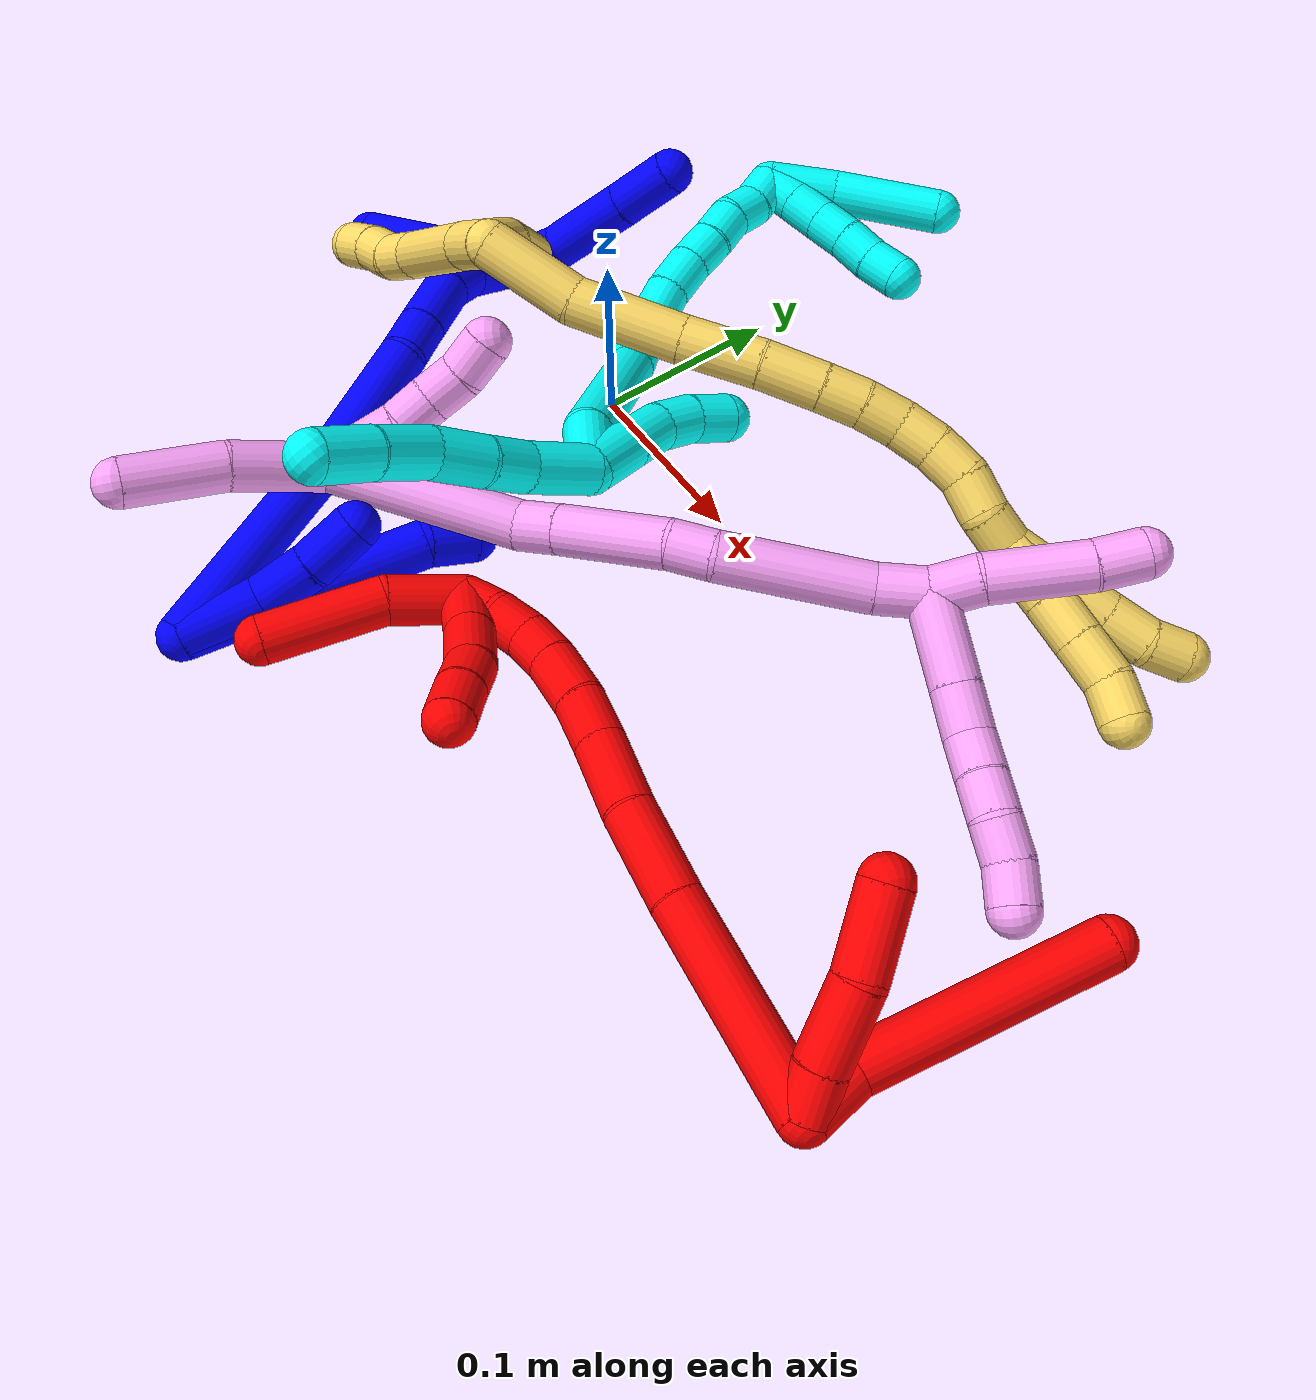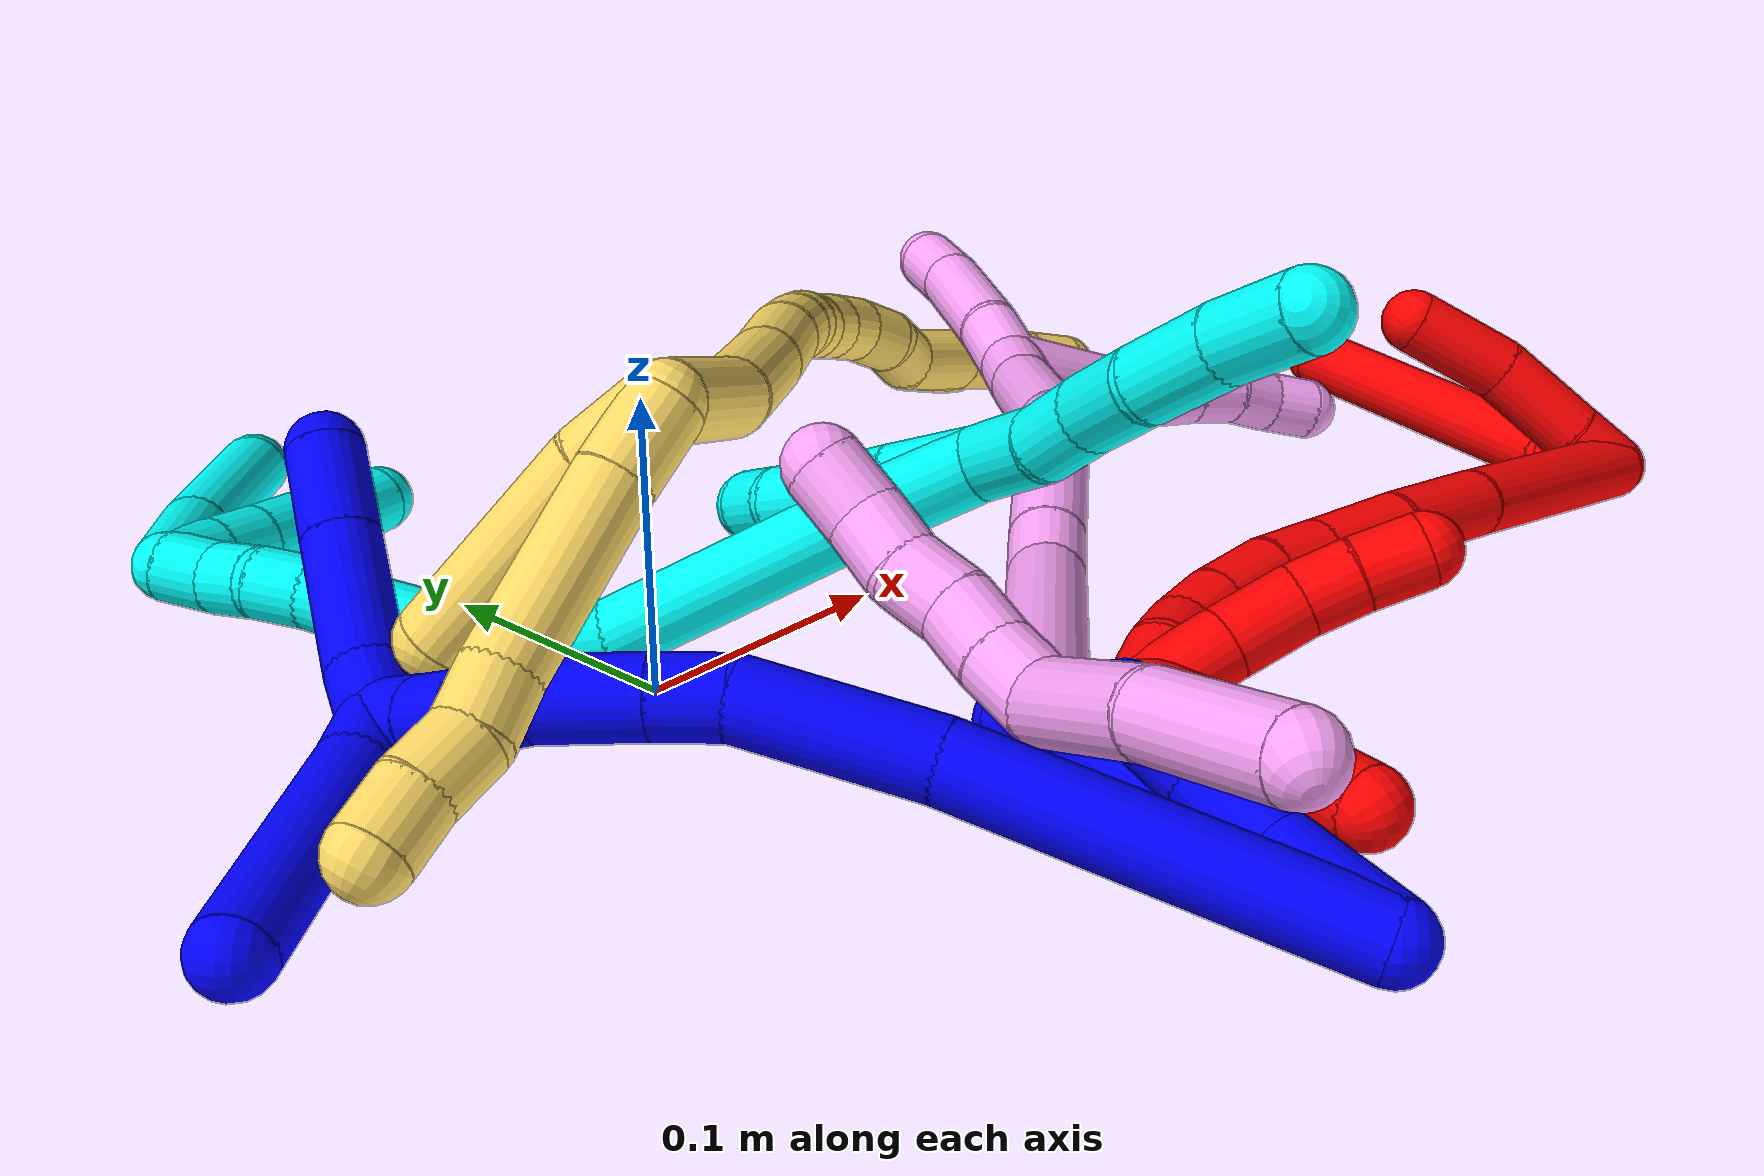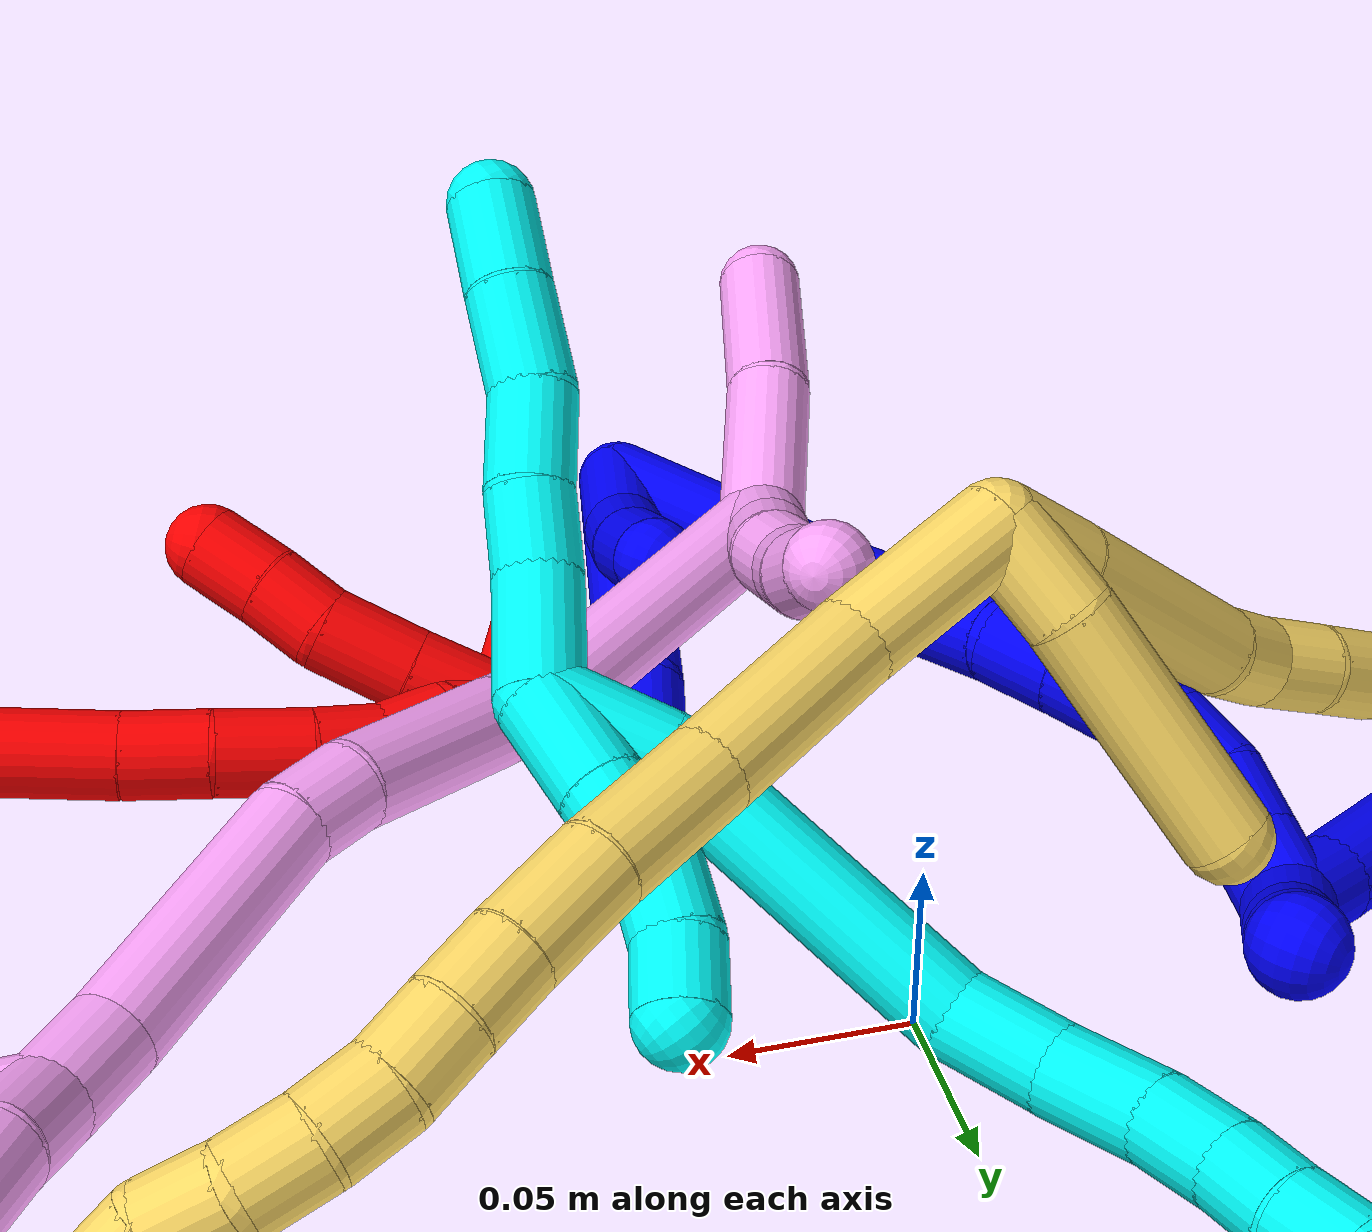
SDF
<sdf version="1.7">
 <world name="default">
  <plugin name="TubeGeneratorPlugin" filename="libtube_generator_plugin.so"/>
  <model name="photoneo_s_sensor">
   <static>1</static>
   <pose>0 0 2 1.57079 1.57079 3.14159</pose>
   <link name="link">
    <inertial><mass>0.1</mass></inertial>
    <sensor name="sensor" type="depth">
     <update_rate>30</update_rate>
     <camera>
      <horizontal_fov>1.22</horizontal_fov>
      <image><width>1920</width><height>1200</height><format>B8G8R8</format></image>
      <clip><near>0.1</near><far>4</far></clip>
      <depth_camera><output>points</output></depth_camera>
     </camera>
     <plugin name="camera_plugin" filename="libgazebo_ros_depth_camera.so">
      <baseline>0.2</baseline>
      <alwaysOn>1</alwaysOn>
      <updateRate>0.0</updateRate>
      <cameraName>camera_ir</cameraName>
      <imageTopicName>/camera/color/image_raw</imageTopicName>
      <cameraInfoTopicName>/camera/color/camera_info</cameraInfoTopicName>
      <depthImageTopicName>/camera/depth/image_raw</depthImageTopicName>
      <depthImageCameraInfoTopicName>/camera/depth/camera_info</depthImageCameraInfoTopicName>
      <pointCloudTopicName>/camera/depth/points</pointCloudTopicName>
      <frameName>fr_optical</frameName>
      <pointCloudCutoff>0.1</pointCloudCutoff>
      <pointCloudCutoffMax>2.0</pointCloudCutoffMax>
      <distortionK1>0</distortionK1>
      <distortionK2>0</distortionK2>
      <distortionK3>0</distortionK3>
      <distortionT1>0</distortionT1>
      <distortionT2>0</distortionT2>
      <CxPrime>0</CxPrime>
      <Cx>0</Cx>
      <Cy>0</Cy>
      <focalLength>0</focalLength>
      <hackBaseline>0</hackBaseline>
     </plugin>
    </sensor>
   </link>
  </model>
  <gravity>0 0 -9.8</gravity>
  <magnetic_field>6e-06 2.3e-05 -4.2e-05</magnetic_field>
  <atmosphere type="adiabatic"/>
  <physics name="default_physics" default="0" type="ode">
   <max_step_size>0.003</max_step_size>
   <real_time_factor>1</real_time_factor>
   <real_time_update_rate>1000</real_time_update_rate>
   <max_contacts>10000</max_contacts>
   <ode>
    <solver>
     <type>quick</type>
     <iters>100</iters>
     <sor>1.3</sor>
     <use_dynamic_moi_rescaling>0</use_dynamic_moi_rescaling>
    </solver>
    <constraints>
     <contact_max_correcting_vel>0</contact_max_correcting_vel>
     <contact_surface_layer>0.001</contact_surface_layer>
     <cfm>0</cfm>
     <erp>0.2</erp>
    </constraints>
   </ode>
  </physics>
  <scene><ambient>0.4 0.4 0.4 1</ambient><background>0.7 0.7 0.7 1</background><shadows>0</shadows></scene>
  <audio><device>default</device></audio>
  <spherical_coordinates>
   <surface_model>EARTH_WGS84</surface_model>
   <latitude_deg>0</latitude_deg>
   <longitude_deg>0</longitude_deg>
   <elevation>0</elevation>
   <heading_deg>0</heading_deg>
  </spherical_coordinates>
  <model name="bin">
   <static>1</static>
   <link name="bottom">
    <collision name="collision-bottom">
     <pose>0 0 -0.01 0 -0 0</pose>
     <geometry><box><size>0.8 0.6 0.02</size></box></geometry>
     <surface>
      <friction><ode><mu>100</mu><mu2>100</mu2></ode></friction>
      <contact><collide_bitmask>65535</collide_bitmask></contact>
     </surface>
    </collision>
   </link>
   <link name="west_wall">
    <collision name="collision-west_wall">
     <pose>-0.41 0 0.1 0 -0 0</pose>
     <geometry><box><size>0.02 0.6 0.2</size></box></geometry>
     <surface>
      <friction><ode><mu>100</mu><mu2>100</mu2></ode></friction>
      <contact><collide_bitmask>65535</collide_bitmask></contact>
     </surface>
    </collision>
   </link>
   <link name="east_wall">
    <collision name="collision-east_wall">
     <pose>0.41 0 0.1 0 -0 0</pose>
     <geometry><box><size>0.02 0.6 0.2</size></box></geometry>
     <surface>
      <friction><ode><mu>100</mu><mu2>100</mu2></ode></friction>
      <contact><collide_bitmask>65535</collide_bitmask></contact>
     </surface>
    </collision>
   </link>
   <link name="south_wall">
    <collision name="collision-south_wall">
     <pose>0 -0.31 0.1 0 -0 0</pose>
     <geometry><box><size>0.8 0.02 0.2</size></box></geometry>
     <surface>
      <friction><ode><mu>100</mu><mu2>100</mu2></ode></friction>
      <contact><collide_bitmask>65535</collide_bitmask></contact>
     </surface>
    </collision>
   </link>
   <link name="north_wall">
    <collision name="collision-north_wall">
     <pose>0 0.31 0.1 0 -0 0</pose>
     <geometry><box><size>0.8 0.02 0.2</size></box></geometry>
     <surface>
      <friction><ode><mu>100</mu><mu2>100</mu2></ode></friction>
      <contact><collide_bitmask>65535</collide_bitmask></contact>
     </surface>
    </collision>
   </link>
  </model>
  <model name="1">
   <static>0</static>
   <link name="1">
    <collision name="collision-cylinder-e_1_2_8">
     <pose>0.007407 0.047215 -0.040642 -2.28153 0.118342 -0.256896</pose>
     <geometry><cylinder><radius>0.0125</radius><length>0.125474</length></cylinder></geometry>
     <surface>
      <friction><ode><mu>1.16</mu><mu2>1.16</mu2><slip1>0</slip1><slip2>0</slip2></ode></friction>
      <contact><ode><kp>1e+06</kp><kd>1</kd><max_vel>0</max_vel><min_depth>0.001</min_depth></ode></contact>
     </surface>
    </collision>
    <visual name="visual-cylinder-e_1_2_8">
     <pose>0.007407 0.047215 -0.040642 -2.28153 0.118342 -0.256896</pose>
     <geometry><cylinder><radius>0.0125</radius><length>0.125474</length></cylinder></geometry>
     <material><ambient>0 0 1 1</ambient></material>
    </visual>
    <collision name="collision-cylinder-e_2_8_6">
     <pose>0.020325 0.102675 -0.088498 -2.28946 0.466049 -0.963625</pose>
     <geometry><cylinder><radius>0.0125</radius><length>0.024526</length></cylinder></geometry>
     <surface>
      <friction><ode><mu>1.16</mu><mu2>1.16</mu2><slip1>0</slip1><slip2>0</slip2></ode></friction>
      <contact><ode><kp>1e+06</kp><kd>1</kd><max_vel>0</max_vel><min_depth>0.001</min_depth></ode></contact>
     </surface>
    </collision>
    <visual name="visual-cylinder-e_2_8_6">
     <pose>0.020325 0.102675 -0.088498 -2.28946 0.466049 -0.963625</pose>
     <geometry><cylinder><radius>0.0125</radius><length>0.024526</length></cylinder></geometry>
     <material><ambient>0 0 1 1</ambient></material>
    </visual>
    <collision name="collision-cylinder-e_1_2_9">
     <pose>0.000329 0.01603 -0.013361 -2.26563 0.015756 -0.033642</pose>
     <geometry><cylinder><radius>0.0125</radius><length>0.041741</length></cylinder></geometry>
     <surface>
      <friction><ode><mu>1.16</mu><mu2>1.16</mu2><slip1>0</slip1><slip2>0</slip2></ode></friction>
      <contact><ode><kp>1e+06</kp><kd>1</kd><max_vel>0</max_vel><min_depth>0.001</min_depth></ode></contact>
     </surface>
    </collision>
    <visual name="visual-cylinder-e_1_2_9">
     <pose>0.000329 0.01603 -0.013361 -2.26563 0.015756 -0.033642</pose>
     <geometry><cylinder><radius>0.0125</radius><length>0.041741</length></cylinder></geometry>
     <material><ambient>0 0 1 1</ambient></material>
    </visual>
    <collision name="collision-cylinder-e_2_9_10">
     <pose>-0.002686 0.042902 -0.035887 -2.27255 -0.231312 0.490557</pose>
     <geometry><cylinder><radius>0.0125</radius><length>0.029171</length></cylinder></geometry>
     <surface>
      <friction><ode><mu>1.16</mu><mu2>1.16</mu2><slip1>0</slip1><slip2>0</slip2></ode></friction>
      <contact><ode><kp>1e+06</kp><kd>1</kd><max_vel>0</max_vel><min_depth>0.001</min_depth></ode></contact>
     </surface>
    </collision>
    <visual name="visual-cylinder-e_2_9_10">
     <pose>-0.002686 0.042902 -0.035887 -2.27255 -0.231312 0.490557</pose>
     <geometry><cylinder><radius>0.0125</radius><length>0.029171</length></cylinder></geometry>
     <material><ambient>0 0 1 1</ambient></material>
    </visual>
    <collision name="collision-cylinder-e_3_10_5">
     <pose>-0.010193 0.063175 -0.055311 -2.39828 -0.290323 0.717655</pose>
     <geometry><cylinder><radius>0.0125</radius><length>0.029088</length></cylinder></geometry>
     <surface>
      <friction><ode><mu>1.16</mu><mu2>1.16</mu2><slip1>0</slip1><slip2>0</slip2></ode></friction>
      <contact><ode><kp>1e+06</kp><kd>1</kd><max_vel>0</max_vel><min_depth>0.001</min_depth></ode></contact>
     </surface>
    </collision>
    <visual name="visual-cylinder-e_3_10_5">
     <pose>-0.010193 0.063175 -0.055311 -2.39828 -0.290323 0.717655</pose>
     <geometry><cylinder><radius>0.0125</radius><length>0.029088</length></cylinder></geometry>
     <material><ambient>0 0 1 1</ambient></material>
    </visual>
    <collision name="collision-cylinder-e_1_2_11">
     <pose>-0.008257 0.021761 -0.057332 -2.77883 -0.133846 0.700749</pose>
     <geometry><cylinder><radius>0.0125</radius><length>0.123753</length></cylinder></geometry>
     <surface>
      <friction><ode><mu>1.16</mu><mu2>1.16</mu2><slip1>0</slip1><slip2>0</slip2></ode></friction>
      <contact><ode><kp>1e+06</kp><kd>1</kd><max_vel>0</max_vel><min_depth>0.001</min_depth></ode></contact>
     </surface>
    </collision>
    <visual name="visual-cylinder-e_1_2_11">
     <pose>-0.008257 0.021761 -0.057332 -2.77883 -0.133846 0.700749</pose>
     <geometry><cylinder><radius>0.0125</radius><length>0.123753</length></cylinder></geometry>
     <material><ambient>0 0 1 1</ambient></material>
    </visual>
    <collision name="collision-cylinder-e_2_11_12">
     <pose>-0.020218 0.050859 -0.143515 -2.89257 -0.12378 0.919485</pose>
     <geometry><cylinder><radius>0.0125</radius><length>0.059997</length></cylinder></geometry>
     <surface>
      <friction><ode><mu>1.16</mu><mu2>1.16</mu2><slip1>0</slip1><slip2>0</slip2></ode></friction>
      <contact><ode><kp>1e+06</kp><kd>1</kd><max_vel>0</max_vel><min_depth>0.001</min_depth></ode></contact>
     </surface>
    </collision>
    <visual name="visual-cylinder-e_2_11_12">
     <pose>-0.020218 0.050859 -0.143515 -2.89257 -0.12378 0.919485</pose>
     <geometry><cylinder><radius>0.0125</radius><length>0.059997</length></cylinder></geometry>
     <material><ambient>0 0 1 1</ambient></material>
    </visual>
    <collision name="collision-cylinder-e_3_12_13">
     <pose>-0.023324 0.058651 -0.183492 -3.10067 0.05361 -1.83773</pose>
     <geometry><cylinder><radius>0.0125</radius><length>0.022303</length></cylinder></geometry>
     <surface>
      <friction><ode><mu>1.16</mu><mu2>1.16</mu2><slip1>0</slip1><slip2>0</slip2></ode></friction>
      <contact><ode><kp>1e+06</kp><kd>1</kd><max_vel>0</max_vel><min_depth>0.001</min_depth></ode></contact>
     </surface>
    </collision>
    <visual name="visual-cylinder-e_3_12_13">
     <pose>-0.023324 0.058651 -0.183492 -3.10067 0.05361 -1.83773</pose>
     <geometry><cylinder><radius>0.0125</radius><length>0.022303</length></cylinder></geometry>
     <material><ambient>0 0 1 1</ambient></material>
    </visual>
    <collision name="collision-cylinder-e_4_13_14">
     <pose>-0.021176 0.059584 -0.211064 -3.11255 0.093993 -2.54254</pose>
     <geometry><cylinder><radius>0.0125</radius><length>0.033053</length></cylinder></geometry>
     <surface>
      <friction><ode><mu>1.16</mu><mu2>1.16</mu2><slip1>0</slip1><slip2>0</slip2></ode></friction>
      <contact><ode><kp>1e+06</kp><kd>1</kd><max_vel>0</max_vel><min_depth>0.001</min_depth></ode></contact>
     </surface>
    </collision>
    <visual name="visual-cylinder-e_4_13_14">
     <pose>-0.021176 0.059584 -0.211064 -3.11255 0.093993 -2.54254</pose>
     <geometry><cylinder><radius>0.0125</radius><length>0.033053</length></cylinder></geometry>
     <material><ambient>0 0 1 1</ambient></material>
    </visual>
    <collision name="collision-cylinder-e_5_14_15">
     <pose>-0.015943 0.061511 -0.236942 -2.98914 0.368265 -2.36326</pose>
     <geometry><cylinder><radius>0.0125</radius><length>0.020455</length></cylinder></geometry>
     <surface>
      <friction><ode><mu>1.16</mu><mu2>1.16</mu2><slip1>0</slip1><slip2>0</slip2></ode></friction>
      <contact><ode><kp>1e+06</kp><kd>1</kd><max_vel>0</max_vel><min_depth>0.001</min_depth></ode></contact>
     </surface>
    </collision>
    <visual name="visual-cylinder-e_5_14_15">
     <pose>-0.015943 0.061511 -0.236942 -2.98914 0.368265 -2.36326</pose>
     <geometry><cylinder><radius>0.0125</radius><length>0.020455</length></cylinder></geometry>
     <material><ambient>0 0 1 1</ambient></material>
    </visual>
    <collision name="collision-cylinder-e_6_15_16">
     <pose>-0.007534 0.066949 -0.254441 -2.68244 0.483654 -1.62474</pose>
     <geometry><cylinder><radius>0.0125</radius><length>0.020332</length></cylinder></geometry>
     <surface>
      <friction><ode><mu>1.16</mu><mu2>1.16</mu2><slip1>0</slip1><slip2>0</slip2></ode></friction>
      <contact><ode><kp>1e+06</kp><kd>1</kd><max_vel>0</max_vel><min_depth>0.001</min_depth></ode></contact>
     </surface>
    </collision>
    <visual name="visual-cylinder-e_6_15_16">
     <pose>-0.007534 0.066949 -0.254441 -2.68244 0.483654 -1.62474</pose>
     <geometry><cylinder><radius>0.0125</radius><length>0.020332</length></cylinder></geometry>
     <material><ambient>0 0 1 1</ambient></material>
    </visual>
    <collision name="collision-cylinder-e_7_16_1">
     <pose>0.001628 0.075106 -0.270511 -2.66134 0.456764 -1.5188</pose>
     <geometry><cylinder><radius>0.0125</radius><length>0.020108</length></cylinder></geometry>
     <surface>
      <friction><ode><mu>1.16</mu><mu2>1.16</mu2><slip1>0</slip1><slip2>0</slip2></ode></friction>
      <contact><ode><kp>1e+06</kp><kd>1</kd><max_vel>0</max_vel><min_depth>0.001</min_depth></ode></contact>
     </surface>
    </collision>
    <visual name="visual-cylinder-e_7_16_1">
     <pose>0.001628 0.075106 -0.270511 -2.66134 0.456764 -1.5188</pose>
     <geometry><cylinder><radius>0.0125</radius><length>0.020108</length></cylinder></geometry>
     <material><ambient>0 0 1 1</ambient></material>
    </visual>
    <collision name="collision-cylinder-e_1_1_17">
     <pose>0.00606 0.068935 -0.279422 1.65841 -0.000216 -0.000236</pose>
     <geometry><cylinder><radius>0.0125</radius><length>0.020759</length></cylinder></geometry>
     <surface>
      <friction><ode><mu>1.16</mu><mu2>1.16</mu2><slip1>0</slip1><slip2>0</slip2></ode></friction>
      <contact><ode><kp>1e+06</kp><kd>1</kd><max_vel>0</max_vel><min_depth>0.001</min_depth></ode></contact>
     </surface>
    </collision>
    <visual name="visual-cylinder-e_1_1_17">
     <pose>0.00606 0.068935 -0.279422 1.65841 -0.000216 -0.000236</pose>
     <geometry><cylinder><radius>0.0125</radius><length>0.020759</length></cylinder></geometry>
     <material><ambient>0 0 1 1</ambient></material>
    </visual>
    <collision name="collision-cylinder-e_2_17_4">
     <pose>0.001991 0.019412 -0.284559 1.67831 -0.102829 -0.1145</pose>
     <geometry><cylinder><radius>0.0125</radius><length>0.079241</length></cylinder></geometry>
     <surface>
      <friction><ode><mu>1.16</mu><mu2>1.16</mu2><slip1>0</slip1><slip2>0</slip2></ode></friction>
      <contact><ode><kp>1e+06</kp><kd>1</kd><max_vel>0</max_vel><min_depth>0.001</min_depth></ode></contact>
     </surface>
    </collision>
    <visual name="visual-cylinder-e_2_17_4">
     <pose>0.001991 0.019412 -0.284559 1.67831 -0.102829 -0.1145</pose>
     <geometry><cylinder><radius>0.0125</radius><length>0.079241</length></cylinder></geometry>
     <material><ambient>0 0 1 1</ambient></material>
    </visual>
    <collision name="collision-cylinder-e_1_1_18">
     <pose>0.004465 0.088514 -0.282993 -2.02226 -0.154294 0.245535</pose>
     <geometry><cylinder><radius>0.0125</radius><length>0.020783</length></cylinder></geometry>
     <surface>
      <friction><ode><mu>1.16</mu><mu2>1.16</mu2><slip1>0</slip1><slip2>0</slip2></ode></friction>
      <contact><ode><kp>1e+06</kp><kd>1</kd><max_vel>0</max_vel><min_depth>0.001</min_depth></ode></contact>
     </surface>
    </collision>
    <visual name="visual-cylinder-e_1_1_18">
     <pose>0.004465 0.088514 -0.282993 -2.02226 -0.154294 0.245535</pose>
     <geometry><cylinder><radius>0.0125</radius><length>0.020783</length></cylinder></geometry>
     <material><ambient>0 0 1 1</ambient></material>
    </visual>
    <collision name="collision-cylinder-e_2_18_19">
     <pose>-0.006823 0.117574 -0.295106 -1.93836 -0.428075 0.61328</pose>
     <geometry><cylinder><radius>0.0125</radius><length>0.046692</length></cylinder></geometry>
     <surface>
      <friction><ode><mu>1.16</mu><mu2>1.16</mu2><slip1>0</slip1><slip2>0</slip2></ode></friction>
      <contact><ode><kp>1e+06</kp><kd>1</kd><max_vel>0</max_vel><min_depth>0.001</min_depth></ode></contact>
     </surface>
    </collision>
    <visual name="visual-cylinder-e_2_18_19">
     <pose>-0.006823 0.117574 -0.295106 -1.93836 -0.428075 0.61328</pose>
     <geometry><cylinder><radius>0.0125</radius><length>0.046692</length></cylinder></geometry>
     <material><ambient>0 0 1 1</ambient></material>
    </visual>
    <collision name="collision-cylinder-e_3_19_3">
     <pose>-0.023554 0.151112 -0.307911 -1.9314 -0.447646 0.635916</pose>
     <geometry><cylinder><radius>0.0125</radius><length>0.032525</length></cylinder></geometry>
     <surface>
      <friction><ode><mu>1.16</mu><mu2>1.16</mu2><slip1>0</slip1><slip2>0</slip2></ode></friction>
      <contact><ode><kp>1e+06</kp><kd>1</kd><max_vel>0</max_vel><min_depth>0.001</min_depth></ode></contact>
     </surface>
    </collision>
    <visual name="visual-cylinder-e_3_19_3">
     <pose>-0.023554 0.151112 -0.307911 -1.9314 -0.447646 0.635916</pose>
     <geometry><cylinder><radius>0.0125</radius><length>0.032525</length></cylinder></geometry>
     <material><ambient>0 0 1 1</ambient></material>
    </visual>
    <collision name="collision-sphere-3">
     <pose>-0.030593 0.164829 -0.313083 0 -0 0</pose>
     <geometry><sphere><radius>0.0125</radius></sphere></geometry>
     <surface>
      <friction><ode><mu>1.16</mu><mu2>1.16</mu2><slip1>0</slip1><slip2>0</slip2></ode></friction>
      <contact><ode><kp>1e+06</kp><kd>1</kd><max_vel>0</max_vel><min_depth>0.001</min_depth></ode></contact>
     </surface>
    </collision>
    <visual name="visual-sphere-3">
     <pose>-0.030593 0.164829 -0.313083 0 -0 0</pose>
     <geometry><sphere><radius>0.0125</radius></sphere></geometry>
     <material><ambient>0 0 1 1</ambient></material>
    </visual>
    <collision name="collision-sphere-19">
     <pose>-0.016515 0.137395 -0.302738 0 -0 0</pose>
     <geometry><sphere><radius>0.0125</radius></sphere></geometry>
     <surface>
      <friction><ode><mu>1.16</mu><mu2>1.16</mu2><slip1>0</slip1><slip2>0</slip2></ode></friction>
      <contact><ode><kp>1e+06</kp><kd>1</kd><max_vel>0</max_vel><min_depth>0.001</min_depth></ode></contact>
     </surface>
    </collision>
    <visual name="visual-sphere-19">
     <pose>-0.016515 0.137395 -0.302738 0 -0 0</pose>
     <geometry><sphere><radius>0.0125</radius></sphere></geometry>
     <material><ambient>0 0 1 1</ambient></material>
    </visual>
    <collision name="collision-sphere-5">
     <pose>-0.014357 0.072606 -0.065571 0 -0 0</pose>
     <geometry><sphere><radius>0.0125</radius></sphere></geometry>
     <surface>
      <friction><ode><mu>1.16</mu><mu2>1.16</mu2><slip1>0</slip1><slip2>0</slip2></ode></friction>
      <contact><ode><kp>1e+06</kp><kd>1</kd><max_vel>0</max_vel><min_depth>0.001</min_depth></ode></contact>
     </surface>
    </collision>
    <visual name="visual-sphere-5">
     <pose>-0.014357 0.072606 -0.065571 0 -0 0</pose>
     <geometry><sphere><radius>0.0125</radius></sphere></geometry>
     <material><ambient>0 0 1 1</ambient></material>
    </visual>
    <collision name="collision-sphere-10">
     <pose>-0.00603 0.053745 -0.045052 0 -0 0</pose>
     <geometry><sphere><radius>0.0125</radius></sphere></geometry>
     <surface>
      <friction><ode><mu>1.16</mu><mu2>1.16</mu2><slip1>0</slip1><slip2>0</slip2></ode></friction>
      <contact><ode><kp>1e+06</kp><kd>1</kd><max_vel>0</max_vel><min_depth>0.001</min_depth></ode></contact>
     </surface>
    </collision>
    <visual name="visual-sphere-10">
     <pose>-0.00603 0.053745 -0.045052 0 -0 0</pose>
     <geometry><sphere><radius>0.0125</radius></sphere></geometry>
     <material><ambient>0 0 1 1</ambient></material>
    </visual>
    <collision name="collision-sphere-6">
     <pose>0.025835 0.110921 -0.09571 0 -0 0</pose>
     <geometry><sphere><radius>0.0125</radius></sphere></geometry>
     <surface>
      <friction><ode><mu>1.16</mu><mu2>1.16</mu2><slip1>0</slip1><slip2>0</slip2></ode></friction>
      <contact><ode><kp>1e+06</kp><kd>1</kd><max_vel>0</max_vel><min_depth>0.001</min_depth></ode></contact>
     </surface>
    </collision>
    <visual name="visual-sphere-6">
     <pose>0.025835 0.110921 -0.09571 0 -0 0</pose>
     <geometry><sphere><radius>0.0125</radius></sphere></geometry>
     <material><ambient>0 0 1 1</ambient></material>
    </visual>
    <collision name="collision-sphere-9">
     <pose>0.000658 0.03206 -0.026722 0 -0 0</pose>
     <geometry><sphere><radius>0.0125</radius></sphere></geometry>
     <surface>
      <friction><ode><mu>1.16</mu><mu2>1.16</mu2><slip1>0</slip1><slip2>0</slip2></ode></friction>
      <contact><ode><kp>1e+06</kp><kd>1</kd><max_vel>0</max_vel><min_depth>0.001</min_depth></ode></contact>
     </surface>
    </collision>
    <visual name="visual-sphere-9">
     <pose>0.000658 0.03206 -0.026722 0 -0 0</pose>
     <geometry><sphere><radius>0.0125</radius></sphere></geometry>
     <material><ambient>0 0 1 1</ambient></material>
    </visual>
    <collision name="collision-sphere-2">
     <geometry><sphere><radius>0.0125</radius></sphere></geometry>
     <surface>
      <friction><ode><mu>1.16</mu><mu2>1.16</mu2><slip1>0</slip1><slip2>0</slip2></ode></friction>
      <contact><ode><kp>1e+06</kp><kd>1</kd><max_vel>0</max_vel><min_depth>0.001</min_depth></ode></contact>
     </surface>
    </collision>
    <visual name="visual-sphere-2">
     <geometry><sphere><radius>0.0125</radius></sphere></geometry>
     <material><ambient>0 0 1 1</ambient></material>
    </visual>
    <collision name="collision-sphere-8">
     <pose>0.014814 0.09443 -0.081285 0 -0 0</pose>
     <geometry><sphere><radius>0.0125</radius></sphere></geometry>
     <surface>
      <friction><ode><mu>1.16</mu><mu2>1.16</mu2><slip1>0</slip1><slip2>0</slip2></ode></friction>
      <contact><ode><kp>1e+06</kp><kd>1</kd><max_vel>0</max_vel><min_depth>0.001</min_depth></ode></contact>
     </surface>
    </collision>
    <visual name="visual-sphere-8">
     <pose>0.014814 0.09443 -0.081285 0 -0 0</pose>
     <geometry><sphere><radius>0.0125</radius></sphere></geometry>
     <material><ambient>0 0 1 1</ambient></material>
    </visual>
    <collision name="collision-sphere-11">
     <pose>-0.016514 0.043522 -0.114664 0 -0 0</pose>
     <geometry><sphere><radius>0.0125</radius></sphere></geometry>
     <surface>
      <friction><ode><mu>1.16</mu><mu2>1.16</mu2><slip1>0</slip1><slip2>0</slip2></ode></friction>
      <contact><ode><kp>1e+06</kp><kd>1</kd><max_vel>0</max_vel><min_depth>0.001</min_depth></ode></contact>
     </surface>
    </collision>
    <visual name="visual-sphere-11">
     <pose>-0.016514 0.043522 -0.114664 0 -0 0</pose>
     <geometry><sphere><radius>0.0125</radius></sphere></geometry>
     <material><ambient>0 0 1 1</ambient></material>
    </visual>
    <collision name="collision-sphere-12">
     <pose>-0.023922 0.058195 -0.172366 0 -0 0</pose>
     <geometry><sphere><radius>0.0125</radius></sphere></geometry>
     <surface>
      <friction><ode><mu>1.16</mu><mu2>1.16</mu2><slip1>0</slip1><slip2>0</slip2></ode></friction>
      <contact><ode><kp>1e+06</kp><kd>1</kd><max_vel>0</max_vel><min_depth>0.001</min_depth></ode></contact>
     </surface>
    </collision>
    <visual name="visual-sphere-12">
     <pose>-0.023922 0.058195 -0.172366 0 -0 0</pose>
     <geometry><sphere><radius>0.0125</radius></sphere></geometry>
     <material><ambient>0 0 1 1</ambient></material>
    </visual>
    <collision name="collision-sphere-13">
     <pose>-0.022727 0.059107 -0.194618 0 -0 0</pose>
     <geometry><sphere><radius>0.0125</radius></sphere></geometry>
     <surface>
      <friction><ode><mu>1.16</mu><mu2>1.16</mu2><slip1>0</slip1><slip2>0</slip2></ode></friction>
      <contact><ode><kp>1e+06</kp><kd>1</kd><max_vel>0</max_vel><min_depth>0.001</min_depth></ode></contact>
     </surface>
    </collision>
    <visual name="visual-sphere-13">
     <pose>-0.022727 0.059107 -0.194618 0 -0 0</pose>
     <geometry><sphere><radius>0.0125</radius></sphere></geometry>
     <material><ambient>0 0 1 1</ambient></material>
    </visual>
    <collision name="collision-sphere-14">
     <pose>-0.019625 0.060062 -0.227511 0 -0 0</pose>
     <geometry><sphere><radius>0.0125</radius></sphere></geometry>
     <surface>
      <friction><ode><mu>1.16</mu><mu2>1.16</mu2><slip1>0</slip1><slip2>0</slip2></ode></friction>
      <contact><ode><kp>1e+06</kp><kd>1</kd><max_vel>0</max_vel><min_depth>0.001</min_depth></ode></contact>
     </surface>
    </collision>
    <visual name="visual-sphere-14">
     <pose>-0.019625 0.060062 -0.227511 0 -0 0</pose>
     <geometry><sphere><radius>0.0125</radius></sphere></geometry>
     <material><ambient>0 0 1 1</ambient></material>
    </visual>
    <collision name="collision-sphere-15">
     <pose>-0.012261 0.06296 -0.246373 0 -0 0</pose>
     <geometry><sphere><radius>0.0125</radius></sphere></geometry>
     <surface>
      <friction><ode><mu>1.16</mu><mu2>1.16</mu2><slip1>0</slip1><slip2>0</slip2></ode></friction>
      <contact><ode><kp>1e+06</kp><kd>1</kd><max_vel>0</max_vel><min_depth>0.001</min_depth></ode></contact>
     </surface>
    </collision>
    <visual name="visual-sphere-15">
     <pose>-0.012261 0.06296 -0.246373 0 -0 0</pose>
     <geometry><sphere><radius>0.0125</radius></sphere></geometry>
     <material><ambient>0 0 1 1</ambient></material>
    </visual>
    <collision name="collision-sphere-16">
     <pose>-0.002806 0.070938 -0.262509 0 -0 0</pose>
     <geometry><sphere><radius>0.0125</radius></sphere></geometry>
     <surface>
      <friction><ode><mu>1.16</mu><mu2>1.16</mu2><slip1>0</slip1><slip2>0</slip2></ode></friction>
      <contact><ode><kp>1e+06</kp><kd>1</kd><max_vel>0</max_vel><min_depth>0.001</min_depth></ode></contact>
     </surface>
    </collision>
    <visual name="visual-sphere-16">
     <pose>-0.002806 0.070938 -0.262509 0 -0 0</pose>
     <geometry><sphere><radius>0.0125</radius></sphere></geometry>
     <material><ambient>0 0 1 1</ambient></material>
    </visual>
    <collision name="collision-sphere-1">
     <pose>0.006062 0.079275 -0.278514 0 -0 0</pose>
     <geometry><sphere><radius>0.0125</radius></sphere></geometry>
     <surface>
      <friction><ode><mu>1.16</mu><mu2>1.16</mu2><slip1>0</slip1><slip2>0</slip2></ode></friction>
      <contact><ode><kp>1e+06</kp><kd>1</kd><max_vel>0</max_vel><min_depth>0.001</min_depth></ode></contact>
     </surface>
    </collision>
    <visual name="visual-sphere-1">
     <pose>0.006062 0.079275 -0.278514 0 -0 0</pose>
     <geometry><sphere><radius>0.0125</radius></sphere></geometry>
     <material><ambient>0 0 1 1</ambient></material>
    </visual>
    <collision name="collision-sphere-18">
     <pose>0.002868 0.097754 -0.287473 0 -0 0</pose>
     <geometry><sphere><radius>0.0125</radius></sphere></geometry>
     <surface>
      <friction><ode><mu>1.16</mu><mu2>1.16</mu2><slip1>0</slip1><slip2>0</slip2></ode></friction>
      <contact><ode><kp>1e+06</kp><kd>1</kd><max_vel>0</max_vel><min_depth>0.001</min_depth></ode></contact>
     </surface>
    </collision>
    <visual name="visual-sphere-18">
     <pose>0.002868 0.097754 -0.287473 0 -0 0</pose>
     <geometry><sphere><radius>0.0125</radius></sphere></geometry>
     <material><ambient>0 0 1 1</ambient></material>
    </visual>
    <collision name="collision-sphere-17">
     <pose>0.006058 0.058596 -0.28033 0 -0 0</pose>
     <geometry><sphere><radius>0.0125</radius></sphere></geometry>
     <surface>
      <friction><ode><mu>1.16</mu><mu2>1.16</mu2><slip1>0</slip1><slip2>0</slip2></ode></friction>
      <contact><ode><kp>1e+06</kp><kd>1</kd><max_vel>0</max_vel><min_depth>0.001</min_depth></ode></contact>
     </surface>
    </collision>
    <visual name="visual-sphere-17">
     <pose>0.006058 0.058596 -0.28033 0 -0 0</pose>
     <geometry><sphere><radius>0.0125</radius></sphere></geometry>
     <material><ambient>0 0 1 1</ambient></material>
    </visual>
    <collision name="collision-sphere-4">
     <pose>-0.002076 -0.019772 -0.288788 0 -0 0</pose>
     <geometry><sphere><radius>0.0125</radius></sphere></geometry>
     <surface>
      <friction><ode><mu>1.16</mu><mu2>1.16</mu2><slip1>0</slip1><slip2>0</slip2></ode></friction>
      <contact><ode><kp>1e+06</kp><kd>1</kd><max_vel>0</max_vel><min_depth>0.001</min_depth></ode></contact>
     </surface>
    </collision>
    <visual name="visual-sphere-4">
     <pose>-0.002076 -0.019772 -0.288788 0 -0 0</pose>
     <geometry><sphere><radius>0.0125</radius></sphere></geometry>
     <material><ambient>0 0 1 1</ambient></material>
    </visual>
    <inertial>
     <pose>-0.004724 0.054088 -0.147655 0 -0 0</pose>
     <mass>0.75</mass>
     <inertia>
      <ixx>0.000437</ixx>
      <ixy>0</ixy>
      <ixz>0</ixz>
      <iyy>-0.000141</iyy>
      <iyz>0</iyz>
      <izz>-0.000196</izz>
     </inertia>
    </inertial>
   </link>
   <pose>0.014006 -0.259612 0.011497 1.60734 1.34864 0.710117</pose>
  </model>
  <model name="2">
   <static>0</static>
   <link name="2">
    <collision name="collision-cylinder-e_1_2_8">
     <pose>0.010844 0.007164 -0.005595 -2.23384 0.873151 -1.52629</pose>
     <geometry><cylinder><radius>0.0125</radius><length>0.028299</length></cylinder></geometry>
     <surface>
      <friction><ode><mu>1.16</mu><mu2>1.16</mu2><slip1>0</slip1><slip2>0</slip2></ode></friction>
      <contact><ode><kp>1e+06</kp><kd>1</kd><max_vel>0</max_vel><min_depth>0.001</min_depth></ode></contact>
     </surface>
    </collision>
    <visual name="visual-cylinder-e_1_2_8">
     <pose>0.010844 0.007164 -0.005595 -2.23384 0.873151 -1.52629</pose>
     <geometry><cylinder><radius>0.0125</radius><length>0.028299</length></cylinder></geometry>
     <material><ambient>1 0 0 1</ambient></material>
    </visual>
    <collision name="collision-cylinder-e_2_8_6">
     <pose>0.072441 0.047534 -0.016103 -1.71769 0.986461 -1.11422</pose>
     <geometry><cylinder><radius>0.0125</radius><length>0.121701</length></cylinder></geometry>
     <surface>
      <friction><ode><mu>1.16</mu><mu2>1.16</mu2><slip1>0</slip1><slip2>0</slip2></ode></friction>
      <contact><ode><kp>1e+06</kp><kd>1</kd><max_vel>0</max_vel><min_depth>0.001</min_depth></ode></contact>
     </surface>
    </collision>
    <visual name="visual-cylinder-e_2_8_6">
     <pose>0.072441 0.047534 -0.016103 -1.71769 0.986461 -1.11422</pose>
     <geometry><cylinder><radius>0.0125</radius><length>0.121701</length></cylinder></geometry>
     <material><ambient>1 0 0 1</ambient></material>
    </visual>
    <collision name="collision-cylinder-e_1_2_9">
     <pose>0.001395 0.009823 -0.004517 -2.00178 0.128354 -0.199898</pose>
     <geometry><cylinder><radius>0.0125</radius><length>0.021802</length></cylinder></geometry>
     <surface>
      <friction><ode><mu>1.16</mu><mu2>1.16</mu2><slip1>0</slip1><slip2>0</slip2></ode></friction>
      <contact><ode><kp>1e+06</kp><kd>1</kd><max_vel>0</max_vel><min_depth>0.001</min_depth></ode></contact>
     </surface>
    </collision>
    <visual name="visual-cylinder-e_1_2_9">
     <pose>0.001395 0.009823 -0.004517 -2.00178 0.128354 -0.199898</pose>
     <geometry><cylinder><radius>0.0125</radius><length>0.021802</length></cylinder></geometry>
     <material><ambient>1 0 0 1</ambient></material>
    </visual>
    <collision name="collision-cylinder-e_2_9_10">
     <pose>0.006544 0.03717 -0.015825 -1.94051 0.197083 -0.286695</pose>
     <geometry><cylinder><radius>0.0125</radius><length>0.038331</length></cylinder></geometry>
     <surface>
      <friction><ode><mu>1.16</mu><mu2>1.16</mu2><slip1>0</slip1><slip2>0</slip2></ode></friction>
      <contact><ode><kp>1e+06</kp><kd>1</kd><max_vel>0</max_vel><min_depth>0.001</min_depth></ode></contact>
     </surface>
    </collision>
    <visual name="visual-cylinder-e_2_9_10">
     <pose>0.006544 0.03717 -0.015825 -1.94051 0.197083 -0.286695</pose>
     <geometry><cylinder><radius>0.0125</radius><length>0.038331</length></cylinder></geometry>
     <material><ambient>1 0 0 1</ambient></material>
    </visual>
    <collision name="collision-cylinder-e_3_10_5">
     <pose>0.014105 0.070776 -0.033761 -2.17686 0.192275 -0.364257</pose>
     <geometry><cylinder><radius>0.0125</radius><length>0.039867</length></cylinder></geometry>
     <surface>
      <friction><ode><mu>1.16</mu><mu2>1.16</mu2><slip1>0</slip1><slip2>0</slip2></ode></friction>
      <contact><ode><kp>1e+06</kp><kd>1</kd><max_vel>0</max_vel><min_depth>0.001</min_depth></ode></contact>
     </surface>
    </collision>
    <visual name="visual-cylinder-e_3_10_5">
     <pose>0.014105 0.070776 -0.033761 -2.17686 0.192275 -0.364257</pose>
     <geometry><cylinder><radius>0.0125</radius><length>0.039867</length></cylinder></geometry>
     <material><ambient>1 0 0 1</ambient></material>
    </visual>
    <collision name="collision-cylinder-e_1_2_11">
     <pose>-0.017097 0.011759 -0.04704 -2.89663 -0.338998 1.89452</pose>
     <geometry><cylinder><radius>0.0125</radius><length>0.102827</length></cylinder></geometry>
     <surface>
      <friction><ode><mu>1.16</mu><mu2>1.16</mu2><slip1>0</slip1><slip2>0</slip2></ode></friction>
      <contact><ode><kp>1e+06</kp><kd>1</kd><max_vel>0</max_vel><min_depth>0.001</min_depth></ode></contact>
     </surface>
    </collision>
    <visual name="visual-cylinder-e_1_2_11">
     <pose>-0.017097 0.011759 -0.04704 -2.89663 -0.338998 1.89452</pose>
     <geometry><cylinder><radius>0.0125</radius><length>0.102827</length></cylinder></geometry>
     <material><ambient>1 0 0 1</ambient></material>
    </visual>
    <collision name="collision-cylinder-e_2_11_12">
     <pose>-0.04031 0.028384 -0.115709 -2.9203 -0.269154 1.76727</pose>
     <geometry><cylinder><radius>0.0125</radius><length>0.045995</length></cylinder></geometry>
     <surface>
      <friction><ode><mu>1.16</mu><mu2>1.16</mu2><slip1>0</slip1><slip2>0</slip2></ode></friction>
      <contact><ode><kp>1e+06</kp><kd>1</kd><max_vel>0</max_vel><min_depth>0.001</min_depth></ode></contact>
     </surface>
    </collision>
    <visual name="visual-cylinder-e_2_11_12">
     <pose>-0.04031 0.028384 -0.115709 -2.9203 -0.269154 1.76727</pose>
     <geometry><cylinder><radius>0.0125</radius><length>0.045995</length></cylinder></geometry>
     <material><ambient>1 0 0 1</ambient></material>
    </visual>
    <collision name="collision-cylinder-e_3_12_13">
     <pose>-0.048948 0.036368 -0.155601 -2.97249 -0.135365 1.34922</pose>
     <geometry><cylinder><radius>0.0125</radius><length>0.037397</length></cylinder></geometry>
     <surface>
      <friction><ode><mu>1.16</mu><mu2>1.16</mu2><slip1>0</slip1><slip2>0</slip2></ode></friction>
      <contact><ode><kp>1e+06</kp><kd>1</kd><max_vel>0</max_vel><min_depth>0.001</min_depth></ode></contact>
     </surface>
    </collision>
    <visual name="visual-cylinder-e_3_12_13">
     <pose>-0.048948 0.036368 -0.155601 -2.97249 -0.135365 1.34922</pose>
     <geometry><cylinder><radius>0.0125</radius><length>0.037397</length></cylinder></geometry>
     <material><ambient>1 0 0 1</ambient></material>
    </visual>
    <collision name="collision-cylinder-e_4_13_14">
     <pose>-0.05378 0.041705 -0.185944 -2.95994 -0.185767 1.59333</pose>
     <geometry><cylinder><radius>0.0125</radius><length>0.024995</length></cylinder></geometry>
     <surface>
      <friction><ode><mu>1.16</mu><mu2>1.16</mu2><slip1>0</slip1><slip2>0</slip2></ode></friction>
      <contact><ode><kp>1e+06</kp><kd>1</kd><max_vel>0</max_vel><min_depth>0.001</min_depth></ode></contact>
     </surface>
    </collision>
    <visual name="visual-cylinder-e_4_13_14">
     <pose>-0.05378 0.041705 -0.185944 -2.95994 -0.185767 1.59333</pose>
     <geometry><cylinder><radius>0.0125</radius><length>0.024995</length></cylinder></geometry>
     <material><ambient>1 0 0 1</ambient></material>
    </visual>
    <collision name="collision-cylinder-e_5_14_15">
     <pose>-0.059386 0.044458 -0.211326 -3.10151 -0.242813 2.81591</pose>
     <geometry><cylinder><radius>0.0125</radius><length>0.02743</length></cylinder></geometry>
     <surface>
      <friction><ode><mu>1.16</mu><mu2>1.16</mu2><slip1>0</slip1><slip2>0</slip2></ode></friction>
      <contact><ode><kp>1e+06</kp><kd>1</kd><max_vel>0</max_vel><min_depth>0.001</min_depth></ode></contact>
     </surface>
    </collision>
    <visual name="visual-cylinder-e_5_14_15">
     <pose>-0.059386 0.044458 -0.211326 -3.10151 -0.242813 2.81591</pose>
     <geometry><cylinder><radius>0.0125</radius><length>0.02743</length></cylinder></geometry>
     <material><ambient>1 0 0 1</ambient></material>
    </visual>
    <collision name="collision-cylinder-e_6_15_16">
     <pose>-0.066067 0.044415 -0.234195 3.08143 -0.339414 -2.79396</pose>
     <geometry><cylinder><radius>0.0125</radius><length>0.020327</length></cylinder></geometry>
     <surface>
      <friction><ode><mu>1.16</mu><mu2>1.16</mu2><slip1>0</slip1><slip2>0</slip2></ode></friction>
      <contact><ode><kp>1e+06</kp><kd>1</kd><max_vel>0</max_vel><min_depth>0.001</min_depth></ode></contact>
     </surface>
    </collision>
    <visual name="visual-cylinder-e_6_15_16">
     <pose>-0.066067 0.044415 -0.234195 3.08143 -0.339414 -2.79396</pose>
     <geometry><cylinder><radius>0.0125</radius><length>0.020327</length></cylinder></geometry>
     <material><ambient>1 0 0 1</ambient></material>
    </visual>
    <collision name="collision-cylinder-e_7_16_17">
     <pose>-0.075394 0.043398 -0.251798 3.08677 -0.635954 -2.97537</pose>
     <geometry><cylinder><radius>0.0125</radius><length>0.020011</length></cylinder></geometry>
     <surface>
      <friction><ode><mu>1.16</mu><mu2>1.16</mu2><slip1>0</slip1><slip2>0</slip2></ode></friction>
      <contact><ode><kp>1e+06</kp><kd>1</kd><max_vel>0</max_vel><min_depth>0.001</min_depth></ode></contact>
     </surface>
    </collision>
    <visual name="visual-cylinder-e_7_16_17">
     <pose>-0.075394 0.043398 -0.251798 3.08677 -0.635954 -2.97537</pose>
     <geometry><cylinder><radius>0.0125</radius><length>0.020011</length></cylinder></geometry>
     <material><ambient>1 0 0 1</ambient></material>
    </visual>
    <collision name="collision-cylinder-e_8_17_1">
     <pose>-0.086538 0.040264 -0.268562 2.84226 -0.517748 -2.1063</pose>
     <geometry><cylinder><radius>0.0125</radius><length>0.021019</length></cylinder></geometry>
     <surface>
      <friction><ode><mu>1.16</mu><mu2>1.16</mu2><slip1>0</slip1><slip2>0</slip2></ode></friction>
      <contact><ode><kp>1e+06</kp><kd>1</kd><max_vel>0</max_vel><min_depth>0.001</min_depth></ode></contact>
     </surface>
    </collision>
    <visual name="visual-cylinder-e_8_17_1">
     <pose>-0.086538 0.040264 -0.268562 2.84226 -0.517748 -2.1063</pose>
     <geometry><cylinder><radius>0.0125</radius><length>0.021019</length></cylinder></geometry>
     <material><ambient>1 0 0 1</ambient></material>
    </visual>
    <collision name="collision-cylinder-e_1_1_18">
     <pose>-0.110528 0.033423 -0.279044 1.97138 -1.33549 -1.74416</pose>
     <geometry><cylinder><radius>0.0125</radius><length>0.038643</length></cylinder></geometry>
     <surface>
      <friction><ode><mu>1.16</mu><mu2>1.16</mu2><slip1>0</slip1><slip2>0</slip2></ode></friction>
      <contact><ode><kp>1e+06</kp><kd>1</kd><max_vel>0</max_vel><min_depth>0.001</min_depth></ode></contact>
     </surface>
    </collision>
    <visual name="visual-cylinder-e_1_1_18">
     <pose>-0.110528 0.033423 -0.279044 1.97138 -1.33549 -1.74416</pose>
     <geometry><cylinder><radius>0.0125</radius><length>0.038643</length></cylinder></geometry>
     <material><ambient>1 0 0 1</ambient></material>
    </visual>
    <collision name="collision-cylinder-e_2_18_4">
     <pose>-0.156429 0.01507 -0.278717 1.42512 -1.08379 -0.959245</pose>
     <geometry><cylinder><radius>0.0125</radius><length>0.061357</length></cylinder></geometry>
     <surface>
      <friction><ode><mu>1.16</mu><mu2>1.16</mu2><slip1>0</slip1><slip2>0</slip2></ode></friction>
      <contact><ode><kp>1e+06</kp><kd>1</kd><max_vel>0</max_vel><min_depth>0.001</min_depth></ode></contact>
     </surface>
    </collision>
    <visual name="visual-cylinder-e_2_18_4">
     <pose>-0.156429 0.01507 -0.278717 1.42512 -1.08379 -0.959245</pose>
     <geometry><cylinder><radius>0.0125</radius><length>0.061357</length></cylinder></geometry>
     <material><ambient>1 0 0 1</ambient></material>
    </visual>
    <collision name="collision-cylinder-e_1_1_19">
     <pose>-0.094496 0.038463 -0.26224 -0.059194 -0.180909 0.005371</pose>
     <geometry><cylinder><radius>0.0125</radius><length>0.030647</length></cylinder></geometry>
     <surface>
      <friction><ode><mu>1.16</mu><mu2>1.16</mu2><slip1>0</slip1><slip2>0</slip2></ode></friction>
      <contact><ode><kp>1e+06</kp><kd>1</kd><max_vel>0</max_vel><min_depth>0.001</min_depth></ode></contact>
     </surface>
    </collision>
    <visual name="visual-cylinder-e_1_1_19">
     <pose>-0.094496 0.038463 -0.26224 -0.059194 -0.180909 0.005371</pose>
     <geometry><cylinder><radius>0.0125</radius><length>0.030647</length></cylinder></geometry>
     <material><ambient>1 0 0 1</ambient></material>
    </visual>
    <collision name="collision-cylinder-e_2_19_20">
     <pose>-0.100372 0.03998 -0.233718 -0.046437 -0.22722 0.005299</pose>
     <geometry><cylinder><radius>0.0125</radius><length>0.027691</length></cylinder></geometry>
     <surface>
      <friction><ode><mu>1.16</mu><mu2>1.16</mu2><slip1>0</slip1><slip2>0</slip2></ode></friction>
      <contact><ode><kp>1e+06</kp><kd>1</kd><max_vel>0</max_vel><min_depth>0.001</min_depth></ode></contact>
     </surface>
    </collision>
    <visual name="visual-cylinder-e_2_19_20">
     <pose>-0.100372 0.03998 -0.233718 -0.046437 -0.22722 0.005299</pose>
     <geometry><cylinder><radius>0.0125</radius><length>0.027691</length></cylinder></geometry>
     <material><ambient>1 0 0 1</ambient></material>
    </visual>
    <collision name="collision-cylinder-e_3_20_21">
     <pose>-0.108122 0.040491 -0.211377 0.013015 -0.48131 -0.003194</pose>
     <geometry><cylinder><radius>0.0125</radius><length>0.020007</length></cylinder></geometry>
     <surface>
      <friction><ode><mu>1.16</mu><mu2>1.16</mu2><slip1>0</slip1><slip2>0</slip2></ode></friction>
      <contact><ode><kp>1e+06</kp><kd>1</kd><max_vel>0</max_vel><min_depth>0.001</min_depth></ode></contact>
     </surface>
    </collision>
    <visual name="visual-cylinder-e_3_20_21">
     <pose>-0.108122 0.040491 -0.211377 0.013015 -0.48131 -0.003194</pose>
     <geometry><cylinder><radius>0.0125</radius><length>0.020007</length></cylinder></geometry>
     <material><ambient>1 0 0 1</ambient></material>
    </visual>
    <collision name="collision-cylinder-e_4_21_3">
     <pose>-0.1174 0.03945 -0.192775 0.094853 -0.443589 -0.021405</pose>
     <geometry><cylinder><radius>0.0125</radius><length>0.021655</length></cylinder></geometry>
     <surface>
      <friction><ode><mu>1.16</mu><mu2>1.16</mu2><slip1>0</slip1><slip2>0</slip2></ode></friction>
      <contact><ode><kp>1e+06</kp><kd>1</kd><max_vel>0</max_vel><min_depth>0.001</min_depth></ode></contact>
     </surface>
    </collision>
    <visual name="visual-cylinder-e_4_21_3">
     <pose>-0.1174 0.03945 -0.192775 0.094853 -0.443589 -0.021405</pose>
     <geometry><cylinder><radius>0.0125</radius><length>0.021655</length></cylinder></geometry>
     <material><ambient>1 0 0 1</ambient></material>
    </visual>
    <collision name="collision-sphere-3">
     <pose>-0.122047 0.038523 -0.183039 0 -0 0</pose>
     <geometry><sphere><radius>0.0125</radius></sphere></geometry>
     <surface>
      <friction><ode><mu>1.16</mu><mu2>1.16</mu2><slip1>0</slip1><slip2>0</slip2></ode></friction>
      <contact><ode><kp>1e+06</kp><kd>1</kd><max_vel>0</max_vel><min_depth>0.001</min_depth></ode></contact>
     </surface>
    </collision>
    <visual name="visual-sphere-3">
     <pose>-0.122047 0.038523 -0.183039 0 -0 0</pose>
     <geometry><sphere><radius>0.0125</radius></sphere></geometry>
     <material><ambient>1 0 0 1</ambient></material>
    </visual>
    <collision name="collision-sphere-21">
     <pose>-0.112753 0.040376 -0.202511 0 -0 0</pose>
     <geometry><sphere><radius>0.0125</radius></sphere></geometry>
     <surface>
      <friction><ode><mu>1.16</mu><mu2>1.16</mu2><slip1>0</slip1><slip2>0</slip2></ode></friction>
      <contact><ode><kp>1e+06</kp><kd>1</kd><max_vel>0</max_vel><min_depth>0.001</min_depth></ode></contact>
     </surface>
    </collision>
    <visual name="visual-sphere-21">
     <pose>-0.112753 0.040376 -0.202511 0 -0 0</pose>
     <geometry><sphere><radius>0.0125</radius></sphere></geometry>
     <material><ambient>1 0 0 1</ambient></material>
    </visual>
    <collision name="collision-sphere-20">
     <pose>-0.103491 0.040607 -0.220243 0 -0 0</pose>
     <geometry><sphere><radius>0.0125</radius></sphere></geometry>
     <surface>
      <friction><ode><mu>1.16</mu><mu2>1.16</mu2><slip1>0</slip1><slip2>0</slip2></ode></friction>
      <contact><ode><kp>1e+06</kp><kd>1</kd><max_vel>0</max_vel><min_depth>0.001</min_depth></ode></contact>
     </surface>
    </collision>
    <visual name="visual-sphere-20">
     <pose>-0.103491 0.040607 -0.220243 0 -0 0</pose>
     <geometry><sphere><radius>0.0125</radius></sphere></geometry>
     <material><ambient>1 0 0 1</ambient></material>
    </visual>
    <collision name="collision-sphere-19">
     <pose>-0.097253 0.039354 -0.247194 0 -0 0</pose>
     <geometry><sphere><radius>0.0125</radius></sphere></geometry>
     <surface>
      <friction><ode><mu>1.16</mu><mu2>1.16</mu2><slip1>0</slip1><slip2>0</slip2></ode></friction>
      <contact><ode><kp>1e+06</kp><kd>1</kd><max_vel>0</max_vel><min_depth>0.001</min_depth></ode></contact>
     </surface>
    </collision>
    <visual name="visual-sphere-19">
     <pose>-0.097253 0.039354 -0.247194 0 -0 0</pose>
     <geometry><sphere><radius>0.0125</radius></sphere></geometry>
     <material><ambient>1 0 0 1</ambient></material>
    </visual>
    <collision name="collision-sphere-5">
     <pose>0.017915 0.086857 -0.044907 0 -0 0</pose>
     <geometry><sphere><radius>0.0125</radius></sphere></geometry>
     <surface>
      <friction><ode><mu>1.16</mu><mu2>1.16</mu2><slip1>0</slip1><slip2>0</slip2></ode></friction>
      <contact><ode><kp>1e+06</kp><kd>1</kd><max_vel>0</max_vel><min_depth>0.001</min_depth></ode></contact>
     </surface>
    </collision>
    <visual name="visual-sphere-5">
     <pose>0.017915 0.086857 -0.044907 0 -0 0</pose>
     <geometry><sphere><radius>0.0125</radius></sphere></geometry>
     <material><ambient>1 0 0 1</ambient></material>
    </visual>
    <collision name="collision-sphere-10">
     <pose>0.010296 0.054695 -0.022616 0 -0 0</pose>
     <geometry><sphere><radius>0.0125</radius></sphere></geometry>
     <surface>
      <friction><ode><mu>1.16</mu><mu2>1.16</mu2><slip1>0</slip1><slip2>0</slip2></ode></friction>
      <contact><ode><kp>1e+06</kp><kd>1</kd><max_vel>0</max_vel><min_depth>0.001</min_depth></ode></contact>
     </surface>
    </collision>
    <visual name="visual-sphere-10">
     <pose>0.010296 0.054695 -0.022616 0 -0 0</pose>
     <geometry><sphere><radius>0.0125</radius></sphere></geometry>
     <material><ambient>1 0 0 1</ambient></material>
    </visual>
    <collision name="collision-sphere-6">
     <pose>0.123195 0.080741 -0.021016 0 -0 0</pose>
     <geometry><sphere><radius>0.0125</radius></sphere></geometry>
     <surface>
      <friction><ode><mu>1.16</mu><mu2>1.16</mu2><slip1>0</slip1><slip2>0</slip2></ode></friction>
      <contact><ode><kp>1e+06</kp><kd>1</kd><max_vel>0</max_vel><min_depth>0.001</min_depth></ode></contact>
     </surface>
    </collision>
    <visual name="visual-sphere-6">
     <pose>0.123195 0.080741 -0.021016 0 -0 0</pose>
     <geometry><sphere><radius>0.0125</radius></sphere></geometry>
     <material><ambient>1 0 0 1</ambient></material>
    </visual>
    <collision name="collision-sphere-9">
     <pose>0.002791 0.019646 -0.009033 0 -0 0</pose>
     <geometry><sphere><radius>0.0125</radius></sphere></geometry>
     <surface>
      <friction><ode><mu>1.16</mu><mu2>1.16</mu2><slip1>0</slip1><slip2>0</slip2></ode></friction>
      <contact><ode><kp>1e+06</kp><kd>1</kd><max_vel>0</max_vel><min_depth>0.001</min_depth></ode></contact>
     </surface>
    </collision>
    <visual name="visual-sphere-9">
     <pose>0.002791 0.019646 -0.009033 0 -0 0</pose>
     <geometry><sphere><radius>0.0125</radius></sphere></geometry>
     <material><ambient>1 0 0 1</ambient></material>
    </visual>
    <collision name="collision-sphere-2">
     <geometry><sphere><radius>0.0125</radius></sphere></geometry>
     <surface>
      <friction><ode><mu>1.16</mu><mu2>1.16</mu2><slip1>0</slip1><slip2>0</slip2></ode></friction>
      <contact><ode><kp>1e+06</kp><kd>1</kd><max_vel>0</max_vel><min_depth>0.001</min_depth></ode></contact>
     </surface>
    </collision>
    <visual name="visual-sphere-2">
     <geometry><sphere><radius>0.0125</radius></sphere></geometry>
     <material><ambient>1 0 0 1</ambient></material>
    </visual>
    <collision name="collision-sphere-8">
     <pose>0.021687 0.014328 -0.01119 0 -0 0</pose>
     <geometry><sphere><radius>0.0125</radius></sphere></geometry>
     <surface>
      <friction><ode><mu>1.16</mu><mu2>1.16</mu2><slip1>0</slip1><slip2>0</slip2></ode></friction>
      <contact><ode><kp>1e+06</kp><kd>1</kd><max_vel>0</max_vel><min_depth>0.001</min_depth></ode></contact>
     </surface>
    </collision>
    <visual name="visual-sphere-8">
     <pose>0.021687 0.014328 -0.01119 0 -0 0</pose>
     <geometry><sphere><radius>0.0125</radius></sphere></geometry>
     <material><ambient>1 0 0 1</ambient></material>
    </visual>
    <collision name="collision-sphere-11">
     <pose>-0.034194 0.023518 -0.09408 0 -0 0</pose>
     <geometry><sphere><radius>0.0125</radius></sphere></geometry>
     <surface>
      <friction><ode><mu>1.16</mu><mu2>1.16</mu2><slip1>0</slip1><slip2>0</slip2></ode></friction>
      <contact><ode><kp>1e+06</kp><kd>1</kd><max_vel>0</max_vel><min_depth>0.001</min_depth></ode></contact>
     </surface>
    </collision>
    <visual name="visual-sphere-11">
     <pose>-0.034194 0.023518 -0.09408 0 -0 0</pose>
     <geometry><sphere><radius>0.0125</radius></sphere></geometry>
     <material><ambient>1 0 0 1</ambient></material>
    </visual>
    <collision name="collision-sphere-12">
     <pose>-0.046425 0.03325 -0.137337 0 -0 0</pose>
     <geometry><sphere><radius>0.0125</radius></sphere></geometry>
     <surface>
      <friction><ode><mu>1.16</mu><mu2>1.16</mu2><slip1>0</slip1><slip2>0</slip2></ode></friction>
      <contact><ode><kp>1e+06</kp><kd>1</kd><max_vel>0</max_vel><min_depth>0.001</min_depth></ode></contact>
     </surface>
    </collision>
    <visual name="visual-sphere-12">
     <pose>-0.046425 0.03325 -0.137337 0 -0 0</pose>
     <geometry><sphere><radius>0.0125</radius></sphere></geometry>
     <material><ambient>1 0 0 1</ambient></material>
    </visual>
    <collision name="collision-sphere-13">
     <pose>-0.051472 0.039486 -0.173864 0 -0 0</pose>
     <geometry><sphere><radius>0.0125</radius></sphere></geometry>
     <surface>
      <friction><ode><mu>1.16</mu><mu2>1.16</mu2><slip1>0</slip1><slip2>0</slip2></ode></friction>
      <contact><ode><kp>1e+06</kp><kd>1</kd><max_vel>0</max_vel><min_depth>0.001</min_depth></ode></contact>
     </surface>
    </collision>
    <visual name="visual-sphere-13">
     <pose>-0.051472 0.039486 -0.173864 0 -0 0</pose>
     <geometry><sphere><radius>0.0125</radius></sphere></geometry>
     <material><ambient>1 0 0 1</ambient></material>
    </visual>
    <collision name="collision-sphere-14">
     <pose>-0.056088 0.043924 -0.198024 0 -0 0</pose>
     <geometry><sphere><radius>0.0125</radius></sphere></geometry>
     <surface>
      <friction><ode><mu>1.16</mu><mu2>1.16</mu2><slip1>0</slip1><slip2>0</slip2></ode></friction>
      <contact><ode><kp>1e+06</kp><kd>1</kd><max_vel>0</max_vel><min_depth>0.001</min_depth></ode></contact>
     </surface>
    </collision>
    <visual name="visual-sphere-14">
     <pose>-0.056088 0.043924 -0.198024 0 -0 0</pose>
     <geometry><sphere><radius>0.0125</radius></sphere></geometry>
     <material><ambient>1 0 0 1</ambient></material>
    </visual>
    <collision name="collision-sphere-15">
     <pose>-0.062683 0.044991 -0.224628 0 -0 0</pose>
     <geometry><sphere><radius>0.0125</radius></sphere></geometry>
     <surface>
      <friction><ode><mu>1.16</mu><mu2>1.16</mu2><slip1>0</slip1><slip2>0</slip2></ode></friction>
      <contact><ode><kp>1e+06</kp><kd>1</kd><max_vel>0</max_vel><min_depth>0.001</min_depth></ode></contact>
     </surface>
    </collision>
    <visual name="visual-sphere-15">
     <pose>-0.062683 0.044991 -0.224628 0 -0 0</pose>
     <geometry><sphere><radius>0.0125</radius></sphere></geometry>
     <material><ambient>1 0 0 1</ambient></material>
    </visual>
    <collision name="collision-sphere-16">
     <pose>-0.069451 0.043839 -0.243761 0 -0 0</pose>
     <geometry><sphere><radius>0.0125</radius></sphere></geometry>
     <surface>
      <friction><ode><mu>1.16</mu><mu2>1.16</mu2><slip1>0</slip1><slip2>0</slip2></ode></friction>
      <contact><ode><kp>1e+06</kp><kd>1</kd><max_vel>0</max_vel><min_depth>0.001</min_depth></ode></contact>
     </surface>
    </collision>
    <visual name="visual-sphere-16">
     <pose>-0.069451 0.043839 -0.243761 0 -0 0</pose>
     <geometry><sphere><radius>0.0125</radius></sphere></geometry>
     <material><ambient>1 0 0 1</ambient></material>
    </visual>
    <collision name="collision-sphere-17">
     <pose>-0.081336 0.042957 -0.259836 0 -0 0</pose>
     <geometry><sphere><radius>0.0125</radius></sphere></geometry>
     <surface>
      <friction><ode><mu>1.16</mu><mu2>1.16</mu2><slip1>0</slip1><slip2>0</slip2></ode></friction>
      <contact><ode><kp>1e+06</kp><kd>1</kd><max_vel>0</max_vel><min_depth>0.001</min_depth></ode></contact>
     </surface>
    </collision>
    <visual name="visual-sphere-17">
     <pose>-0.081336 0.042957 -0.259836 0 -0 0</pose>
     <geometry><sphere><radius>0.0125</radius></sphere></geometry>
     <material><ambient>1 0 0 1</ambient></material>
    </visual>
    <collision name="collision-sphere-1">
     <pose>-0.091739 0.037571 -0.277287 0 -0 0</pose>
     <geometry><sphere><radius>0.0125</radius></sphere></geometry>
     <surface>
      <friction><ode><mu>1.16</mu><mu2>1.16</mu2><slip1>0</slip1><slip2>0</slip2></ode></friction>
      <contact><ode><kp>1e+06</kp><kd>1</kd><max_vel>0</max_vel><min_depth>0.001</min_depth></ode></contact>
     </surface>
    </collision>
    <visual name="visual-sphere-1">
     <pose>-0.091739 0.037571 -0.277287 0 -0 0</pose>
     <geometry><sphere><radius>0.0125</radius></sphere></geometry>
     <material><ambient>1 0 0 1</ambient></material>
    </visual>
    <collision name="collision-sphere-18">
     <pose>-0.129317 0.029275 -0.280801 0 -0 0</pose>
     <geometry><sphere><radius>0.0125</radius></sphere></geometry>
     <surface>
      <friction><ode><mu>1.16</mu><mu2>1.16</mu2><slip1>0</slip1><slip2>0</slip2></ode></friction>
      <contact><ode><kp>1e+06</kp><kd>1</kd><max_vel>0</max_vel><min_depth>0.001</min_depth></ode></contact>
     </surface>
    </collision>
    <visual name="visual-sphere-18">
     <pose>-0.129317 0.029275 -0.280801 0 -0 0</pose>
     <geometry><sphere><radius>0.0125</radius></sphere></geometry>
     <material><ambient>1 0 0 1</ambient></material>
    </visual>
    <collision name="collision-sphere-4">
     <pose>-0.183541 0.000865 -0.276633 0 -0 0</pose>
     <geometry><sphere><radius>0.0125</radius></sphere></geometry>
     <surface>
      <friction><ode><mu>1.16</mu><mu2>1.16</mu2><slip1>0</slip1><slip2>0</slip2></ode></friction>
      <contact><ode><kp>1e+06</kp><kd>1</kd><max_vel>0</max_vel><min_depth>0.001</min_depth></ode></contact>
     </surface>
    </collision>
    <visual name="visual-sphere-4">
     <pose>-0.183541 0.000865 -0.276633 0 -0 0</pose>
     <geometry><sphere><radius>0.0125</radius></sphere></geometry>
     <material><ambient>1 0 0 1</ambient></material>
    </visual>
    <inertial>
     <pose>-0.036493 0.033825 -0.129109 0 -0 0</pose>
     <mass>0.75</mass>
     <inertia><ixx>3.4e-05</ixx><ixy>0</ixy><ixz>0</ixz><iyy>0.000199</iyy><iyz>0</iyz><izz>-0.0002</izz></inertia>
    </inertial>
   </link>
   <pose>0.370524 -0.156697 0.012445 1.2881 0.456518 1.15786</pose>
  </model>
  <model name="3">
   <static>0</static>
   <link name="3">
    <collision name="collision-cylinder-e_1_2_8">
     <pose>0.001923 -0.014921 -0.009761 2.15012 0.10744 0.198216</pose>
     <geometry><cylinder><radius>0.0125</radius><length>0.035866</length></cylinder></geometry>
     <surface>
      <friction><ode><mu>1.16</mu><mu2>1.16</mu2><slip1>0</slip1><slip2>0</slip2></ode></friction>
      <contact><ode><kp>1e+06</kp><kd>1</kd><max_vel>0</max_vel><min_depth>0.001</min_depth></ode></contact>
     </surface>
    </collision>
    <visual name="visual-cylinder-e_1_2_8">
     <pose>0.001923 -0.014921 -0.009761 2.15012 0.10744 0.198216</pose>
     <geometry><cylinder><radius>0.0125</radius><length>0.035866</length></cylinder></geometry>
     <material><ambient>0.003922 1 0.996078 1</ambient></material>
    </visual>
    <collision name="collision-cylinder-e_2_8_9">
     <pose>0.002647 -0.040189 -0.025913 2.12405 -0.098249 -0.175841</pose>
     <geometry><cylinder><radius>0.0125</radius><length>0.024443</length></cylinder></geometry>
     <surface>
      <friction><ode><mu>1.16</mu><mu2>1.16</mu2><slip1>0</slip1><slip2>0</slip2></ode></friction>
      <contact><ode><kp>1e+06</kp><kd>1</kd><max_vel>0</max_vel><min_depth>0.001</min_depth></ode></contact>
     </surface>
    </collision>
    <visual name="visual-cylinder-e_2_8_9">
     <pose>0.002647 -0.040189 -0.025913 2.12405 -0.098249 -0.175841</pose>
     <geometry><cylinder><radius>0.0125</radius><length>0.024443</length></cylinder></geometry>
     <material><ambient>0.003922 1 0.996078 1</ambient></material>
    </visual>
    <collision name="collision-cylinder-e_3_9_10">
     <pose>0.001648 -0.062063 -0.041158 2.22583 0.013701 0.027801</pose>
     <geometry><cylinder><radius>0.0125</radius><length>0.029072</length></cylinder></geometry>
     <surface>
      <friction><ode><mu>1.16</mu><mu2>1.16</mu2><slip1>0</slip1><slip2>0</slip2></ode></friction>
      <contact><ode><kp>1e+06</kp><kd>1</kd><max_vel>0</max_vel><min_depth>0.001</min_depth></ode></contact>
     </surface>
    </collision>
    <visual name="visual-cylinder-e_3_9_10">
     <pose>0.001648 -0.062063 -0.041158 2.22583 0.013701 0.027801</pose>
     <geometry><cylinder><radius>0.0125</radius><length>0.029072</length></cylinder></geometry>
     <material><ambient>0.003922 1 0.996078 1</ambient></material>
    </visual>
    <collision name="collision-cylinder-e_4_10_11">
     <pose>0.000699 -0.087755 -0.056499 2.00023 -0.073508 -0.114438</pose>
     <geometry><cylinder><radius>0.0125</radius><length>0.031244</length></cylinder></geometry>
     <surface>
      <friction><ode><mu>1.16</mu><mu2>1.16</mu2><slip1>0</slip1><slip2>0</slip2></ode></friction>
      <contact><ode><kp>1e+06</kp><kd>1</kd><max_vel>0</max_vel><min_depth>0.001</min_depth></ode></contact>
     </surface>
    </collision>
    <visual name="visual-cylinder-e_4_10_11">
     <pose>0.000699 -0.087755 -0.056499 2.00023 -0.073508 -0.114438</pose>
     <geometry><cylinder><radius>0.0125</radius><length>0.031244</length></cylinder></geometry>
     <material><ambient>0.003922 1 0.996078 1</ambient></material>
    </visual>
    <collision name="collision-cylinder-e_5_11_6">
     <pose>-0.000171 -0.115269 -0.069105 2.00062 0.018882 0.029426</pose>
     <geometry><cylinder><radius>0.0125</radius><length>0.029376</length></cylinder></geometry>
     <surface>
      <friction><ode><mu>1.16</mu><mu2>1.16</mu2><slip1>0</slip1><slip2>0</slip2></ode></friction>
      <contact><ode><kp>1e+06</kp><kd>1</kd><max_vel>0</max_vel><min_depth>0.001</min_depth></ode></contact>
     </surface>
    </collision>
    <visual name="visual-cylinder-e_5_11_6">
     <pose>-0.000171 -0.115269 -0.069105 2.00062 0.018882 0.029426</pose>
     <geometry><cylinder><radius>0.0125</radius><length>0.029376</length></cylinder></geometry>
     <material><ambient>0.003922 1 0.996078 1</ambient></material>
    </visual>
    <collision name="collision-cylinder-e_1_2_12">
     <pose>-0.000383 0.015381 0.000922 -1.51091 -0.024827 0.023383</pose>
     <geometry><cylinder><radius>0.0125</radius><length>0.030827</length></cylinder></geometry>
     <surface>
      <friction><ode><mu>1.16</mu><mu2>1.16</mu2><slip1>0</slip1><slip2>0</slip2></ode></friction>
      <contact><ode><kp>1e+06</kp><kd>1</kd><max_vel>0</max_vel><min_depth>0.001</min_depth></ode></contact>
     </surface>
    </collision>
    <visual name="visual-cylinder-e_1_2_12">
     <pose>-0.000383 0.015381 0.000922 -1.51091 -0.024827 0.023383</pose>
     <geometry><cylinder><radius>0.0125</radius><length>0.030827</length></cylinder></geometry>
     <material><ambient>0.003922 1 0.996078 1</ambient></material>
    </visual>
    <collision name="collision-cylinder-e_2_12_13">
     <pose>-0.000859 0.044017 0.00275 -1.5026 -0.007051 0.006586</pose>
     <geometry><cylinder><radius>0.0125</radius><length>0.026572</length></cylinder></geometry>
     <surface>
      <friction><ode><mu>1.16</mu><mu2>1.16</mu2><slip1>0</slip1><slip2>0</slip2></ode></friction>
      <contact><ode><kp>1e+06</kp><kd>1</kd><max_vel>0</max_vel><min_depth>0.001</min_depth></ode></contact>
     </surface>
    </collision>
    <visual name="visual-cylinder-e_2_12_13">
     <pose>-0.000859 0.044017 0.00275 -1.5026 -0.007051 0.006586</pose>
     <geometry><cylinder><radius>0.0125</radius><length>0.026572</length></cylinder></geometry>
     <material><ambient>0.003922 1 0.996078 1</ambient></material>
    </visual>
    <collision name="collision-cylinder-e_3_13_14">
     <pose>-0.002749 0.067327 0.007167 -1.23476 -0.167092 0.118765</pose>
     <geometry><cylinder><radius>0.0125</radius><length>0.021602</length></cylinder></geometry>
     <surface>
      <friction><ode><mu>1.16</mu><mu2>1.16</mu2><slip1>0</slip1><slip2>0</slip2></ode></friction>
      <contact><ode><kp>1e+06</kp><kd>1</kd><max_vel>0</max_vel><min_depth>0.001</min_depth></ode></contact>
     </surface>
    </collision>
    <visual name="visual-cylinder-e_3_13_14">
     <pose>-0.002749 0.067327 0.007167 -1.23476 -0.167092 0.118765</pose>
     <geometry><cylinder><radius>0.0125</radius><length>0.021602</length></cylinder></geometry>
     <material><ambient>0.003922 1 0.996078 1</ambient></material>
    </visual>
    <collision name="collision-cylinder-e_4_14_5">
     <pose>-0.006664 0.086049 0.016213 -1.00262 -0.20319 0.111618</pose>
     <geometry><cylinder><radius>0.0125</radius><length>0.020999</length></cylinder></geometry>
     <surface>
      <friction><ode><mu>1.16</mu><mu2>1.16</mu2><slip1>0</slip1><slip2>0</slip2></ode></friction>
      <contact><ode><kp>1e+06</kp><kd>1</kd><max_vel>0</max_vel><min_depth>0.001</min_depth></ode></contact>
     </surface>
    </collision>
    <visual name="visual-cylinder-e_4_14_5">
     <pose>-0.006664 0.086049 0.016213 -1.00262 -0.20319 0.111618</pose>
     <geometry><cylinder><radius>0.0125</radius><length>0.020999</length></cylinder></geometry>
     <material><ambient>0.003922 1 0.996078 1</ambient></material>
    </visual>
    <collision name="collision-cylinder-e_1_2_15">
     <pose>0.005999 0.014791 -0.008108 -2.07224 0.341707 -0.566984</pose>
     <geometry><cylinder><radius>0.0125</radius><length>0.035804</length></cylinder></geometry>
     <surface>
      <friction><ode><mu>1.16</mu><mu2>1.16</mu2><slip1>0</slip1><slip2>0</slip2></ode></friction>
      <contact><ode><kp>1e+06</kp><kd>1</kd><max_vel>0</max_vel><min_depth>0.001</min_depth></ode></contact>
     </surface>
    </collision>
    <visual name="visual-cylinder-e_1_2_15">
     <pose>0.005999 0.014791 -0.008108 -2.07224 0.341707 -0.566984</pose>
     <geometry><cylinder><radius>0.0125</radius><length>0.035804</length></cylinder></geometry>
     <material><ambient>0.003922 1 0.996078 1</ambient></material>
    </visual>
    <collision name="collision-cylinder-e_2_15_16">
     <pose>0.02593 0.075566 -0.024056 -1.73967 0.290227 -0.342931</pose>
     <geometry><cylinder><radius>0.0125</radius><length>0.097368</length></cylinder></geometry>
     <surface>
      <friction><ode><mu>1.16</mu><mu2>1.16</mu2><slip1>0</slip1><slip2>0</slip2></ode></friction>
      <contact><ode><kp>1e+06</kp><kd>1</kd><max_vel>0</max_vel><min_depth>0.001</min_depth></ode></contact>
     </surface>
    </collision>
    <visual name="visual-cylinder-e_2_15_16">
     <pose>0.02593 0.075566 -0.024056 -1.73967 0.290227 -0.342931</pose>
     <geometry><cylinder><radius>0.0125</radius><length>0.097368</length></cylinder></geometry>
     <material><ambient>0.003922 1 0.996078 1</ambient></material>
    </visual>
    <collision name="collision-cylinder-e_3_16_17">
     <pose>0.039919 0.135563 -0.037253 -1.93593 0.003817 -0.005545</pose>
     <geometry><cylinder><radius>0.0125</radius><length>0.030004</length></cylinder></geometry>
     <surface>
      <friction><ode><mu>1.16</mu><mu2>1.16</mu2><slip1>0</slip1><slip2>0</slip2></ode></friction>
      <contact><ode><kp>1e+06</kp><kd>1</kd><max_vel>0</max_vel><min_depth>0.001</min_depth></ode></contact>
     </surface>
    </collision>
    <visual name="visual-cylinder-e_3_16_17">
     <pose>0.039919 0.135563 -0.037253 -1.93593 0.003817 -0.005545</pose>
     <geometry><cylinder><radius>0.0125</radius><length>0.030004</length></cylinder></geometry>
     <material><ambient>0.003922 1 0.996078 1</ambient></material>
    </visual>
    <collision name="collision-cylinder-e_4_17_18">
     <pose>0.035237 0.163515 -0.047979 -1.9385 -0.307254 0.443751</pose>
     <geometry><cylinder><radius>0.0125</radius><length>0.031341</length></cylinder></geometry>
     <surface>
      <friction><ode><mu>1.16</mu><mu2>1.16</mu2><slip1>0</slip1><slip2>0</slip2></ode></friction>
      <contact><ode><kp>1e+06</kp><kd>1</kd><max_vel>0</max_vel><min_depth>0.001</min_depth></ode></contact>
     </surface>
    </collision>
    <visual name="visual-cylinder-e_4_17_18">
     <pose>0.035237 0.163515 -0.047979 -1.9385 -0.307254 0.443751</pose>
     <geometry><cylinder><radius>0.0125</radius><length>0.031341</length></cylinder></geometry>
     <material><ambient>0.003922 1 0.996078 1</ambient></material>
    </visual>
    <collision name="collision-cylinder-e_5_18_19">
     <pose>0.026015 0.18823 -0.055981 -1.81035 -0.383946 0.485346</pose>
     <geometry><cylinder><radius>0.0125</radius><length>0.02393</length></cylinder></geometry>
     <surface>
      <friction><ode><mu>1.16</mu><mu2>1.16</mu2><slip1>0</slip1><slip2>0</slip2></ode></friction>
      <contact><ode><kp>1e+06</kp><kd>1</kd><max_vel>0</max_vel><min_depth>0.001</min_depth></ode></contact>
     </surface>
    </collision>
    <visual name="visual-cylinder-e_5_18_19">
     <pose>0.026015 0.18823 -0.055981 -1.81035 -0.383946 0.485346</pose>
     <geometry><cylinder><radius>0.0125</radius><length>0.02393</length></cylinder></geometry>
     <material><ambient>0.003922 1 0.996078 1</ambient></material>
    </visual>
    <collision name="collision-cylinder-e_6_19_20">
     <pose>0.017216 0.208213 -0.059947 -1.71473 -0.434579 0.499507</pose>
     <geometry><cylinder><radius>0.0125</radius><length>0.020511</length></cylinder></geometry>
     <surface>
      <friction><ode><mu>1.16</mu><mu2>1.16</mu2><slip1>0</slip1><slip2>0</slip2></ode></friction>
      <contact><ode><kp>1e+06</kp><kd>1</kd><max_vel>0</max_vel><min_depth>0.001</min_depth></ode></contact>
     </surface>
    </collision>
    <visual name="visual-cylinder-e_6_19_20">
     <pose>0.017216 0.208213 -0.059947 -1.71473 -0.434579 0.499507</pose>
     <geometry><cylinder><radius>0.0125</radius><length>0.020511</length></cylinder></geometry>
     <material><ambient>0.003922 1 0.996078 1</ambient></material>
    </visual>
    <collision name="collision-cylinder-e_7_20_21">
     <pose>0.009566 0.227139 -0.063447 -1.79006 -0.322895 0.400853</pose>
     <geometry><cylinder><radius>0.0125</radius><length>0.021002</length></cylinder></geometry>
     <surface>
      <friction><ode><mu>1.16</mu><mu2>1.16</mu2><slip1>0</slip1><slip2>0</slip2></ode></friction>
      <contact><ode><kp>1e+06</kp><kd>1</kd><max_vel>0</max_vel><min_depth>0.001</min_depth></ode></contact>
     </surface>
    </collision>
    <visual name="visual-cylinder-e_7_20_21">
     <pose>0.009566 0.227139 -0.063447 -1.79006 -0.322895 0.400853</pose>
     <geometry><cylinder><radius>0.0125</radius><length>0.021002</length></cylinder></geometry>
     <material><ambient>0.003922 1 0.996078 1</ambient></material>
    </visual>
    <collision name="collision-cylinder-e_8_21_22">
     <pose>0.003546 0.246462 -0.064738 -1.47983 -0.271857 0.248442</pose>
     <geometry><cylinder><radius>0.0125</radius><length>0.020022</length></cylinder></geometry>
     <surface>
      <friction><ode><mu>1.16</mu><mu2>1.16</mu2><slip1>0</slip1><slip2>0</slip2></ode></friction>
      <contact><ode><kp>1e+06</kp><kd>1</kd><max_vel>0</max_vel><min_depth>0.001</min_depth></ode></contact>
     </surface>
    </collision>
    <visual name="visual-cylinder-e_8_21_22">
     <pose>0.003546 0.246462 -0.064738 -1.47983 -0.271857 0.248442</pose>
     <geometry><cylinder><radius>0.0125</radius><length>0.020022</length></cylinder></geometry>
     <material><ambient>0.003922 1 0.996078 1</ambient></material>
    </visual>
    <collision name="collision-cylinder-e_9_22_1">
     <pose>-0.002574 0.26522 -0.066006 -1.80085 -0.349933 0.438741</pose>
     <geometry><cylinder><radius>0.0125</radius><length>0.020018</length></cylinder></geometry>
     <surface>
      <friction><ode><mu>1.16</mu><mu2>1.16</mu2><slip1>0</slip1><slip2>0</slip2></ode></friction>
      <contact><ode><kp>1e+06</kp><kd>1</kd><max_vel>0</max_vel><min_depth>0.001</min_depth></ode></contact>
     </surface>
    </collision>
    <visual name="visual-cylinder-e_9_22_1">
     <pose>-0.002574 0.26522 -0.066006 -1.80085 -0.349933 0.438741</pose>
     <geometry><cylinder><radius>0.0125</radius><length>0.020018</length></cylinder></geometry>
     <material><ambient>0.003922 1 0.996078 1</ambient></material>
    </visual>
    <collision name="collision-cylinder-e_1_1_23">
     <pose>-0.016599 0.282089 -0.053819 -0.493843 -0.577024 0.149344</pose>
     <geometry><cylinder><radius>0.0125</radius><length>0.038838</length></cylinder></geometry>
     <surface>
      <friction><ode><mu>1.16</mu><mu2>1.16</mu2><slip1>0</slip1><slip2>0</slip2></ode></friction>
      <contact><ode><kp>1e+06</kp><kd>1</kd><max_vel>0</max_vel><min_depth>0.001</min_depth></ode></contact>
     </surface>
    </collision>
    <visual name="visual-cylinder-e_1_1_23">
     <pose>-0.016599 0.282089 -0.053819 -0.493843 -0.577024 0.149344</pose>
     <geometry><cylinder><radius>0.0125</radius><length>0.038838</length></cylinder></geometry>
     <material><ambient>0.003922 1 0.996078 1</ambient></material>
    </visual>
    <collision name="collision-cylinder-e_2_23_4">
     <pose>-0.045252 0.296965 -0.015872 -0.29444 -0.631716 0.096848</pose>
     <geometry><cylinder><radius>0.0125</radius><length>0.061162</length></cylinder></geometry>
     <surface>
      <friction><ode><mu>1.16</mu><mu2>1.16</mu2><slip1>0</slip1><slip2>0</slip2></ode></friction>
      <contact><ode><kp>1e+06</kp><kd>1</kd><max_vel>0</max_vel><min_depth>0.001</min_depth></ode></contact>
     </surface>
    </collision>
    <visual name="visual-cylinder-e_2_23_4">
     <pose>-0.045252 0.296965 -0.015872 -0.29444 -0.631716 0.096848</pose>
     <geometry><cylinder><radius>0.0125</radius><length>0.061162</length></cylinder></geometry>
     <material><ambient>0.003922 1 0.996078 1</ambient></material>
    </visual>
    <collision name="collision-cylinder-e_1_1_24">
     <pose>-0.009626 0.272917 -0.058943 0.157021 -0.370526 -0.029486</pose>
     <geometry><cylinder><radius>0.0125</radius><length>0.02</length></cylinder></geometry>
     <surface>
      <friction><ode><mu>1.16</mu><mu2>1.16</mu2><slip1>0</slip1><slip2>0</slip2></ode></friction>
      <contact><ode><kp>1e+06</kp><kd>1</kd><max_vel>0</max_vel><min_depth>0.001</min_depth></ode></contact>
     </surface>
    </collision>
    <visual name="visual-cylinder-e_1_1_24">
     <pose>-0.009626 0.272917 -0.058943 0.157021 -0.370526 -0.029486</pose>
     <geometry><cylinder><radius>0.0125</radius><length>0.02</length></cylinder></geometry>
     <material><ambient>0.003922 1 0.996078 1</ambient></material>
    </visual>
    <collision name="collision-cylinder-e_2_24_25">
     <pose>-0.016952 0.269845 -0.040589 0.174597 -0.379546 -0.03362</pose>
     <geometry><cylinder><radius>0.0125</radius><length>0.02</length></cylinder></geometry>
     <surface>
      <friction><ode><mu>1.16</mu><mu2>1.16</mu2><slip1>0</slip1><slip2>0</slip2></ode></friction>
      <contact><ode><kp>1e+06</kp><kd>1</kd><max_vel>0</max_vel><min_depth>0.001</min_depth></ode></contact>
     </surface>
    </collision>
    <visual name="visual-cylinder-e_2_24_25">
     <pose>-0.016952 0.269845 -0.040589 0.174597 -0.379546 -0.03362</pose>
     <geometry><cylinder><radius>0.0125</radius><length>0.02</length></cylinder></geometry>
     <material><ambient>0.003922 1 0.996078 1</ambient></material>
    </visual>
    <collision name="collision-cylinder-e_3_25_26">
     <pose>-0.024548 0.266482 -0.022398 0.19113 -0.399601 -0.038818</pose>
     <geometry><cylinder><radius>0.0125</radius><length>0.02</length></cylinder></geometry>
     <surface>
      <friction><ode><mu>1.16</mu><mu2>1.16</mu2><slip1>0</slip1><slip2>0</slip2></ode></friction>
      <contact><ode><kp>1e+06</kp><kd>1</kd><max_vel>0</max_vel><min_depth>0.001</min_depth></ode></contact>
     </surface>
    </collision>
    <visual name="visual-cylinder-e_3_25_26">
     <pose>-0.024548 0.266482 -0.022398 0.19113 -0.399601 -0.038818</pose>
     <geometry><cylinder><radius>0.0125</radius><length>0.02</length></cylinder></geometry>
     <material><ambient>0.003922 1 0.996078 1</ambient></material>
    </visual>
    <collision name="collision-cylinder-e_4_26_27">
     <pose>-0.031592 0.262521 -0.004125 0.235197 -0.320874 -0.038233</pose>
     <geometry><cylinder><radius>0.0125</radius><length>0.02</length></cylinder></geometry>
     <surface>
      <friction><ode><mu>1.16</mu><mu2>1.16</mu2><slip1>0</slip1><slip2>0</slip2></ode></friction>
      <contact><ode><kp>1e+06</kp><kd>1</kd><max_vel>0</max_vel><min_depth>0.001</min_depth></ode></contact>
     </surface>
    </collision>
    <visual name="visual-cylinder-e_4_26_27">
     <pose>-0.031592 0.262521 -0.004125 0.235197 -0.320874 -0.038233</pose>
     <geometry><cylinder><radius>0.0125</radius><length>0.02</length></cylinder></geometry>
     <material><ambient>0.003922 1 0.996078 1</ambient></material>
    </visual>
    <collision name="collision-cylinder-e_5_27_3">
     <pose>-0.039157 0.258508 0.013895 0.202118 -0.456851 -0.047141</pose>
     <geometry><cylinder><radius>0.0125</radius><length>0.02</length></cylinder></geometry>
     <surface>
      <friction><ode><mu>1.16</mu><mu2>1.16</mu2><slip1>0</slip1><slip2>0</slip2></ode></friction>
      <contact><ode><kp>1e+06</kp><kd>1</kd><max_vel>0</max_vel><min_depth>0.001</min_depth></ode></contact>
     </surface>
    </collision>
    <visual name="visual-cylinder-e_5_27_3">
     <pose>-0.039157 0.258508 0.013895 0.202118 -0.456851 -0.047141</pose>
     <geometry><cylinder><radius>0.0125</radius><length>0.02</length></cylinder></geometry>
     <material><ambient>0.003922 1 0.996078 1</ambient></material>
    </visual>
    <collision name="collision-sphere-3">
     <pose>-0.043569 0.256706 0.022687 0 -0 0</pose>
     <geometry><sphere><radius>0.0125</radius></sphere></geometry>
     <surface>
      <friction><ode><mu>1.16</mu><mu2>1.16</mu2><slip1>0</slip1><slip2>0</slip2></ode></friction>
      <contact><ode><kp>1e+06</kp><kd>1</kd><max_vel>0</max_vel><min_depth>0.001</min_depth></ode></contact>
     </surface>
    </collision>
    <visual name="visual-sphere-3">
     <pose>-0.043569 0.256706 0.022687 0 -0 0</pose>
     <geometry><sphere><radius>0.0125</radius></sphere></geometry>
     <material><ambient>0.003922 1 0.996078 1</ambient></material>
    </visual>
    <collision name="collision-sphere-27">
     <pose>-0.034746 0.260309 0.005104 0 -0 0</pose>
     <geometry><sphere><radius>0.0125</radius></sphere></geometry>
     <surface>
      <friction><ode><mu>1.16</mu><mu2>1.16</mu2><slip1>0</slip1><slip2>0</slip2></ode></friction>
      <contact><ode><kp>1e+06</kp><kd>1</kd><max_vel>0</max_vel><min_depth>0.001</min_depth></ode></contact>
     </surface>
    </collision>
    <visual name="visual-sphere-27">
     <pose>-0.034746 0.260309 0.005104 0 -0 0</pose>
     <geometry><sphere><radius>0.0125</radius></sphere></geometry>
     <material><ambient>0.003922 1 0.996078 1</ambient></material>
    </visual>
    <collision name="collision-sphere-26">
     <pose>-0.028438 0.264732 -0.013353 0 -0 0</pose>
     <geometry><sphere><radius>0.0125</radius></sphere></geometry>
     <surface>
      <friction><ode><mu>1.16</mu><mu2>1.16</mu2><slip1>0</slip1><slip2>0</slip2></ode></friction>
      <contact><ode><kp>1e+06</kp><kd>1</kd><max_vel>0</max_vel><min_depth>0.001</min_depth></ode></contact>
     </surface>
    </collision>
    <visual name="visual-sphere-26">
     <pose>-0.028438 0.264732 -0.013353 0 -0 0</pose>
     <geometry><sphere><radius>0.0125</radius></sphere></geometry>
     <material><ambient>0.003922 1 0.996078 1</ambient></material>
    </visual>
    <collision name="collision-sphere-25">
     <pose>-0.020657 0.268232 -0.031442 0 -0 0</pose>
     <geometry><sphere><radius>0.0125</radius></sphere></geometry>
     <surface>
      <friction><ode><mu>1.16</mu><mu2>1.16</mu2><slip1>0</slip1><slip2>0</slip2></ode></friction>
      <contact><ode><kp>1e+06</kp><kd>1</kd><max_vel>0</max_vel><min_depth>0.001</min_depth></ode></contact>
     </surface>
    </collision>
    <visual name="visual-sphere-25">
     <pose>-0.020657 0.268232 -0.031442 0 -0 0</pose>
     <geometry><sphere><radius>0.0125</radius></sphere></geometry>
     <material><ambient>0.003922 1 0.996078 1</ambient></material>
    </visual>
    <collision name="collision-sphere-24">
     <pose>-0.013247 0.271459 -0.049736 0 -0 0</pose>
     <geometry><sphere><radius>0.0125</radius></sphere></geometry>
     <surface>
      <friction><ode><mu>1.16</mu><mu2>1.16</mu2><slip1>0</slip1><slip2>0</slip2></ode></friction>
      <contact><ode><kp>1e+06</kp><kd>1</kd><max_vel>0</max_vel><min_depth>0.001</min_depth></ode></contact>
     </surface>
    </collision>
    <visual name="visual-sphere-24">
     <pose>-0.013247 0.271459 -0.049736 0 -0 0</pose>
     <geometry><sphere><radius>0.0125</radius></sphere></geometry>
     <material><ambient>0.003922 1 0.996078 1</ambient></material>
    </visual>
    <collision name="collision-sphere-4">
     <pose>-0.063311 0.304127 0.007746 0 -0 0</pose>
     <geometry><sphere><radius>0.0125</radius></sphere></geometry>
     <surface>
      <friction><ode><mu>1.16</mu><mu2>1.16</mu2><slip1>0</slip1><slip2>0</slip2></ode></friction>
      <contact><ode><kp>1e+06</kp><kd>1</kd><max_vel>0</max_vel><min_depth>0.001</min_depth></ode></contact>
     </surface>
    </collision>
    <visual name="visual-sphere-4">
     <pose>-0.063311 0.304127 0.007746 0 -0 0</pose>
     <geometry><sphere><radius>0.0125</radius></sphere></geometry>
     <material><ambient>0.003922 1 0.996078 1</ambient></material>
    </visual>
    <collision name="collision-sphere-23">
     <pose>-0.027193 0.289803 -0.039489 0 -0 0</pose>
     <geometry><sphere><radius>0.0125</radius></sphere></geometry>
     <surface>
      <friction><ode><mu>1.16</mu><mu2>1.16</mu2><slip1>0</slip1><slip2>0</slip2></ode></friction>
      <contact><ode><kp>1e+06</kp><kd>1</kd><max_vel>0</max_vel><min_depth>0.001</min_depth></ode></contact>
     </surface>
    </collision>
    <visual name="visual-sphere-23">
     <pose>-0.027193 0.289803 -0.039489 0 -0 0</pose>
     <geometry><sphere><radius>0.0125</radius></sphere></geometry>
     <material><ambient>0.003922 1 0.996078 1</ambient></material>
    </visual>
    <collision name="collision-sphere-1">
     <pose>-0.006005 0.274374 -0.06815 0 -0 0</pose>
     <geometry><sphere><radius>0.0125</radius></sphere></geometry>
     <surface>
      <friction><ode><mu>1.16</mu><mu2>1.16</mu2><slip1>0</slip1><slip2>0</slip2></ode></friction>
      <contact><ode><kp>1e+06</kp><kd>1</kd><max_vel>0</max_vel><min_depth>0.001</min_depth></ode></contact>
     </surface>
    </collision>
    <visual name="visual-sphere-1">
     <pose>-0.006005 0.274374 -0.06815 0 -0 0</pose>
     <geometry><sphere><radius>0.0125</radius></sphere></geometry>
     <material><ambient>0.003922 1 0.996078 1</ambient></material>
    </visual>
    <collision name="collision-sphere-22">
     <pose>0.000858 0.256065 -0.063862 0 -0 0</pose>
     <geometry><sphere><radius>0.0125</radius></sphere></geometry>
     <surface>
      <friction><ode><mu>1.16</mu><mu2>1.16</mu2><slip1>0</slip1><slip2>0</slip2></ode></friction>
      <contact><ode><kp>1e+06</kp><kd>1</kd><max_vel>0</max_vel><min_depth>0.001</min_depth></ode></contact>
     </surface>
    </collision>
    <visual name="visual-sphere-22">
     <pose>0.000858 0.256065 -0.063862 0 -0 0</pose>
     <geometry><sphere><radius>0.0125</radius></sphere></geometry>
     <material><ambient>0.003922 1 0.996078 1</ambient></material>
    </visual>
    <collision name="collision-sphere-21">
     <pose>0.006234 0.236858 -0.065613 0 -0 0</pose>
     <geometry><sphere><radius>0.0125</radius></sphere></geometry>
     <surface>
      <friction><ode><mu>1.16</mu><mu2>1.16</mu2><slip1>0</slip1><slip2>0</slip2></ode></friction>
      <contact><ode><kp>1e+06</kp><kd>1</kd><max_vel>0</max_vel><min_depth>0.001</min_depth></ode></contact>
     </surface>
    </collision>
    <visual name="visual-sphere-21">
     <pose>0.006234 0.236858 -0.065613 0 -0 0</pose>
     <geometry><sphere><radius>0.0125</radius></sphere></geometry>
     <material><ambient>0.003922 1 0.996078 1</ambient></material>
    </visual>
    <collision name="collision-sphere-6">
     <pose>0.000107 -0.128618 -0.075225 0 -0 0</pose>
     <geometry><sphere><radius>0.0125</radius></sphere></geometry>
     <surface>
      <friction><ode><mu>1.16</mu><mu2>1.16</mu2><slip1>0</slip1><slip2>0</slip2></ode></friction>
      <contact><ode><kp>1e+06</kp><kd>1</kd><max_vel>0</max_vel><min_depth>0.001</min_depth></ode></contact>
     </surface>
    </collision>
    <visual name="visual-sphere-6">
     <pose>0.000107 -0.128618 -0.075225 0 -0 0</pose>
     <geometry><sphere><radius>0.0125</radius></sphere></geometry>
     <material><ambient>0.003922 1 0.996078 1</ambient></material>
    </visual>
    <collision name="collision-sphere-11">
     <pose>-0.000448 -0.10192 -0.062986 0 -0 0</pose>
     <geometry><sphere><radius>0.0125</radius></sphere></geometry>
     <surface>
      <friction><ode><mu>1.16</mu><mu2>1.16</mu2><slip1>0</slip1><slip2>0</slip2></ode></friction>
      <contact><ode><kp>1e+06</kp><kd>1</kd><max_vel>0</max_vel><min_depth>0.001</min_depth></ode></contact>
     </surface>
    </collision>
    <visual name="visual-sphere-11">
     <pose>-0.000448 -0.10192 -0.062986 0 -0 0</pose>
     <geometry><sphere><radius>0.0125</radius></sphere></geometry>
     <material><ambient>0.003922 1 0.996078 1</ambient></material>
    </visual>
    <collision name="collision-sphere-10">
     <pose>0.001847 -0.073589 -0.050012 0 -0 0</pose>
     <geometry><sphere><radius>0.0125</radius></sphere></geometry>
     <surface>
      <friction><ode><mu>1.16</mu><mu2>1.16</mu2><slip1>0</slip1><slip2>0</slip2></ode></friction>
      <contact><ode><kp>1e+06</kp><kd>1</kd><max_vel>0</max_vel><min_depth>0.001</min_depth></ode></contact>
     </surface>
    </collision>
    <visual name="visual-sphere-10">
     <pose>0.001847 -0.073589 -0.050012 0 -0 0</pose>
     <geometry><sphere><radius>0.0125</radius></sphere></geometry>
     <material><ambient>0.003922 1 0.996078 1</ambient></material>
    </visual>
    <collision name="collision-sphere-9">
     <pose>0.001448 -0.050537 -0.032304 0 -0 0</pose>
     <geometry><sphere><radius>0.0125</radius></sphere></geometry>
     <surface>
      <friction><ode><mu>1.16</mu><mu2>1.16</mu2><slip1>0</slip1><slip2>0</slip2></ode></friction>
      <contact><ode><kp>1e+06</kp><kd>1</kd><max_vel>0</max_vel><min_depth>0.001</min_depth></ode></contact>
     </surface>
    </collision>
    <visual name="visual-sphere-9">
     <pose>0.001448 -0.050537 -0.032304 0 -0 0</pose>
     <geometry><sphere><radius>0.0125</radius></sphere></geometry>
     <material><ambient>0.003922 1 0.996078 1</ambient></material>
    </visual>
    <collision name="collision-sphere-2">
     <geometry><sphere><radius>0.0125</radius></sphere></geometry>
     <surface>
      <friction><ode><mu>1.16</mu><mu2>1.16</mu2><slip1>0</slip1><slip2>0</slip2></ode></friction>
      <contact><ode><kp>1e+06</kp><kd>1</kd><max_vel>0</max_vel><min_depth>0.001</min_depth></ode></contact>
     </surface>
    </collision>
    <visual name="visual-sphere-2">
     <geometry><sphere><radius>0.0125</radius></sphere></geometry>
     <material><ambient>0.003922 1 0.996078 1</ambient></material>
    </visual>
    <collision name="collision-sphere-19">
     <pose>0.021534 0.199007 -0.058613 0 -0 0</pose>
     <geometry><sphere><radius>0.0125</radius></sphere></geometry>
     <surface>
      <friction><ode><mu>1.16</mu><mu2>1.16</mu2><slip1>0</slip1><slip2>0</slip2></ode></friction>
      <contact><ode><kp>1e+06</kp><kd>1</kd><max_vel>0</max_vel><min_depth>0.001</min_depth></ode></contact>
     </surface>
    </collision>
    <visual name="visual-sphere-19">
     <pose>0.021534 0.199007 -0.058613 0 -0 0</pose>
     <geometry><sphere><radius>0.0125</radius></sphere></geometry>
     <material><ambient>0.003922 1 0.996078 1</ambient></material>
    </visual>
    <collision name="collision-sphere-8">
     <pose>0.003846 -0.029841 -0.019522 0 -0 0</pose>
     <geometry><sphere><radius>0.0125</radius></sphere></geometry>
     <surface>
      <friction><ode><mu>1.16</mu><mu2>1.16</mu2><slip1>0</slip1><slip2>0</slip2></ode></friction>
      <contact><ode><kp>1e+06</kp><kd>1</kd><max_vel>0</max_vel><min_depth>0.001</min_depth></ode></contact>
     </surface>
    </collision>
    <visual name="visual-sphere-8">
     <pose>0.003846 -0.029841 -0.019522 0 -0 0</pose>
     <geometry><sphere><radius>0.0125</radius></sphere></geometry>
     <material><ambient>0.003922 1 0.996078 1</ambient></material>
    </visual>
    <collision name="collision-sphere-12">
     <pose>-0.000765 0.030762 0.001845 0 -0 0</pose>
     <geometry><sphere><radius>0.0125</radius></sphere></geometry>
     <surface>
      <friction><ode><mu>1.16</mu><mu2>1.16</mu2><slip1>0</slip1><slip2>0</slip2></ode></friction>
      <contact><ode><kp>1e+06</kp><kd>1</kd><max_vel>0</max_vel><min_depth>0.001</min_depth></ode></contact>
     </surface>
    </collision>
    <visual name="visual-sphere-12">
     <pose>-0.000765 0.030762 0.001845 0 -0 0</pose>
     <geometry><sphere><radius>0.0125</radius></sphere></geometry>
     <material><ambient>0.003922 1 0.996078 1</ambient></material>
    </visual>
    <collision name="collision-sphere-13">
     <pose>-0.000953 0.057272 0.003655 0 -0 0</pose>
     <geometry><sphere><radius>0.0125</radius></sphere></geometry>
     <surface>
      <friction><ode><mu>1.16</mu><mu2>1.16</mu2><slip1>0</slip1><slip2>0</slip2></ode></friction>
      <contact><ode><kp>1e+06</kp><kd>1</kd><max_vel>0</max_vel><min_depth>0.001</min_depth></ode></contact>
     </surface>
    </collision>
    <visual name="visual-sphere-13">
     <pose>-0.000953 0.057272 0.003655 0 -0 0</pose>
     <geometry><sphere><radius>0.0125</radius></sphere></geometry>
     <material><ambient>0.003922 1 0.996078 1</ambient></material>
    </visual>
    <collision name="collision-sphere-14">
     <pose>-0.004545 0.077381 0.010679 0 -0 0</pose>
     <geometry><sphere><radius>0.0125</radius></sphere></geometry>
     <surface>
      <friction><ode><mu>1.16</mu><mu2>1.16</mu2><slip1>0</slip1><slip2>0</slip2></ode></friction>
      <contact><ode><kp>1e+06</kp><kd>1</kd><max_vel>0</max_vel><min_depth>0.001</min_depth></ode></contact>
     </surface>
    </collision>
    <visual name="visual-sphere-14">
     <pose>-0.004545 0.077381 0.010679 0 -0 0</pose>
     <geometry><sphere><radius>0.0125</radius></sphere></geometry>
     <material><ambient>0.003922 1 0.996078 1</ambient></material>
    </visual>
    <collision name="collision-sphere-5">
     <pose>-0.008783 0.094717 0.021746 0 -0 0</pose>
     <geometry><sphere><radius>0.0125</radius></sphere></geometry>
     <surface>
      <friction><ode><mu>1.16</mu><mu2>1.16</mu2><slip1>0</slip1><slip2>0</slip2></ode></friction>
      <contact><ode><kp>1e+06</kp><kd>1</kd><max_vel>0</max_vel><min_depth>0.001</min_depth></ode></contact>
     </surface>
    </collision>
    <visual name="visual-sphere-5">
     <pose>-0.008783 0.094717 0.021746 0 -0 0</pose>
     <geometry><sphere><radius>0.0125</radius></sphere></geometry>
     <material><ambient>0.003922 1 0.996078 1</ambient></material>
    </visual>
    <collision name="collision-sphere-15">
     <pose>0.011998 0.029581 -0.016216 0 -0 0</pose>
     <geometry><sphere><radius>0.0125</radius></sphere></geometry>
     <surface>
      <friction><ode><mu>1.16</mu><mu2>1.16</mu2><slip1>0</slip1><slip2>0</slip2></ode></friction>
      <contact><ode><kp>1e+06</kp><kd>1</kd><max_vel>0</max_vel><min_depth>0.001</min_depth></ode></contact>
     </surface>
    </collision>
    <visual name="visual-sphere-15">
     <pose>0.011998 0.029581 -0.016216 0 -0 0</pose>
     <geometry><sphere><radius>0.0125</radius></sphere></geometry>
     <material><ambient>0.003922 1 0.996078 1</ambient></material>
    </visual>
    <collision name="collision-sphere-16">
     <pose>0.039862 0.12155 -0.031896 0 -0 0</pose>
     <geometry><sphere><radius>0.0125</radius></sphere></geometry>
     <surface>
      <friction><ode><mu>1.16</mu><mu2>1.16</mu2><slip1>0</slip1><slip2>0</slip2></ode></friction>
      <contact><ode><kp>1e+06</kp><kd>1</kd><max_vel>0</max_vel><min_depth>0.001</min_depth></ode></contact>
     </surface>
    </collision>
    <visual name="visual-sphere-16">
     <pose>0.039862 0.12155 -0.031896 0 -0 0</pose>
     <geometry><sphere><radius>0.0125</radius></sphere></geometry>
     <material><ambient>0.003922 1 0.996078 1</ambient></material>
    </visual>
    <collision name="collision-sphere-17">
     <pose>0.039976 0.149576 -0.04261 0 -0 0</pose>
     <geometry><sphere><radius>0.0125</radius></sphere></geometry>
     <surface>
      <friction><ode><mu>1.16</mu><mu2>1.16</mu2><slip1>0</slip1><slip2>0</slip2></ode></friction>
      <contact><ode><kp>1e+06</kp><kd>1</kd><max_vel>0</max_vel><min_depth>0.001</min_depth></ode></contact>
     </surface>
    </collision>
    <visual name="visual-sphere-17">
     <pose>0.039976 0.149576 -0.04261 0 -0 0</pose>
     <geometry><sphere><radius>0.0125</radius></sphere></geometry>
     <material><ambient>0.003922 1 0.996078 1</ambient></material>
    </visual>
    <collision name="collision-sphere-18">
     <pose>0.030497 0.177453 -0.053349 0 -0 0</pose>
     <geometry><sphere><radius>0.0125</radius></sphere></geometry>
     <surface>
      <friction><ode><mu>1.16</mu><mu2>1.16</mu2><slip1>0</slip1><slip2>0</slip2></ode></friction>
      <contact><ode><kp>1e+06</kp><kd>1</kd><max_vel>0</max_vel><min_depth>0.001</min_depth></ode></contact>
     </surface>
    </collision>
    <visual name="visual-sphere-18">
     <pose>0.030497 0.177453 -0.053349 0 -0 0</pose>
     <geometry><sphere><radius>0.0125</radius></sphere></geometry>
     <material><ambient>0.003922 1 0.996078 1</ambient></material>
    </visual>
    <collision name="collision-sphere-20">
     <pose>0.012898 0.217419 -0.061281 0 -0 0</pose>
     <geometry><sphere><radius>0.0125</radius></sphere></geometry>
     <surface>
      <friction><ode><mu>1.16</mu><mu2>1.16</mu2><slip1>0</slip1><slip2>0</slip2></ode></friction>
      <contact><ode><kp>1e+06</kp><kd>1</kd><max_vel>0</max_vel><min_depth>0.001</min_depth></ode></contact>
     </surface>
    </collision>
    <visual name="visual-sphere-20">
     <pose>0.012898 0.217419 -0.061281 0 -0 0</pose>
     <geometry><sphere><radius>0.0125</radius></sphere></geometry>
     <material><ambient>0.003922 1 0.996078 1</ambient></material>
    </visual>
    <inertial>
     <pose>0.00047 0.122731 -0.029941 0 -0 0</pose>
     <mass>0.75</mass>
     <inertia>
      <ixx>0.000117</ixx>
      <ixy>0</ixy>
      <ixz>0</ixz>
      <iyy>1.7e-05</iyy>
      <iyz>0</iyz>
      <izz>-9.3e-05</izz>
     </inertia>
    </inertial>
   </link>
   <pose>0.082753 -0.066215 0.071857 -2.56357 0.938023 -2.25349</pose>
  </model>
  <model name="4">
   <static>0</static>
   <link name="4">
    <collision name="collision-cylinder-e_1_2_8">
     <pose>0.021505 0.007024 0.00274 -1.19882 1.23357 -0.902313</pose>
     <geometry><cylinder><radius>0.0125</radius><length>0.045577</length></cylinder></geometry>
     <surface>
      <friction><ode><mu>1.16</mu><mu2>1.16</mu2><slip1>0</slip1><slip2>0</slip2></ode></friction>
      <contact><ode><kp>1e+06</kp><kd>1</kd><max_vel>0</max_vel><min_depth>0.001</min_depth></ode></contact>
     </surface>
    </collision>
    <visual name="visual-cylinder-e_1_2_8">
     <pose>0.021505 0.007024 0.00274 -1.19882 1.23357 -0.902313</pose>
     <geometry><cylinder><radius>0.0125</radius><length>0.045577</length></cylinder></geometry>
     <material><ambient>1 0.65098 0.996078 1</ambient></material>
    </visual>
    <collision name="collision-cylinder-e_2_8_9">
     <pose>0.054211 0.017696 0.006855 -1.21059 1.23597 -0.914257</pose>
     <geometry><cylinder><radius>0.0125</radius><length>0.023719</length></cylinder></geometry>
     <surface>
      <friction><ode><mu>1.16</mu><mu2>1.16</mu2><slip1>0</slip1><slip2>0</slip2></ode></friction>
      <contact><ode><kp>1e+06</kp><kd>1</kd><max_vel>0</max_vel><min_depth>0.001</min_depth></ode></contact>
     </surface>
    </collision>
    <visual name="visual-cylinder-e_2_8_9">
     <pose>0.054211 0.017696 0.006855 -1.21059 1.23597 -0.914257</pose>
     <geometry><cylinder><radius>0.0125</radius><length>0.023719</length></cylinder></geometry>
     <material><ambient>1 0.65098 0.996078 1</ambient></material>
    </visual>
    <collision name="collision-cylinder-e_3_9_10">
     <pose>0.075515 0.021541 0.009992 -0.112004 1.39692 -0.094074</pose>
     <geometry><cylinder><radius>0.0125</radius><length>0.020515</length></cylinder></geometry>
     <surface>
      <friction><ode><mu>1.16</mu><mu2>1.16</mu2><slip1>0</slip1><slip2>0</slip2></ode></friction>
      <contact><ode><kp>1e+06</kp><kd>1</kd><max_vel>0</max_vel><min_depth>0.001</min_depth></ode></contact>
     </surface>
    </collision>
    <visual name="visual-cylinder-e_3_9_10">
     <pose>0.075515 0.021541 0.009992 -0.112004 1.39692 -0.094074</pose>
     <geometry><cylinder><radius>0.0125</radius><length>0.020515</length></cylinder></geometry>
     <material><ambient>1 0.65098 0.996078 1</ambient></material>
    </visual>
    <collision name="collision-cylinder-e_4_10_11">
     <pose>0.095473 0.022706 0.01345 -0.517905 1.37536 -0.42852</pose>
     <geometry><cylinder><radius>0.0125</radius><length>0.020093</length></cylinder></geometry>
     <surface>
      <friction><ode><mu>1.16</mu><mu2>1.16</mu2><slip1>0</slip1><slip2>0</slip2></ode></friction>
      <contact><ode><kp>1e+06</kp><kd>1</kd><max_vel>0</max_vel><min_depth>0.001</min_depth></ode></contact>
     </surface>
    </collision>
    <visual name="visual-cylinder-e_4_10_11">
     <pose>0.095473 0.022706 0.01345 -0.517905 1.37536 -0.42852</pose>
     <geometry><cylinder><radius>0.0125</radius><length>0.020093</length></cylinder></geometry>
     <material><ambient>1 0.65098 0.996078 1</ambient></material>
    </visual>
    <collision name="collision-cylinder-e_5_11_12">
     <pose>0.114685 0.026911 0.016685 -1.12727 1.20474 -0.81994</pose>
     <geometry><cylinder><radius>0.0125</radius><length>0.020042</length></cylinder></geometry>
     <surface>
      <friction><ode><mu>1.16</mu><mu2>1.16</mu2><slip1>0</slip1><slip2>0</slip2></ode></friction>
      <contact><ode><kp>1e+06</kp><kd>1</kd><max_vel>0</max_vel><min_depth>0.001</min_depth></ode></contact>
     </surface>
    </collision>
    <visual name="visual-cylinder-e_5_11_12">
     <pose>0.114685 0.026911 0.016685 -1.12727 1.20474 -0.81994</pose>
     <geometry><cylinder><radius>0.0125</radius><length>0.020042</length></cylinder></geometry>
     <material><ambient>1 0.65098 0.996078 1</ambient></material>
    </visual>
    <collision name="collision-cylinder-e_6_12_6">
     <pose>0.133929 0.031794 0.017915 -1.75641 1.40332 -1.58922</pose>
     <geometry><cylinder><radius>0.0125</radius><length>0.020054</length></cylinder></geometry>
     <surface>
      <friction><ode><mu>1.16</mu><mu2>1.16</mu2><slip1>0</slip1><slip2>0</slip2></ode></friction>
      <contact><ode><kp>1e+06</kp><kd>1</kd><max_vel>0</max_vel><min_depth>0.001</min_depth></ode></contact>
     </surface>
    </collision>
    <visual name="visual-cylinder-e_6_12_6">
     <pose>0.133929 0.031794 0.017915 -1.75641 1.40332 -1.58922</pose>
     <geometry><cylinder><radius>0.0125</radius><length>0.020054</length></cylinder></geometry>
     <material><ambient>1 0.65098 0.996078 1</ambient></material>
    </visual>
    <collision name="collision-cylinder-e_1_2_13">
     <pose>-0.001493 0.000189 0.012474 -0.015174 -0.119085 0.000905</pose>
     <geometry><cylinder><radius>0.0125</radius><length>0.025129</length></cylinder></geometry>
     <surface>
      <friction><ode><mu>1.16</mu><mu2>1.16</mu2><slip1>0</slip1><slip2>0</slip2></ode></friction>
      <contact><ode><kp>1e+06</kp><kd>1</kd><max_vel>0</max_vel><min_depth>0.001</min_depth></ode></contact>
     </surface>
    </collision>
    <visual name="visual-cylinder-e_1_2_13">
     <pose>-0.001493 0.000189 0.012474 -0.015174 -0.119085 0.000905</pose>
     <geometry><cylinder><radius>0.0125</radius><length>0.025129</length></cylinder></geometry>
     <material><ambient>1 0.65098 0.996078 1</ambient></material>
    </visual>
    <collision name="collision-cylinder-e_2_13_14">
     <pose>-0.004514 0.005402 0.049754 -0.199804 -0.060304 0.006046</pose>
     <geometry><cylinder><radius>0.0125</radius><length>0.050711</length></cylinder></geometry>
     <surface>
      <friction><ode><mu>1.16</mu><mu2>1.16</mu2><slip1>0</slip1><slip2>0</slip2></ode></friction>
      <contact><ode><kp>1e+06</kp><kd>1</kd><max_vel>0</max_vel><min_depth>0.001</min_depth></ode></contact>
     </surface>
    </collision>
    <visual name="visual-cylinder-e_2_13_14">
     <pose>-0.004514 0.005402 0.049754 -0.199804 -0.060304 0.006046</pose>
     <geometry><cylinder><radius>0.0125</radius><length>0.050711</length></cylinder></geometry>
     <material><ambient>1 0.65098 0.996078 1</ambient></material>
    </visual>
    <collision name="collision-cylinder-e_3_14_5">
     <pose>-0.008332 0.012782 0.086184 -0.200023 -0.190767 0.0192</pose>
     <geometry><cylinder><radius>0.0125</radius><length>0.02416</length></cylinder></geometry>
     <surface>
      <friction><ode><mu>1.16</mu><mu2>1.16</mu2><slip1>0</slip1><slip2>0</slip2></ode></friction>
      <contact><ode><kp>1e+06</kp><kd>1</kd><max_vel>0</max_vel><min_depth>0.001</min_depth></ode></contact>
     </surface>
    </collision>
    <visual name="visual-cylinder-e_3_14_5">
     <pose>-0.008332 0.012782 0.086184 -0.200023 -0.190767 0.0192</pose>
     <geometry><cylinder><radius>0.0125</radius><length>0.02416</length></cylinder></geometry>
     <material><ambient>1 0.65098 0.996078 1</ambient></material>
    </visual>
    <collision name="collision-cylinder-e_1_2_15">
     <pose>-0.001458 -0.003837 -0.012362 2.84061 -0.1122 -0.709363</pose>
     <geometry><cylinder><radius>0.0125</radius><length>0.026051</length></cylinder></geometry>
     <surface>
      <friction><ode><mu>1.16</mu><mu2>1.16</mu2><slip1>0</slip1><slip2>0</slip2></ode></friction>
      <contact><ode><kp>1e+06</kp><kd>1</kd><max_vel>0</max_vel><min_depth>0.001</min_depth></ode></contact>
     </surface>
    </collision>
    <visual name="visual-cylinder-e_1_2_15">
     <pose>-0.001458 -0.003837 -0.012362 2.84061 -0.1122 -0.709363</pose>
     <geometry><cylinder><radius>0.0125</radius><length>0.026051</length></cylinder></geometry>
     <material><ambient>1 0.65098 0.996078 1</ambient></material>
    </visual>
    <collision name="collision-cylinder-e_2_15_16">
     <pose>-0.009084 -0.023825 -0.058219 2.69232 -0.164344 -0.691884</pose>
     <geometry><cylinder><radius>0.0125</radius><length>0.075388</length></cylinder></geometry>
     <surface>
      <friction><ode><mu>1.16</mu><mu2>1.16</mu2><slip1>0</slip1><slip2>0</slip2></ode></friction>
      <contact><ode><kp>1e+06</kp><kd>1</kd><max_vel>0</max_vel><min_depth>0.001</min_depth></ode></contact>
     </surface>
    </collision>
    <visual name="visual-cylinder-e_2_15_16">
     <pose>-0.009084 -0.023825 -0.058219 2.69232 -0.164344 -0.691884</pose>
     <geometry><cylinder><radius>0.0125</radius><length>0.075388</length></cylinder></geometry>
     <material><ambient>1 0.65098 0.996078 1</ambient></material>
    </visual>
    <collision name="collision-cylinder-e_3_16_17">
     <pose>-0.018695 -0.042775 -0.101447 2.86144 -0.327894 -1.7299</pose>
     <geometry><cylinder><radius>0.0125</radius><length>0.021392</length></cylinder></geometry>
     <surface>
      <friction><ode><mu>1.16</mu><mu2>1.16</mu2><slip1>0</slip1><slip2>0</slip2></ode></friction>
      <contact><ode><kp>1e+06</kp><kd>1</kd><max_vel>0</max_vel><min_depth>0.001</min_depth></ode></contact>
     </surface>
    </collision>
    <visual name="visual-cylinder-e_3_16_17">
     <pose>-0.018695 -0.042775 -0.101447 2.86144 -0.327894 -1.7299</pose>
     <geometry><cylinder><radius>0.0125</radius><length>0.021392</length></cylinder></geometry>
     <material><ambient>1 0.65098 0.996078 1</ambient></material>
    </visual>
    <collision name="collision-cylinder-e_4_17_18">
     <pose>-0.030531 -0.047679 -0.138092 3.06359 -0.301357 -2.63849</pose>
     <geometry><cylinder><radius>0.0125</radius><length>0.05654</length></cylinder></geometry>
     <surface>
      <friction><ode><mu>1.16</mu><mu2>1.16</mu2><slip1>0</slip1><slip2>0</slip2></ode></friction>
      <contact><ode><kp>1e+06</kp><kd>1</kd><max_vel>0</max_vel><min_depth>0.001</min_depth></ode></contact>
     </surface>
    </collision>
    <visual name="visual-cylinder-e_4_17_18">
     <pose>-0.030531 -0.047679 -0.138092 3.06359 -0.301357 -2.63849</pose>
     <geometry><cylinder><radius>0.0125</radius><length>0.05654</length></cylinder></geometry>
     <material><ambient>1 0.65098 0.996078 1</ambient></material>
    </visual>
    <collision name="collision-cylinder-e_5_18_19">
     <pose>-0.041907 -0.050385 -0.175244 3.0828 -0.283267 -2.73486</pose>
     <geometry><cylinder><radius>0.0125</radius><length>0.021363</length></cylinder></geometry>
     <surface>
      <friction><ode><mu>1.16</mu><mu2>1.16</mu2><slip1>0</slip1><slip2>0</slip2></ode></friction>
      <contact><ode><kp>1e+06</kp><kd>1</kd><max_vel>0</max_vel><min_depth>0.001</min_depth></ode></contact>
     </surface>
    </collision>
    <visual name="visual-cylinder-e_5_18_19">
     <pose>-0.041907 -0.050385 -0.175244 3.0828 -0.283267 -2.73486</pose>
     <geometry><cylinder><radius>0.0125</radius><length>0.021363</length></cylinder></geometry>
     <material><ambient>1 0.65098 0.996078 1</ambient></material>
    </visual>
    <collision name="collision-cylinder-e_6_19_1">
     <pose>-0.060466 -0.068062 -0.229407 2.77085 -0.319168 -1.4186</pose>
     <geometry><cylinder><radius>0.0125</radius><length>0.099266</length></cylinder></geometry>
     <surface>
      <friction><ode><mu>1.16</mu><mu2>1.16</mu2><slip1>0</slip1><slip2>0</slip2></ode></friction>
      <contact><ode><kp>1e+06</kp><kd>1</kd><max_vel>0</max_vel><min_depth>0.001</min_depth></ode></contact>
     </surface>
    </collision>
    <visual name="visual-cylinder-e_6_19_1">
     <pose>-0.060466 -0.068062 -0.229407 2.77085 -0.319168 -1.4186</pose>
     <geometry><cylinder><radius>0.0125</radius><length>0.099266</length></cylinder></geometry>
     <material><ambient>1 0.65098 0.996078 1</ambient></material>
    </visual>
    <collision name="collision-cylinder-e_1_1_20">
     <pose>-0.070371 -0.100865 -0.291603 2.43084 0.230941 0.605802</pose>
     <geometry><cylinder><radius>0.0125</radius><length>0.049534</length></cylinder></geometry>
     <surface>
      <friction><ode><mu>1.16</mu><mu2>1.16</mu2><slip1>0</slip1><slip2>0</slip2></ode></friction>
      <contact><ode><kp>1e+06</kp><kd>1</kd><max_vel>0</max_vel><min_depth>0.001</min_depth></ode></contact>
     </surface>
    </collision>
    <visual name="visual-cylinder-e_1_1_20">
     <pose>-0.070371 -0.100865 -0.291603 2.43084 0.230941 0.605802</pose>
     <geometry><cylinder><radius>0.0125</radius><length>0.049534</length></cylinder></geometry>
     <material><ambient>1 0.65098 0.996078 1</ambient></material>
    </visual>
    <collision name="collision-cylinder-e_2_20_4">
     <pose>-0.056059 -0.129362 -0.329849 2.57284 0.349625 1.08705</pose>
     <geometry><cylinder><radius>0.0125</radius><length>0.050466</length></cylinder></geometry>
     <surface>
      <friction><ode><mu>1.16</mu><mu2>1.16</mu2><slip1>0</slip1><slip2>0</slip2></ode></friction>
      <contact><ode><kp>1e+06</kp><kd>1</kd><max_vel>0</max_vel><min_depth>0.001</min_depth></ode></contact>
     </surface>
    </collision>
    <visual name="visual-cylinder-e_2_20_4">
     <pose>-0.056059 -0.129362 -0.329849 2.57284 0.349625 1.08705</pose>
     <geometry><cylinder><radius>0.0125</radius><length>0.050466</length></cylinder></geometry>
     <material><ambient>1 0.65098 0.996078 1</ambient></material>
    </visual>
    <collision name="collision-cylinder-e_1_1_21">
     <pose>-0.080301 -0.08494 -0.264286 -0.021611 -0.440115 0.004834</pose>
     <geometry><cylinder><radius>0.0125</radius><length>0.02</length></cylinder></geometry>
     <surface>
      <friction><ode><mu>1.16</mu><mu2>1.16</mu2><slip1>0</slip1><slip2>0</slip2></ode></friction>
      <contact><ode><kp>1e+06</kp><kd>1</kd><max_vel>0</max_vel><min_depth>0.001</min_depth></ode></contact>
     </surface>
    </collision>
    <visual name="visual-cylinder-e_1_1_21">
     <pose>-0.080301 -0.08494 -0.264286 -0.021611 -0.440115 0.004834</pose>
     <geometry><cylinder><radius>0.0125</radius><length>0.02</length></cylinder></geometry>
     <material><ambient>1 0.65098 0.996078 1</ambient></material>
    </visual>
    <collision name="collision-cylinder-e_2_21_22">
     <pose>-0.08824 -0.085334 -0.245961 0.063407 -0.376717 -0.012091</pose>
     <geometry><cylinder><radius>0.0125</radius><length>0.02</length></cylinder></geometry>
     <surface>
      <friction><ode><mu>1.16</mu><mu2>1.16</mu2><slip1>0</slip1><slip2>0</slip2></ode></friction>
      <contact><ode><kp>1e+06</kp><kd>1</kd><max_vel>0</max_vel><min_depth>0.001</min_depth></ode></contact>
     </surface>
    </collision>
    <visual name="visual-cylinder-e_2_21_22">
     <pose>-0.08824 -0.085334 -0.245961 0.063407 -0.376717 -0.012091</pose>
     <geometry><cylinder><radius>0.0125</radius><length>0.02</length></cylinder></geometry>
     <material><ambient>1 0.65098 0.996078 1</ambient></material>
    </visual>
    <collision name="collision-cylinder-e_3_22_23">
     <pose>-0.097866 -0.086193 -0.228646 0.033538 -0.636916 -0.011058</pose>
     <geometry><cylinder><radius>0.0125</radius><length>0.02</length></cylinder></geometry>
     <surface>
      <friction><ode><mu>1.16</mu><mu2>1.16</mu2><slip1>0</slip1><slip2>0</slip2></ode></friction>
      <contact><ode><kp>1e+06</kp><kd>1</kd><max_vel>0</max_vel><min_depth>0.001</min_depth></ode></contact>
     </surface>
    </collision>
    <visual name="visual-cylinder-e_3_22_23">
     <pose>-0.097866 -0.086193 -0.228646 0.033538 -0.636916 -0.011058</pose>
     <geometry><cylinder><radius>0.0125</radius><length>0.02</length></cylinder></geometry>
     <material><ambient>1 0.65098 0.996078 1</ambient></material>
    </visual>
    <collision name="collision-cylinder-e_4_23_24">
     <pose>-0.107905 -0.088293 -0.211673 0.202062 -0.421619 -0.04338</pose>
     <geometry><cylinder><radius>0.0125</radius><length>0.02</length></cylinder></geometry>
     <surface>
      <friction><ode><mu>1.16</mu><mu2>1.16</mu2><slip1>0</slip1><slip2>0</slip2></ode></friction>
      <contact><ode><kp>1e+06</kp><kd>1</kd><max_vel>0</max_vel><min_depth>0.001</min_depth></ode></contact>
     </surface>
    </collision>
    <visual name="visual-cylinder-e_4_23_24">
     <pose>-0.107905 -0.088293 -0.211673 0.202062 -0.421619 -0.04338</pose>
     <geometry><cylinder><radius>0.0125</radius><length>0.02</length></cylinder></geometry>
     <material><ambient>1 0.65098 0.996078 1</ambient></material>
    </visual>
    <collision name="collision-cylinder-e_5_24_3">
     <pose>-0.117414 -0.093531 -0.195049 0.417199 -0.572415 -0.124428</pose>
     <geometry><cylinder><radius>0.0125</radius><length>0.02</length></cylinder></geometry>
     <surface>
      <friction><ode><mu>1.16</mu><mu2>1.16</mu2><slip1>0</slip1><slip2>0</slip2></ode></friction>
      <contact><ode><kp>1e+06</kp><kd>1</kd><max_vel>0</max_vel><min_depth>0.001</min_depth></ode></contact>
     </surface>
    </collision>
    <visual name="visual-cylinder-e_5_24_3">
     <pose>-0.117414 -0.093531 -0.195049 0.417199 -0.572415 -0.124428</pose>
     <geometry><cylinder><radius>0.0125</radius><length>0.02</length></cylinder></geometry>
     <material><ambient>1 0.65098 0.996078 1</ambient></material>
    </visual>
    <collision name="collision-sphere-3">
     <pose>-0.122831 -0.096937 -0.187364 0 -0 0</pose>
     <geometry><sphere><radius>0.0125</radius></sphere></geometry>
     <surface>
      <friction><ode><mu>1.16</mu><mu2>1.16</mu2><slip1>0</slip1><slip2>0</slip2></ode></friction>
      <contact><ode><kp>1e+06</kp><kd>1</kd><max_vel>0</max_vel><min_depth>0.001</min_depth></ode></contact>
     </surface>
    </collision>
    <visual name="visual-sphere-3">
     <pose>-0.122831 -0.096937 -0.187364 0 -0 0</pose>
     <geometry><sphere><radius>0.0125</radius></sphere></geometry>
     <material><ambient>1 0.65098 0.996078 1</ambient></material>
    </visual>
    <collision name="collision-sphere-24">
     <pose>-0.111997 -0.090125 -0.202734 0 -0 0</pose>
     <geometry><sphere><radius>0.0125</radius></sphere></geometry>
     <surface>
      <friction><ode><mu>1.16</mu><mu2>1.16</mu2><slip1>0</slip1><slip2>0</slip2></ode></friction>
      <contact><ode><kp>1e+06</kp><kd>1</kd><max_vel>0</max_vel><min_depth>0.001</min_depth></ode></contact>
     </surface>
    </collision>
    <visual name="visual-sphere-24">
     <pose>-0.111997 -0.090125 -0.202734 0 -0 0</pose>
     <geometry><sphere><radius>0.0125</radius></sphere></geometry>
     <material><ambient>1 0.65098 0.996078 1</ambient></material>
    </visual>
    <collision name="collision-sphere-23">
     <pose>-0.103813 -0.086462 -0.220611 0 -0 0</pose>
     <geometry><sphere><radius>0.0125</radius></sphere></geometry>
     <surface>
      <friction><ode><mu>1.16</mu><mu2>1.16</mu2><slip1>0</slip1><slip2>0</slip2></ode></friction>
      <contact><ode><kp>1e+06</kp><kd>1</kd><max_vel>0</max_vel><min_depth>0.001</min_depth></ode></contact>
     </surface>
    </collision>
    <visual name="visual-sphere-23">
     <pose>-0.103813 -0.086462 -0.220611 0 -0 0</pose>
     <geometry><sphere><radius>0.0125</radius></sphere></geometry>
     <material><ambient>1 0.65098 0.996078 1</ambient></material>
    </visual>
    <collision name="collision-sphere-22">
     <pose>-0.091918 -0.085923 -0.236681 0 -0 0</pose>
     <geometry><sphere><radius>0.0125</radius></sphere></geometry>
     <surface>
      <friction><ode><mu>1.16</mu><mu2>1.16</mu2><slip1>0</slip1><slip2>0</slip2></ode></friction>
      <contact><ode><kp>1e+06</kp><kd>1</kd><max_vel>0</max_vel><min_depth>0.001</min_depth></ode></contact>
     </surface>
    </collision>
    <visual name="visual-sphere-22">
     <pose>-0.091918 -0.085923 -0.236681 0 -0 0</pose>
     <geometry><sphere><radius>0.0125</radius></sphere></geometry>
     <material><ambient>1 0.65098 0.996078 1</ambient></material>
    </visual>
    <collision name="collision-sphere-21">
     <pose>-0.084561 -0.084745 -0.255241 0 -0 0</pose>
     <geometry><sphere><radius>0.0125</radius></sphere></geometry>
     <surface>
      <friction><ode><mu>1.16</mu><mu2>1.16</mu2><slip1>0</slip1><slip2>0</slip2></ode></friction>
      <contact><ode><kp>1e+06</kp><kd>1</kd><max_vel>0</max_vel><min_depth>0.001</min_depth></ode></contact>
     </surface>
    </collision>
    <visual name="visual-sphere-21">
     <pose>-0.084561 -0.084745 -0.255241 0 -0 0</pose>
     <geometry><sphere><radius>0.0125</radius></sphere></geometry>
     <material><ambient>1 0.65098 0.996078 1</ambient></material>
    </visual>
    <collision name="collision-sphere-4">
     <pose>-0.047415 -0.14213 -0.349824 0 -0 0</pose>
     <geometry><sphere><radius>0.0125</radius></sphere></geometry>
     <surface>
      <friction><ode><mu>1.16</mu><mu2>1.16</mu2><slip1>0</slip1><slip2>0</slip2></ode></friction>
      <contact><ode><kp>1e+06</kp><kd>1</kd><max_vel>0</max_vel><min_depth>0.001</min_depth></ode></contact>
     </surface>
    </collision>
    <visual name="visual-sphere-4">
     <pose>-0.047415 -0.14213 -0.349824 0 -0 0</pose>
     <geometry><sphere><radius>0.0125</radius></sphere></geometry>
     <material><ambient>1 0.65098 0.996078 1</ambient></material>
    </visual>
    <collision name="collision-sphere-20">
     <pose>-0.064702 -0.116594 -0.309875 0 -0 0</pose>
     <geometry><sphere><radius>0.0125</radius></sphere></geometry>
     <surface>
      <friction><ode><mu>1.16</mu><mu2>1.16</mu2><slip1>0</slip1><slip2>0</slip2></ode></friction>
      <contact><ode><kp>1e+06</kp><kd>1</kd><max_vel>0</max_vel><min_depth>0.001</min_depth></ode></contact>
     </surface>
    </collision>
    <visual name="visual-sphere-20">
     <pose>-0.064702 -0.116594 -0.309875 0 -0 0</pose>
     <geometry><sphere><radius>0.0125</radius></sphere></geometry>
     <material><ambient>1 0.65098 0.996078 1</ambient></material>
    </visual>
    <collision name="collision-sphere-12">
     <pose>0.124042 0.030151 0.018224 0 -0 0</pose>
     <geometry><sphere><radius>0.0125</radius></sphere></geometry>
     <surface>
      <friction><ode><mu>1.16</mu><mu2>1.16</mu2><slip1>0</slip1><slip2>0</slip2></ode></friction>
      <contact><ode><kp>1e+06</kp><kd>1</kd><max_vel>0</max_vel><min_depth>0.001</min_depth></ode></contact>
     </surface>
    </collision>
    <visual name="visual-sphere-12">
     <pose>0.124042 0.030151 0.018224 0 -0 0</pose>
     <geometry><sphere><radius>0.0125</radius></sphere></geometry>
     <material><ambient>1 0.65098 0.996078 1</ambient></material>
    </visual>
    <collision name="collision-sphere-11">
     <pose>0.105328 0.023671 0.015145 0 -0 0</pose>
     <geometry><sphere><radius>0.0125</radius></sphere></geometry>
     <surface>
      <friction><ode><mu>1.16</mu><mu2>1.16</mu2><slip1>0</slip1><slip2>0</slip2></ode></friction>
      <contact><ode><kp>1e+06</kp><kd>1</kd><max_vel>0</max_vel><min_depth>0.001</min_depth></ode></contact>
     </surface>
    </collision>
    <visual name="visual-sphere-11">
     <pose>0.105328 0.023671 0.015145 0 -0 0</pose>
     <geometry><sphere><radius>0.0125</radius></sphere></geometry>
     <material><ambient>1 0.65098 0.996078 1</ambient></material>
    </visual>
    <collision name="collision-sphere-10">
     <pose>0.085618 0.02174 0.011755 0 -0 0</pose>
     <geometry><sphere><radius>0.0125</radius></sphere></geometry>
     <surface>
      <friction><ode><mu>1.16</mu><mu2>1.16</mu2><slip1>0</slip1><slip2>0</slip2></ode></friction>
      <contact><ode><kp>1e+06</kp><kd>1</kd><max_vel>0</max_vel><min_depth>0.001</min_depth></ode></contact>
     </surface>
    </collision>
    <visual name="visual-sphere-10">
     <pose>0.085618 0.02174 0.011755 0 -0 0</pose>
     <geometry><sphere><radius>0.0125</radius></sphere></geometry>
     <material><ambient>1 0.65098 0.996078 1</ambient></material>
    </visual>
    <collision name="collision-sphere-9">
     <pose>0.065412 0.021343 0.008228 0 -0 0</pose>
     <geometry><sphere><radius>0.0125</radius></sphere></geometry>
     <surface>
      <friction><ode><mu>1.16</mu><mu2>1.16</mu2><slip1>0</slip1><slip2>0</slip2></ode></friction>
      <contact><ode><kp>1e+06</kp><kd>1</kd><max_vel>0</max_vel><min_depth>0.001</min_depth></ode></contact>
     </surface>
    </collision>
    <visual name="visual-sphere-9">
     <pose>0.065412 0.021343 0.008228 0 -0 0</pose>
     <geometry><sphere><radius>0.0125</radius></sphere></geometry>
     <material><ambient>1 0.65098 0.996078 1</ambient></material>
    </visual>
    <collision name="collision-sphere-2">
     <geometry><sphere><radius>0.0125</radius></sphere></geometry>
     <surface>
      <friction><ode><mu>1.16</mu><mu2>1.16</mu2><slip1>0</slip1><slip2>0</slip2></ode></friction>
      <contact><ode><kp>1e+06</kp><kd>1</kd><max_vel>0</max_vel><min_depth>0.001</min_depth></ode></contact>
     </surface>
    </collision>
    <visual name="visual-sphere-2">
     <geometry><sphere><radius>0.0125</radius></sphere></geometry>
     <material><ambient>1 0.65098 0.996078 1</ambient></material>
    </visual>
    <collision name="collision-sphere-19">
     <pose>-0.044893 -0.050988 -0.185482 0 -0 0</pose>
     <geometry><sphere><radius>0.0125</radius></sphere></geometry>
     <surface>
      <friction><ode><mu>1.16</mu><mu2>1.16</mu2><slip1>0</slip1><slip2>0</slip2></ode></friction>
      <contact><ode><kp>1e+06</kp><kd>1</kd><max_vel>0</max_vel><min_depth>0.001</min_depth></ode></contact>
     </surface>
    </collision>
    <visual name="visual-sphere-19">
     <pose>-0.044893 -0.050988 -0.185482 0 -0 0</pose>
     <geometry><sphere><radius>0.0125</radius></sphere></geometry>
     <material><ambient>1 0.65098 0.996078 1</ambient></material>
    </visual>
    <collision name="collision-sphere-8">
     <pose>0.04301 0.014049 0.005481 0 -0 0</pose>
     <geometry><sphere><radius>0.0125</radius></sphere></geometry>
     <surface>
      <friction><ode><mu>1.16</mu><mu2>1.16</mu2><slip1>0</slip1><slip2>0</slip2></ode></friction>
      <contact><ode><kp>1e+06</kp><kd>1</kd><max_vel>0</max_vel><min_depth>0.001</min_depth></ode></contact>
     </surface>
    </collision>
    <visual name="visual-sphere-8">
     <pose>0.04301 0.014049 0.005481 0 -0 0</pose>
     <geometry><sphere><radius>0.0125</radius></sphere></geometry>
     <material><ambient>1 0.65098 0.996078 1</ambient></material>
    </visual>
    <collision name="collision-sphere-6">
     <pose>0.143815 0.033436 0.017607 0 -0 0</pose>
     <geometry><sphere><radius>0.0125</radius></sphere></geometry>
     <surface>
      <friction><ode><mu>1.16</mu><mu2>1.16</mu2><slip1>0</slip1><slip2>0</slip2></ode></friction>
      <contact><ode><kp>1e+06</kp><kd>1</kd><max_vel>0</max_vel><min_depth>0.001</min_depth></ode></contact>
     </surface>
    </collision>
    <visual name="visual-sphere-6">
     <pose>0.143815 0.033436 0.017607 0 -0 0</pose>
     <geometry><sphere><radius>0.0125</radius></sphere></geometry>
     <material><ambient>1 0.65098 0.996078 1</ambient></material>
    </visual>
    <collision name="collision-sphere-13">
     <pose>-0.002985 0.000379 0.024948 0 -0 0</pose>
     <geometry><sphere><radius>0.0125</radius></sphere></geometry>
     <surface>
      <friction><ode><mu>1.16</mu><mu2>1.16</mu2><slip1>0</slip1><slip2>0</slip2></ode></friction>
      <contact><ode><kp>1e+06</kp><kd>1</kd><max_vel>0</max_vel><min_depth>0.001</min_depth></ode></contact>
     </surface>
    </collision>
    <visual name="visual-sphere-13">
     <pose>-0.002985 0.000379 0.024948 0 -0 0</pose>
     <geometry><sphere><radius>0.0125</radius></sphere></geometry>
     <material><ambient>1 0.65098 0.996078 1</ambient></material>
    </visual>
    <collision name="collision-sphere-14">
     <pose>-0.006042 0.010425 0.07456 0 -0 0</pose>
     <geometry><sphere><radius>0.0125</radius></sphere></geometry>
     <surface>
      <friction><ode><mu>1.16</mu><mu2>1.16</mu2><slip1>0</slip1><slip2>0</slip2></ode></friction>
      <contact><ode><kp>1e+06</kp><kd>1</kd><max_vel>0</max_vel><min_depth>0.001</min_depth></ode></contact>
     </surface>
    </collision>
    <visual name="visual-sphere-14">
     <pose>-0.006042 0.010425 0.07456 0 -0 0</pose>
     <geometry><sphere><radius>0.0125</radius></sphere></geometry>
     <material><ambient>1 0.65098 0.996078 1</ambient></material>
    </visual>
    <collision name="collision-sphere-5">
     <pose>-0.010623 0.015139 0.097809 0 -0 0</pose>
     <geometry><sphere><radius>0.0125</radius></sphere></geometry>
     <surface>
      <friction><ode><mu>1.16</mu><mu2>1.16</mu2><slip1>0</slip1><slip2>0</slip2></ode></friction>
      <contact><ode><kp>1e+06</kp><kd>1</kd><max_vel>0</max_vel><min_depth>0.001</min_depth></ode></contact>
     </surface>
    </collision>
    <visual name="visual-sphere-5">
     <pose>-0.010623 0.015139 0.097809 0 -0 0</pose>
     <geometry><sphere><radius>0.0125</radius></sphere></geometry>
     <material><ambient>1 0.65098 0.996078 1</ambient></material>
    </visual>
    <collision name="collision-sphere-15">
     <pose>-0.002917 -0.007675 -0.024723 0 -0 0</pose>
     <geometry><sphere><radius>0.0125</radius></sphere></geometry>
     <surface>
      <friction><ode><mu>1.16</mu><mu2>1.16</mu2><slip1>0</slip1><slip2>0</slip2></ode></friction>
      <contact><ode><kp>1e+06</kp><kd>1</kd><max_vel>0</max_vel><min_depth>0.001</min_depth></ode></contact>
     </surface>
    </collision>
    <visual name="visual-sphere-15">
     <pose>-0.002917 -0.007675 -0.024723 0 -0 0</pose>
     <geometry><sphere><radius>0.0125</radius></sphere></geometry>
     <material><ambient>1 0.65098 0.996078 1</ambient></material>
    </visual>
    <collision name="collision-sphere-16">
     <pose>-0.015251 -0.039975 -0.091715 0 -0 0</pose>
     <geometry><sphere><radius>0.0125</radius></sphere></geometry>
     <surface>
      <friction><ode><mu>1.16</mu><mu2>1.16</mu2><slip1>0</slip1><slip2>0</slip2></ode></friction>
      <contact><ode><kp>1e+06</kp><kd>1</kd><max_vel>0</max_vel><min_depth>0.001</min_depth></ode></contact>
     </surface>
    </collision>
    <visual name="visual-sphere-16">
     <pose>-0.015251 -0.039975 -0.091715 0 -0 0</pose>
     <geometry><sphere><radius>0.0125</radius></sphere></geometry>
     <material><ambient>1 0.65098 0.996078 1</ambient></material>
    </visual>
    <collision name="collision-sphere-17">
     <pose>-0.02214 -0.045575 -0.111178 0 -0 0</pose>
     <geometry><sphere><radius>0.0125</radius></sphere></geometry>
     <surface>
      <friction><ode><mu>1.16</mu><mu2>1.16</mu2><slip1>0</slip1><slip2>0</slip2></ode></friction>
      <contact><ode><kp>1e+06</kp><kd>1</kd><max_vel>0</max_vel><min_depth>0.001</min_depth></ode></contact>
     </surface>
    </collision>
    <visual name="visual-sphere-17">
     <pose>-0.02214 -0.045575 -0.111178 0 -0 0</pose>
     <geometry><sphere><radius>0.0125</radius></sphere></geometry>
     <material><ambient>1 0.65098 0.996078 1</ambient></material>
    </visual>
    <collision name="collision-sphere-18">
     <pose>-0.038922 -0.049782 -0.165006 0 -0 0</pose>
     <geometry><sphere><radius>0.0125</radius></sphere></geometry>
     <surface>
      <friction><ode><mu>1.16</mu><mu2>1.16</mu2><slip1>0</slip1><slip2>0</slip2></ode></friction>
      <contact><ode><kp>1e+06</kp><kd>1</kd><max_vel>0</max_vel><min_depth>0.001</min_depth></ode></contact>
     </surface>
    </collision>
    <visual name="visual-sphere-18">
     <pose>-0.038922 -0.049782 -0.165006 0 -0 0</pose>
     <geometry><sphere><radius>0.0125</radius></sphere></geometry>
     <material><ambient>1 0.65098 0.996078 1</ambient></material>
    </visual>
    <collision name="collision-sphere-1">
     <pose>-0.07604 -0.085136 -0.273331 0 -0 0</pose>
     <geometry><sphere><radius>0.0125</radius></sphere></geometry>
     <surface>
      <friction><ode><mu>1.16</mu><mu2>1.16</mu2><slip1>0</slip1><slip2>0</slip2></ode></friction>
      <contact><ode><kp>1e+06</kp><kd>1</kd><max_vel>0</max_vel><min_depth>0.001</min_depth></ode></contact>
     </surface>
    </collision>
    <visual name="visual-sphere-1">
     <pose>-0.07604 -0.085136 -0.273331 0 -0 0</pose>
     <geometry><sphere><radius>0.0125</radius></sphere></geometry>
     <material><ambient>1 0.65098 0.996078 1</ambient></material>
    </visual>
    <inertial>
     <pose>-0.020861 -0.040303 -0.118443 0 -0 0</pose>
     <mass>0.75</mass>
     <inertia><ixx>-3e-05</ixx><ixy>0</ixy><ixz>0</ixz><iyy>-9.2e-05</iyy><iyz>0</iyz><izz>6.5e-05</izz></inertia>
    </inertial>
   </link>
   <pose>0.22011 0.030485 0.051458 -1.24847 0.093459 -0.603263</pose>
  </model>
  <model name="5">
   <static>0</static>
   <link name="5">
    <collision name="collision-cylinder-e_1_2_8">
     <pose>-0.002184 -0.000607 -0.01332 3.09603 -0.162356 -2.59546</pose>
     <geometry><cylinder><radius>0.0125</radius><length>0.027022</length></cylinder></geometry>
     <surface>
      <friction><ode><mu>1.16</mu><mu2>1.16</mu2><slip1>0</slip1><slip2>0</slip2></ode></friction>
      <contact><ode><kp>1e+06</kp><kd>1</kd><max_vel>0</max_vel><min_depth>0.001</min_depth></ode></contact>
     </surface>
    </collision>
    <visual name="visual-cylinder-e_1_2_8">
     <pose>-0.002184 -0.000607 -0.01332 3.09603 -0.162356 -2.59546</pose>
     <geometry><cylinder><radius>0.0125</radius><length>0.027022</length></cylinder></geometry>
     <material><ambient>1 0.858824 0.4 1</ambient></material>
    </visual>
    <collision name="collision-cylinder-e_2_8_9">
     <pose>-0.008688 -0.004268 -0.057254 3.04219 -0.139514 -1.90422</pose>
     <geometry><cylinder><radius>0.0125</radius><length>0.062138</length></cylinder></geometry>
     <surface>
      <friction><ode><mu>1.16</mu><mu2>1.16</mu2><slip1>0</slip1><slip2>0</slip2></ode></friction>
      <contact><ode><kp>1e+06</kp><kd>1</kd><max_vel>0</max_vel><min_depth>0.001</min_depth></ode></contact>
     </surface>
    </collision>
    <visual name="visual-cylinder-e_2_8_9">
     <pose>-0.008688 -0.004268 -0.057254 3.04219 -0.139514 -1.90422</pose>
     <geometry><cylinder><radius>0.0125</radius><length>0.062138</length></cylinder></geometry>
     <material><ambient>1 0.858824 0.4 1</ambient></material>
    </visual>
    <collision name="collision-cylinder-e_3_9_10">
     <pose>-0.015756 -0.010175 -0.097194 2.84459 -0.274638 -1.49152</pose>
     <geometry><cylinder><radius>0.0125</radius><length>0.020262</length></cylinder></geometry>
     <surface>
      <friction><ode><mu>1.16</mu><mu2>1.16</mu2><slip1>0</slip1><slip2>0</slip2></ode></friction>
      <contact><ode><kp>1e+06</kp><kd>1</kd><max_vel>0</max_vel><min_depth>0.001</min_depth></ode></contact>
     </surface>
    </collision>
    <visual name="visual-cylinder-e_3_9_10">
     <pose>-0.015756 -0.010175 -0.097194 2.84459 -0.274638 -1.49152</pose>
     <geometry><cylinder><radius>0.0125</radius><length>0.020262</length></cylinder></geometry>
     <material><ambient>1 0.858824 0.4 1</ambient></material>
    </visual>
    <collision name="collision-cylinder-e_4_10_11">
     <pose>-0.023016 -0.013035 -0.115687 3.14088 -0.457283 -3.13852</pose>
     <geometry><cylinder><radius>0.0125</radius><length>0.020438</length></cylinder></geometry>
     <surface>
      <friction><ode><mu>1.16</mu><mu2>1.16</mu2><slip1>0</slip1><slip2>0</slip2></ode></friction>
      <contact><ode><kp>1e+06</kp><kd>1</kd><max_vel>0</max_vel><min_depth>0.001</min_depth></ode></contact>
     </surface>
    </collision>
    <visual name="visual-cylinder-e_4_10_11">
     <pose>-0.023016 -0.013035 -0.115687 3.14088 -0.457283 -3.13852</pose>
     <geometry><cylinder><radius>0.0125</radius><length>0.020438</length></cylinder></geometry>
     <material><ambient>1 0.858824 0.4 1</ambient></material>
    </visual>
    <collision name="collision-cylinder-e_5_11_6">
     <pose>-0.031432 -0.01454 -0.134017 2.97947 -0.39813 -2.37592</pose>
     <geometry><cylinder><radius>0.0125</radius><length>0.02014</length></cylinder></geometry>
     <surface>
      <friction><ode><mu>1.16</mu><mu2>1.16</mu2><slip1>0</slip1><slip2>0</slip2></ode></friction>
      <contact><ode><kp>1e+06</kp><kd>1</kd><max_vel>0</max_vel><min_depth>0.001</min_depth></ode></contact>
     </surface>
    </collision>
    <visual name="visual-cylinder-e_5_11_6">
     <pose>-0.031432 -0.01454 -0.134017 2.97947 -0.39813 -2.37592</pose>
     <geometry><cylinder><radius>0.0125</radius><length>0.02014</length></cylinder></geometry>
     <material><ambient>1 0.858824 0.4 1</ambient></material>
    </visual>
    <collision name="collision-cylinder-e_1_2_12">
     <pose>0.003119 0.007768 -0.011822 -2.56026 0.217023 -0.698496</pose>
     <geometry><cylinder><radius>0.0125</radius><length>0.02897</length></cylinder></geometry>
     <surface>
      <friction><ode><mu>1.16</mu><mu2>1.16</mu2><slip1>0</slip1><slip2>0</slip2></ode></friction>
      <contact><ode><kp>1e+06</kp><kd>1</kd><max_vel>0</max_vel><min_depth>0.001</min_depth></ode></contact>
     </surface>
    </collision>
    <visual name="visual-cylinder-e_1_2_12">
     <pose>0.003119 0.007768 -0.011822 -2.56026 0.217023 -0.698496</pose>
     <geometry><cylinder><radius>0.0125</radius><length>0.02897</length></cylinder></geometry>
     <material><ambient>1 0.858824 0.4 1</ambient></material>
    </visual>
    <collision name="collision-cylinder-e_2_12_5">
     <pose>0.015689 0.029209 -0.055029 -2.73072 0.269347 -1.15309</pose>
     <geometry><cylinder><radius>0.0125</radius><length>0.07103</length></cylinder></geometry>
     <surface>
      <friction><ode><mu>1.16</mu><mu2>1.16</mu2><slip1>0</slip1><slip2>0</slip2></ode></friction>
      <contact><ode><kp>1e+06</kp><kd>1</kd><max_vel>0</max_vel><min_depth>0.001</min_depth></ode></contact>
     </surface>
    </collision>
    <visual name="visual-cylinder-e_2_12_5">
     <pose>0.015689 0.029209 -0.055029 -2.73072 0.269347 -1.15309</pose>
     <geometry><cylinder><radius>0.0125</radius><length>0.07103</length></cylinder></geometry>
     <material><ambient>1 0.858824 0.4 1</ambient></material>
    </visual>
    <collision name="collision-cylinder-e_1_2_13">
     <pose>0.022602 0.005153 0.009863 -0.481455 1.11328 -0.303178</pose>
     <geometry><cylinder><radius>0.0125</radius><length>0.050387</length></cylinder></geometry>
     <surface>
      <friction><ode><mu>1.16</mu><mu2>1.16</mu2><slip1>0</slip1><slip2>0</slip2></ode></friction>
      <contact><ode><kp>1e+06</kp><kd>1</kd><max_vel>0</max_vel><min_depth>0.001</min_depth></ode></contact>
     </surface>
    </collision>
    <visual name="visual-cylinder-e_1_2_13">
     <pose>0.022602 0.005153 0.009863 -0.481455 1.11328 -0.303178</pose>
     <geometry><cylinder><radius>0.0125</radius><length>0.050387</length></cylinder></geometry>
     <material><ambient>1 0.858824 0.4 1</ambient></material>
    </visual>
    <collision name="collision-cylinder-e_2_13_14">
     <pose>0.06767 0.021961 0.032754 -0.729824 0.909583 -0.369343</pose>
     <geometry><cylinder><radius>0.0125</radius><length>0.056929</length></cylinder></geometry>
     <surface>
      <friction><ode><mu>1.16</mu><mu2>1.16</mu2><slip1>0</slip1><slip2>0</slip2></ode></friction>
      <contact><ode><kp>1e+06</kp><kd>1</kd><max_vel>0</max_vel><min_depth>0.001</min_depth></ode></contact>
     </surface>
    </collision>
    <visual name="visual-cylinder-e_2_13_14">
     <pose>0.06767 0.021961 0.032754 -0.729824 0.909583 -0.369343</pose>
     <geometry><cylinder><radius>0.0125</radius><length>0.056929</length></cylinder></geometry>
     <material><ambient>1 0.858824 0.4 1</ambient></material>
    </visual>
    <collision name="collision-cylinder-e_3_14_15">
     <pose>0.105376 0.042343 0.055536 -0.729899 0.86117 -0.347448</pose>
     <geometry><cylinder><radius>0.0125</radius><length>0.04018</length></cylinder></geometry>
     <surface>
      <friction><ode><mu>1.16</mu><mu2>1.16</mu2><slip1>0</slip1><slip2>0</slip2></ode></friction>
      <contact><ode><kp>1e+06</kp><kd>1</kd><max_vel>0</max_vel><min_depth>0.001</min_depth></ode></contact>
     </surface>
    </collision>
    <visual name="visual-cylinder-e_3_14_15">
     <pose>0.105376 0.042343 0.055536 -0.729899 0.86117 -0.347448</pose>
     <geometry><cylinder><radius>0.0125</radius><length>0.04018</length></cylinder></geometry>
     <material><ambient>1 0.858824 0.4 1</ambient></material>
    </visual>
    <collision name="collision-cylinder-e_4_15_16">
     <pose>0.133193 0.057449 0.07158 -0.792489 0.951948 -0.424839</pose>
     <geometry><cylinder><radius>0.0125</radius><length>0.030882</length></cylinder></geometry>
     <surface>
      <friction><ode><mu>1.16</mu><mu2>1.16</mu2><slip1>0</slip1><slip2>0</slip2></ode></friction>
      <contact><ode><kp>1e+06</kp><kd>1</kd><max_vel>0</max_vel><min_depth>0.001</min_depth></ode></contact>
     </surface>
    </collision>
    <visual name="visual-cylinder-e_4_15_16">
     <pose>0.133193 0.057449 0.07158 -0.792489 0.951948 -0.424839</pose>
     <geometry><cylinder><radius>0.0125</radius><length>0.030882</length></cylinder></geometry>
     <material><ambient>1 0.858824 0.4 1</ambient></material>
    </visual>
    <collision name="collision-cylinder-e_5_16_17">
     <pose>0.154692 0.06818 0.081689 -0.85038 0.99502 -0.482251</pose>
     <geometry><cylinder><radius>0.0125</radius><length>0.021272</length></cylinder></geometry>
     <surface>
      <friction><ode><mu>1.16</mu><mu2>1.16</mu2><slip1>0</slip1><slip2>0</slip2></ode></friction>
      <contact><ode><kp>1e+06</kp><kd>1</kd><max_vel>0</max_vel><min_depth>0.001</min_depth></ode></contact>
     </surface>
    </collision>
    <visual name="visual-cylinder-e_5_16_17">
     <pose>0.154692 0.06818 0.081689 -0.85038 0.99502 -0.482251</pose>
     <geometry><cylinder><radius>0.0125</radius><length>0.021272</length></cylinder></geometry>
     <material><ambient>1 0.858824 0.4 1</ambient></material>
    </visual>
    <collision name="collision-cylinder-e_6_17_18">
     <pose>0.172683 0.075937 0.088554 -0.84105 1.10427 -0.537659</pose>
     <geometry><cylinder><radius>0.0125</radius><length>0.020311</length></cylinder></geometry>
     <surface>
      <friction><ode><mu>1.16</mu><mu2>1.16</mu2><slip1>0</slip1><slip2>0</slip2></ode></friction>
      <contact><ode><kp>1e+06</kp><kd>1</kd><max_vel>0</max_vel><min_depth>0.001</min_depth></ode></contact>
     </surface>
    </collision>
    <visual name="visual-cylinder-e_6_17_18">
     <pose>0.172683 0.075937 0.088554 -0.84105 1.10427 -0.537659</pose>
     <geometry><cylinder><radius>0.0125</radius><length>0.020311</length></cylinder></geometry>
     <material><ambient>1 0.858824 0.4 1</ambient></material>
    </visual>
    <collision name="collision-cylinder-e_7_18_19">
     <pose>0.190704 0.081098 0.095716 -0.40337 1.10711 -0.251388</pose>
     <geometry><cylinder><radius>0.0125</radius><length>0.020016</length></cylinder></geometry>
     <surface>
      <friction><ode><mu>1.16</mu><mu2>1.16</mu2><slip1>0</slip1><slip2>0</slip2></ode></friction>
      <contact><ode><kp>1e+06</kp><kd>1</kd><max_vel>0</max_vel><min_depth>0.001</min_depth></ode></contact>
     </surface>
    </collision>
    <visual name="visual-cylinder-e_7_18_19">
     <pose>0.190704 0.081098 0.095716 -0.40337 1.10711 -0.251388</pose>
     <geometry><cylinder><radius>0.0125</radius><length>0.020016</length></cylinder></geometry>
     <material><ambient>1 0.858824 0.4 1</ambient></material>
    </visual>
    <collision name="collision-cylinder-e_8_19_20">
     <pose>0.20877 0.082895 0.103959 -0.009762 1.14573 -0.006297</pose>
     <geometry><cylinder><radius>0.0125</radius><length>0.020009</length></cylinder></geometry>
     <surface>
      <friction><ode><mu>1.16</mu><mu2>1.16</mu2><slip1>0</slip1><slip2>0</slip2></ode></friction>
      <contact><ode><kp>1e+06</kp><kd>1</kd><max_vel>0</max_vel><min_depth>0.001</min_depth></ode></contact>
     </surface>
    </collision>
    <visual name="visual-cylinder-e_8_19_20">
     <pose>0.20877 0.082895 0.103959 -0.009762 1.14573 -0.006297</pose>
     <geometry><cylinder><radius>0.0125</radius><length>0.020009</length></cylinder></geometry>
     <material><ambient>1 0.858824 0.4 1</ambient></material>
    </visual>
    <collision name="collision-cylinder-e_9_20_21">
     <pose>0.226969 0.080026 0.111109 0.766133 1.138 0.504474</pose>
     <geometry><cylinder><radius>0.0125</radius><length>0.020014</length></cylinder></geometry>
     <surface>
      <friction><ode><mu>1.16</mu><mu2>1.16</mu2><slip1>0</slip1><slip2>0</slip2></ode></friction>
      <contact><ode><kp>1e+06</kp><kd>1</kd><max_vel>0</max_vel><min_depth>0.001</min_depth></ode></contact>
     </surface>
    </collision>
    <visual name="visual-cylinder-e_9_20_21">
     <pose>0.226969 0.080026 0.111109 0.766133 1.138 0.504474</pose>
     <geometry><cylinder><radius>0.0125</radius><length>0.020014</length></cylinder></geometry>
     <material><ambient>1 0.858824 0.4 1</ambient></material>
    </visual>
    <collision name="collision-cylinder-e_10_21_1">
     <pose>0.246014 0.076711 0.114928 0.470561 1.48146 0.431589</pose>
     <geometry><cylinder><radius>0.0125</radius><length>0.020001</length></cylinder></geometry>
     <surface>
      <friction><ode><mu>1.16</mu><mu2>1.16</mu2><slip1>0</slip1><slip2>0</slip2></ode></friction>
      <contact><ode><kp>1e+06</kp><kd>1</kd><max_vel>0</max_vel><min_depth>0.001</min_depth></ode></contact>
     </surface>
    </collision>
    <visual name="visual-cylinder-e_10_21_1">
     <pose>0.246014 0.076711 0.114928 0.470561 1.48146 0.431589</pose>
     <geometry><cylinder><radius>0.0125</radius><length>0.020001</length></cylinder></geometry>
     <material><ambient>1 0.858824 0.4 1</ambient></material>
    </visual>
    <collision name="collision-cylinder-e_1_1_22">
     <pose>0.281754 0.081786 0.125765 -0.499538 1.15317 -0.328782</pose>
     <geometry><cylinder><radius>0.0125</radius><length>0.056407</length></cylinder></geometry>
     <surface>
      <friction><ode><mu>1.16</mu><mu2>1.16</mu2><slip1>0</slip1><slip2>0</slip2></ode></friction>
      <contact><ode><kp>1e+06</kp><kd>1</kd><max_vel>0</max_vel><min_depth>0.001</min_depth></ode></contact>
     </surface>
    </collision>
    <visual name="visual-cylinder-e_1_1_22">
     <pose>0.281754 0.081786 0.125765 -0.499538 1.15317 -0.328782</pose>
     <geometry><cylinder><radius>0.0125</radius><length>0.056407</length></cylinder></geometry>
     <material><ambient>1 0.858824 0.4 1</ambient></material>
    </visual>
    <collision name="collision-cylinder-e_2_22_23">
     <pose>0.318071 0.089733 0.140314 -0.500768 1.11707 -0.316962</pose>
     <geometry><cylinder><radius>0.0125</radius><length>0.023448</length></cylinder></geometry>
     <surface>
      <friction><ode><mu>1.16</mu><mu2>1.16</mu2><slip1>0</slip1><slip2>0</slip2></ode></friction>
      <contact><ode><kp>1e+06</kp><kd>1</kd><max_vel>0</max_vel><min_depth>0.001</min_depth></ode></contact>
     </surface>
    </collision>
    <visual name="visual-cylinder-e_2_22_23">
     <pose>0.318071 0.089733 0.140314 -0.500768 1.11707 -0.316962</pose>
     <geometry><cylinder><radius>0.0125</radius><length>0.023448</length></cylinder></geometry>
     <material><ambient>1 0.858824 0.4 1</ambient></material>
    </visual>
    <collision name="collision-cylinder-e_3_23_4">
     <pose>0.337178 0.096902 0.147255 -1.09333 1.01737 -0.654286</pose>
     <geometry><cylinder><radius>0.0125</radius><length>0.020145</length></cylinder></geometry>
     <surface>
      <friction><ode><mu>1.16</mu><mu2>1.16</mu2><slip1>0</slip1><slip2>0</slip2></ode></friction>
      <contact><ode><kp>1e+06</kp><kd>1</kd><max_vel>0</max_vel><min_depth>0.001</min_depth></ode></contact>
     </surface>
    </collision>
    <visual name="visual-cylinder-e_3_23_4">
     <pose>0.337178 0.096902 0.147255 -1.09333 1.01737 -0.654286</pose>
     <geometry><cylinder><radius>0.0125</radius><length>0.020145</length></cylinder></geometry>
     <material><ambient>1 0.858824 0.4 1</ambient></material>
    </visual>
    <collision name="collision-cylinder-e_1_1_24">
     <pose>0.269361 0.072777 0.124213 0.393976 0.96896 0.209314</pose>
     <geometry><cylinder><radius>0.0125</radius><length>0.03248</length></cylinder></geometry>
     <surface>
      <friction><ode><mu>1.16</mu><mu2>1.16</mu2><slip1>0</slip1><slip2>0</slip2></ode></friction>
      <contact><ode><kp>1e+06</kp><kd>1</kd><max_vel>0</max_vel><min_depth>0.001</min_depth></ode></contact>
     </surface>
    </collision>
    <visual name="visual-cylinder-e_1_1_24">
     <pose>0.269361 0.072777 0.124213 0.393976 0.96896 0.209314</pose>
     <geometry><cylinder><radius>0.0125</radius><length>0.03248</length></cylinder></geometry>
     <material><ambient>1 0.858824 0.4 1</ambient></material>
    </visual>
    <collision name="collision-cylinder-e_2_24_25">
     <pose>0.292431 0.066719 0.138509 0.410832 0.991655 0.22445</pose>
     <geometry><cylinder><radius>0.0125</radius><length>0.023142</length></cylinder></geometry>
     <surface>
      <friction><ode><mu>1.16</mu><mu2>1.16</mu2><slip1>0</slip1><slip2>0</slip2></ode></friction>
      <contact><ode><kp>1e+06</kp><kd>1</kd><max_vel>0</max_vel><min_depth>0.001</min_depth></ode></contact>
     </surface>
    </collision>
    <visual name="visual-cylinder-e_2_24_25">
     <pose>0.292431 0.066719 0.138509 0.410832 0.991655 0.22445</pose>
     <geometry><cylinder><radius>0.0125</radius><length>0.023142</length></cylinder></geometry>
     <material><ambient>1 0.858824 0.4 1</ambient></material>
    </visual>
    <collision name="collision-cylinder-e_3_25_26">
     <pose>0.311946 0.061512 0.150479 0.409803 0.971164 0.218469</pose>
     <geometry><cylinder><radius>0.0125</radius><length>0.023817</length></cylinder></geometry>
     <surface>
      <friction><ode><mu>1.16</mu><mu2>1.16</mu2><slip1>0</slip1><slip2>0</slip2></ode></friction>
      <contact><ode><kp>1e+06</kp><kd>1</kd><max_vel>0</max_vel><min_depth>0.001</min_depth></ode></contact>
     </surface>
    </collision>
    <visual name="visual-cylinder-e_3_25_26">
     <pose>0.311946 0.061512 0.150479 0.409803 0.971164 0.218469</pose>
     <geometry><cylinder><radius>0.0125</radius><length>0.023817</length></cylinder></geometry>
     <material><ambient>1 0.858824 0.4 1</ambient></material>
    </visual>
    <collision name="collision-cylinder-e_4_26_3">
     <pose>0.329245 0.053648 0.161442 0.824187 0.813041 0.372013</pose>
     <geometry><cylinder><radius>0.0125</radius><length>0.020562</length></cylinder></geometry>
     <surface>
      <friction><ode><mu>1.16</mu><mu2>1.16</mu2><slip1>0</slip1><slip2>0</slip2></ode></friction>
      <contact><ode><kp>1e+06</kp><kd>1</kd><max_vel>0</max_vel><min_depth>0.001</min_depth></ode></contact>
     </surface>
    </collision>
    <visual name="visual-cylinder-e_4_26_3">
     <pose>0.329245 0.053648 0.161442 0.824187 0.813041 0.372013</pose>
     <geometry><cylinder><radius>0.0125</radius><length>0.020562</length></cylinder></geometry>
     <material><ambient>1 0.858824 0.4 1</ambient></material>
    </visual>
    <collision name="collision-sphere-3">
     <pose>0.336713 0.048462 0.166241 0 -0 0</pose>
     <geometry><sphere><radius>0.0125</radius></sphere></geometry>
     <surface>
      <friction><ode><mu>1.16</mu><mu2>1.16</mu2><slip1>0</slip1><slip2>0</slip2></ode></friction>
      <contact><ode><kp>1e+06</kp><kd>1</kd><max_vel>0</max_vel><min_depth>0.001</min_depth></ode></contact>
     </surface>
    </collision>
    <visual name="visual-sphere-3">
     <pose>0.336713 0.048462 0.166241 0 -0 0</pose>
     <geometry><sphere><radius>0.0125</radius></sphere></geometry>
     <material><ambient>1 0.858824 0.4 1</ambient></material>
    </visual>
    <collision name="collision-sphere-26">
     <pose>0.321777 0.058834 0.156643 0 -0 0</pose>
     <geometry><sphere><radius>0.0125</radius></sphere></geometry>
     <surface>
      <friction><ode><mu>1.16</mu><mu2>1.16</mu2><slip1>0</slip1><slip2>0</slip2></ode></friction>
      <contact><ode><kp>1e+06</kp><kd>1</kd><max_vel>0</max_vel><min_depth>0.001</min_depth></ode></contact>
     </surface>
    </collision>
    <visual name="visual-sphere-26">
     <pose>0.321777 0.058834 0.156643 0 -0 0</pose>
     <geometry><sphere><radius>0.0125</radius></sphere></geometry>
     <material><ambient>1 0.858824 0.4 1</ambient></material>
    </visual>
    <collision name="collision-sphere-25">
     <pose>0.302115 0.06419 0.144315 0 -0 0</pose>
     <geometry><sphere><radius>0.0125</radius></sphere></geometry>
     <surface>
      <friction><ode><mu>1.16</mu><mu2>1.16</mu2><slip1>0</slip1><slip2>0</slip2></ode></friction>
      <contact><ode><kp>1e+06</kp><kd>1</kd><max_vel>0</max_vel><min_depth>0.001</min_depth></ode></contact>
     </surface>
    </collision>
    <visual name="visual-sphere-25">
     <pose>0.302115 0.06419 0.144315 0 -0 0</pose>
     <geometry><sphere><radius>0.0125</radius></sphere></geometry>
     <material><ambient>1 0.858824 0.4 1</ambient></material>
    </visual>
    <collision name="collision-sphere-24">
     <pose>0.282747 0.069248 0.132703 0 -0 0</pose>
     <geometry><sphere><radius>0.0125</radius></sphere></geometry>
     <surface>
      <friction><ode><mu>1.16</mu><mu2>1.16</mu2><slip1>0</slip1><slip2>0</slip2></ode></friction>
      <contact><ode><kp>1e+06</kp><kd>1</kd><max_vel>0</max_vel><min_depth>0.001</min_depth></ode></contact>
     </surface>
    </collision>
    <visual name="visual-sphere-24">
     <pose>0.282747 0.069248 0.132703 0 -0 0</pose>
     <geometry><sphere><radius>0.0125</radius></sphere></geometry>
     <material><ambient>1 0.858824 0.4 1</ambient></material>
    </visual>
    <collision name="collision-sphere-4">
     <pose>0.345747 0.101604 0.149688 0 -0 0</pose>
     <geometry><sphere><radius>0.0125</radius></sphere></geometry>
     <surface>
      <friction><ode><mu>1.16</mu><mu2>1.16</mu2><slip1>0</slip1><slip2>0</slip2></ode></friction>
      <contact><ode><kp>1e+06</kp><kd>1</kd><max_vel>0</max_vel><min_depth>0.001</min_depth></ode></contact>
     </surface>
    </collision>
    <visual name="visual-sphere-4">
     <pose>0.345747 0.101604 0.149688 0 -0 0</pose>
     <geometry><sphere><radius>0.0125</radius></sphere></geometry>
     <material><ambient>1 0.858824 0.4 1</ambient></material>
    </visual>
    <collision name="collision-sphere-23">
     <pose>0.328609 0.0922 0.144822 0 -0 0</pose>
     <geometry><sphere><radius>0.0125</radius></sphere></geometry>
     <surface>
      <friction><ode><mu>1.16</mu><mu2>1.16</mu2><slip1>0</slip1><slip2>0</slip2></ode></friction>
      <contact><ode><kp>1e+06</kp><kd>1</kd><max_vel>0</max_vel><min_depth>0.001</min_depth></ode></contact>
     </surface>
    </collision>
    <visual name="visual-sphere-23">
     <pose>0.328609 0.0922 0.144822 0 -0 0</pose>
     <geometry><sphere><radius>0.0125</radius></sphere></geometry>
     <material><ambient>1 0.858824 0.4 1</ambient></material>
    </visual>
    <collision name="collision-sphere-22">
     <pose>0.307533 0.087266 0.135806 0 -0 0</pose>
     <geometry><sphere><radius>0.0125</radius></sphere></geometry>
     <surface>
      <friction><ode><mu>1.16</mu><mu2>1.16</mu2><slip1>0</slip1><slip2>0</slip2></ode></friction>
      <contact><ode><kp>1e+06</kp><kd>1</kd><max_vel>0</max_vel><min_depth>0.001</min_depth></ode></contact>
     </surface>
    </collision>
    <visual name="visual-sphere-22">
     <pose>0.307533 0.087266 0.135806 0 -0 0</pose>
     <geometry><sphere><radius>0.0125</radius></sphere></geometry>
     <material><ambient>1 0.858824 0.4 1</ambient></material>
    </visual>
    <collision name="collision-sphere-1">
     <pose>0.255974 0.076306 0.115723 0 -0 0</pose>
     <geometry><sphere><radius>0.0125</radius></sphere></geometry>
     <surface>
      <friction><ode><mu>1.16</mu><mu2>1.16</mu2><slip1>0</slip1><slip2>0</slip2></ode></friction>
      <contact><ode><kp>1e+06</kp><kd>1</kd><max_vel>0</max_vel><min_depth>0.001</min_depth></ode></contact>
     </surface>
    </collision>
    <visual name="visual-sphere-1">
     <pose>0.255974 0.076306 0.115723 0 -0 0</pose>
     <geometry><sphere><radius>0.0125</radius></sphere></geometry>
     <material><ambient>1 0.858824 0.4 1</ambient></material>
    </visual>
    <collision name="collision-sphere-21">
     <pose>0.236053 0.077116 0.114133 0 -0 0</pose>
     <geometry><sphere><radius>0.0125</radius></sphere></geometry>
     <surface>
      <friction><ode><mu>1.16</mu><mu2>1.16</mu2><slip1>0</slip1><slip2>0</slip2></ode></friction>
      <contact><ode><kp>1e+06</kp><kd>1</kd><max_vel>0</max_vel><min_depth>0.001</min_depth></ode></contact>
     </surface>
    </collision>
    <visual name="visual-sphere-21">
     <pose>0.236053 0.077116 0.114133 0 -0 0</pose>
     <geometry><sphere><radius>0.0125</radius></sphere></geometry>
     <material><ambient>1 0.858824 0.4 1</ambient></material>
    </visual>
    <collision name="collision-sphere-6">
     <pose>-0.035336 -0.016038 -0.143178 0 -0 0</pose>
     <geometry><sphere><radius>0.0125</radius></sphere></geometry>
     <surface>
      <friction><ode><mu>1.16</mu><mu2>1.16</mu2><slip1>0</slip1><slip2>0</slip2></ode></friction>
      <contact><ode><kp>1e+06</kp><kd>1</kd><max_vel>0</max_vel><min_depth>0.001</min_depth></ode></contact>
     </surface>
    </collision>
    <visual name="visual-sphere-6">
     <pose>-0.035336 -0.016038 -0.143178 0 -0 0</pose>
     <geometry><sphere><radius>0.0125</radius></sphere></geometry>
     <material><ambient>1 0.858824 0.4 1</ambient></material>
    </visual>
    <collision name="collision-sphere-11">
     <pose>-0.027528 -0.013042 -0.124856 0 -0 0</pose>
     <geometry><sphere><radius>0.0125</radius></sphere></geometry>
     <surface>
      <friction><ode><mu>1.16</mu><mu2>1.16</mu2><slip1>0</slip1><slip2>0</slip2></ode></friction>
      <contact><ode><kp>1e+06</kp><kd>1</kd><max_vel>0</max_vel><min_depth>0.001</min_depth></ode></contact>
     </surface>
    </collision>
    <visual name="visual-sphere-11">
     <pose>-0.027528 -0.013042 -0.124856 0 -0 0</pose>
     <geometry><sphere><radius>0.0125</radius></sphere></geometry>
     <material><ambient>1 0.858824 0.4 1</ambient></material>
    </visual>
    <collision name="collision-sphere-10">
     <pose>-0.018504 -0.013029 -0.106518 0 -0 0</pose>
     <geometry><sphere><radius>0.0125</radius></sphere></geometry>
     <surface>
      <friction><ode><mu>1.16</mu><mu2>1.16</mu2><slip1>0</slip1><slip2>0</slip2></ode></friction>
      <contact><ode><kp>1e+06</kp><kd>1</kd><max_vel>0</max_vel><min_depth>0.001</min_depth></ode></contact>
     </surface>
    </collision>
    <visual name="visual-sphere-10">
     <pose>-0.018504 -0.013029 -0.106518 0 -0 0</pose>
     <geometry><sphere><radius>0.0125</radius></sphere></geometry>
     <material><ambient>1 0.858824 0.4 1</ambient></material>
    </visual>
    <collision name="collision-sphere-9">
     <pose>-0.013009 -0.007321 -0.08787 0 -0 0</pose>
     <geometry><sphere><radius>0.0125</radius></sphere></geometry>
     <surface>
      <friction><ode><mu>1.16</mu><mu2>1.16</mu2><slip1>0</slip1><slip2>0</slip2></ode></friction>
      <contact><ode><kp>1e+06</kp><kd>1</kd><max_vel>0</max_vel><min_depth>0.001</min_depth></ode></contact>
     </surface>
    </collision>
    <visual name="visual-sphere-9">
     <pose>-0.013009 -0.007321 -0.08787 0 -0 0</pose>
     <geometry><sphere><radius>0.0125</radius></sphere></geometry>
     <material><ambient>1 0.858824 0.4 1</ambient></material>
    </visual>
    <collision name="collision-sphere-2">
     <geometry><sphere><radius>0.0125</radius></sphere></geometry>
     <surface>
      <friction><ode><mu>1.16</mu><mu2>1.16</mu2><slip1>0</slip1><slip2>0</slip2></ode></friction>
      <contact><ode><kp>1e+06</kp><kd>1</kd><max_vel>0</max_vel><min_depth>0.001</min_depth></ode></contact>
     </surface>
    </collision>
    <visual name="visual-sphere-2">
     <geometry><sphere><radius>0.0125</radius></sphere></geometry>
     <material><ambient>1 0.858824 0.4 1</ambient></material>
    </visual>
    <collision name="collision-sphere-19">
     <pose>0.199655 0.082855 0.099833 0 -0 0</pose>
     <geometry><sphere><radius>0.0125</radius></sphere></geometry>
     <surface>
      <friction><ode><mu>1.16</mu><mu2>1.16</mu2><slip1>0</slip1><slip2>0</slip2></ode></friction>
      <contact><ode><kp>1e+06</kp><kd>1</kd><max_vel>0</max_vel><min_depth>0.001</min_depth></ode></contact>
     </surface>
    </collision>
    <visual name="visual-sphere-19">
     <pose>0.199655 0.082855 0.099833 0 -0 0</pose>
     <geometry><sphere><radius>0.0125</radius></sphere></geometry>
     <material><ambient>1 0.858824 0.4 1</ambient></material>
    </visual>
    <collision name="collision-sphere-8">
     <pose>-0.004368 -0.001215 -0.026639 0 -0 0</pose>
     <geometry><sphere><radius>0.0125</radius></sphere></geometry>
     <surface>
      <friction><ode><mu>1.16</mu><mu2>1.16</mu2><slip1>0</slip1><slip2>0</slip2></ode></friction>
      <contact><ode><kp>1e+06</kp><kd>1</kd><max_vel>0</max_vel><min_depth>0.001</min_depth></ode></contact>
     </surface>
    </collision>
    <visual name="visual-sphere-8">
     <pose>-0.004368 -0.001215 -0.026639 0 -0 0</pose>
     <geometry><sphere><radius>0.0125</radius></sphere></geometry>
     <material><ambient>1 0.858824 0.4 1</ambient></material>
    </visual>
    <collision name="collision-sphere-12">
     <pose>0.006238 0.015536 -0.023644 0 -0 0</pose>
     <geometry><sphere><radius>0.0125</radius></sphere></geometry>
     <surface>
      <friction><ode><mu>1.16</mu><mu2>1.16</mu2><slip1>0</slip1><slip2>0</slip2></ode></friction>
      <contact><ode><kp>1e+06</kp><kd>1</kd><max_vel>0</max_vel><min_depth>0.001</min_depth></ode></contact>
     </surface>
    </collision>
    <visual name="visual-sphere-12">
     <pose>0.006238 0.015536 -0.023644 0 -0 0</pose>
     <geometry><sphere><radius>0.0125</radius></sphere></geometry>
     <material><ambient>1 0.858824 0.4 1</ambient></material>
    </visual>
    <collision name="collision-sphere-5">
     <pose>0.025139 0.042883 -0.086414 0 -0 0</pose>
     <geometry><sphere><radius>0.0125</radius></sphere></geometry>
     <surface>
      <friction><ode><mu>1.16</mu><mu2>1.16</mu2><slip1>0</slip1><slip2>0</slip2></ode></friction>
      <contact><ode><kp>1e+06</kp><kd>1</kd><max_vel>0</max_vel><min_depth>0.001</min_depth></ode></contact>
     </surface>
    </collision>
    <visual name="visual-sphere-5">
     <pose>0.025139 0.042883 -0.086414 0 -0 0</pose>
     <geometry><sphere><radius>0.0125</radius></sphere></geometry>
     <material><ambient>1 0.858824 0.4 1</ambient></material>
    </visual>
    <collision name="collision-sphere-13">
     <pose>0.045205 0.010307 0.019727 0 -0 0</pose>
     <geometry><sphere><radius>0.0125</radius></sphere></geometry>
     <surface>
      <friction><ode><mu>1.16</mu><mu2>1.16</mu2><slip1>0</slip1><slip2>0</slip2></ode></friction>
      <contact><ode><kp>1e+06</kp><kd>1</kd><max_vel>0</max_vel><min_depth>0.001</min_depth></ode></contact>
     </surface>
    </collision>
    <visual name="visual-sphere-13">
     <pose>0.045205 0.010307 0.019727 0 -0 0</pose>
     <geometry><sphere><radius>0.0125</radius></sphere></geometry>
     <material><ambient>1 0.858824 0.4 1</ambient></material>
    </visual>
    <collision name="collision-sphere-14">
     <pose>0.090135 0.033615 0.045781 0 -0 0</pose>
     <geometry><sphere><radius>0.0125</radius></sphere></geometry>
     <surface>
      <friction><ode><mu>1.16</mu><mu2>1.16</mu2><slip1>0</slip1><slip2>0</slip2></ode></friction>
      <contact><ode><kp>1e+06</kp><kd>1</kd><max_vel>0</max_vel><min_depth>0.001</min_depth></ode></contact>
     </surface>
    </collision>
    <visual name="visual-sphere-14">
     <pose>0.090135 0.033615 0.045781 0 -0 0</pose>
     <geometry><sphere><radius>0.0125</radius></sphere></geometry>
     <material><ambient>1 0.858824 0.4 1</ambient></material>
    </visual>
    <collision name="collision-sphere-15">
     <pose>0.120616 0.051071 0.065291 0 -0 0</pose>
     <geometry><sphere><radius>0.0125</radius></sphere></geometry>
     <surface>
      <friction><ode><mu>1.16</mu><mu2>1.16</mu2><slip1>0</slip1><slip2>0</slip2></ode></friction>
      <contact><ode><kp>1e+06</kp><kd>1</kd><max_vel>0</max_vel><min_depth>0.001</min_depth></ode></contact>
     </surface>
    </collision>
    <visual name="visual-sphere-15">
     <pose>0.120616 0.051071 0.065291 0 -0 0</pose>
     <geometry><sphere><radius>0.0125</radius></sphere></geometry>
     <material><ambient>1 0.858824 0.4 1</ambient></material>
    </visual>
    <collision name="collision-sphere-16">
     <pose>0.14577 0.063828 0.077868 0 -0 0</pose>
     <geometry><sphere><radius>0.0125</radius></sphere></geometry>
     <surface>
      <friction><ode><mu>1.16</mu><mu2>1.16</mu2><slip1>0</slip1><slip2>0</slip2></ode></friction>
      <contact><ode><kp>1e+06</kp><kd>1</kd><max_vel>0</max_vel><min_depth>0.001</min_depth></ode></contact>
     </surface>
    </collision>
    <visual name="visual-sphere-16">
     <pose>0.14577 0.063828 0.077868 0 -0 0</pose>
     <geometry><sphere><radius>0.0125</radius></sphere></geometry>
     <material><ambient>1 0.858824 0.4 1</ambient></material>
    </visual>
    <collision name="collision-sphere-17">
     <pose>0.163613 0.072532 0.085509 0 -0 0</pose>
     <geometry><sphere><radius>0.0125</radius></sphere></geometry>
     <surface>
      <friction><ode><mu>1.16</mu><mu2>1.16</mu2><slip1>0</slip1><slip2>0</slip2></ode></friction>
      <contact><ode><kp>1e+06</kp><kd>1</kd><max_vel>0</max_vel><min_depth>0.001</min_depth></ode></contact>
     </surface>
    </collision>
    <visual name="visual-sphere-17">
     <pose>0.163613 0.072532 0.085509 0 -0 0</pose>
     <geometry><sphere><radius>0.0125</radius></sphere></geometry>
     <material><ambient>1 0.858824 0.4 1</ambient></material>
    </visual>
    <collision name="collision-sphere-18">
     <pose>0.181753 0.079341 0.091599 0 -0 0</pose>
     <geometry><sphere><radius>0.0125</radius></sphere></geometry>
     <surface>
      <friction><ode><mu>1.16</mu><mu2>1.16</mu2><slip1>0</slip1><slip2>0</slip2></ode></friction>
      <contact><ode><kp>1e+06</kp><kd>1</kd><max_vel>0</max_vel><min_depth>0.001</min_depth></ode></contact>
     </surface>
    </collision>
    <visual name="visual-sphere-18">
     <pose>0.181753 0.079341 0.091599 0 -0 0</pose>
     <geometry><sphere><radius>0.0125</radius></sphere></geometry>
     <material><ambient>1 0.858824 0.4 1</ambient></material>
    </visual>
    <collision name="collision-sphere-20">
     <pose>0.217884 0.082936 0.108084 0 -0 0</pose>
     <geometry><sphere><radius>0.0125</radius></sphere></geometry>
     <surface>
      <friction><ode><mu>1.16</mu><mu2>1.16</mu2><slip1>0</slip1><slip2>0</slip2></ode></friction>
      <contact><ode><kp>1e+06</kp><kd>1</kd><max_vel>0</max_vel><min_depth>0.001</min_depth></ode></contact>
     </surface>
    </collision>
    <visual name="visual-sphere-20">
     <pose>0.217884 0.082936 0.108084 0 -0 0</pose>
     <geometry><sphere><radius>0.0125</radius></sphere></geometry>
     <material><ambient>1 0.858824 0.4 1</ambient></material>
    </visual>
    <inertial>
     <pose>0.128848 0.041059 0.041534 0 -0 0</pose>
     <mass>0.75</mass>
     <inertia><ixx>9e-06</ixx><ixy>0</ixy><ixz>0</ixz><iyy>1.9e-05</iyy><iyz>0</iyz><izz>-0.000103</izz></inertia>
    </inertial>
   </link>
   <pose>-0.032233 -0.04796 0.11801 0.243718 0.736644 0.321622</pose>
  </model>
 </world>
</sdf>
